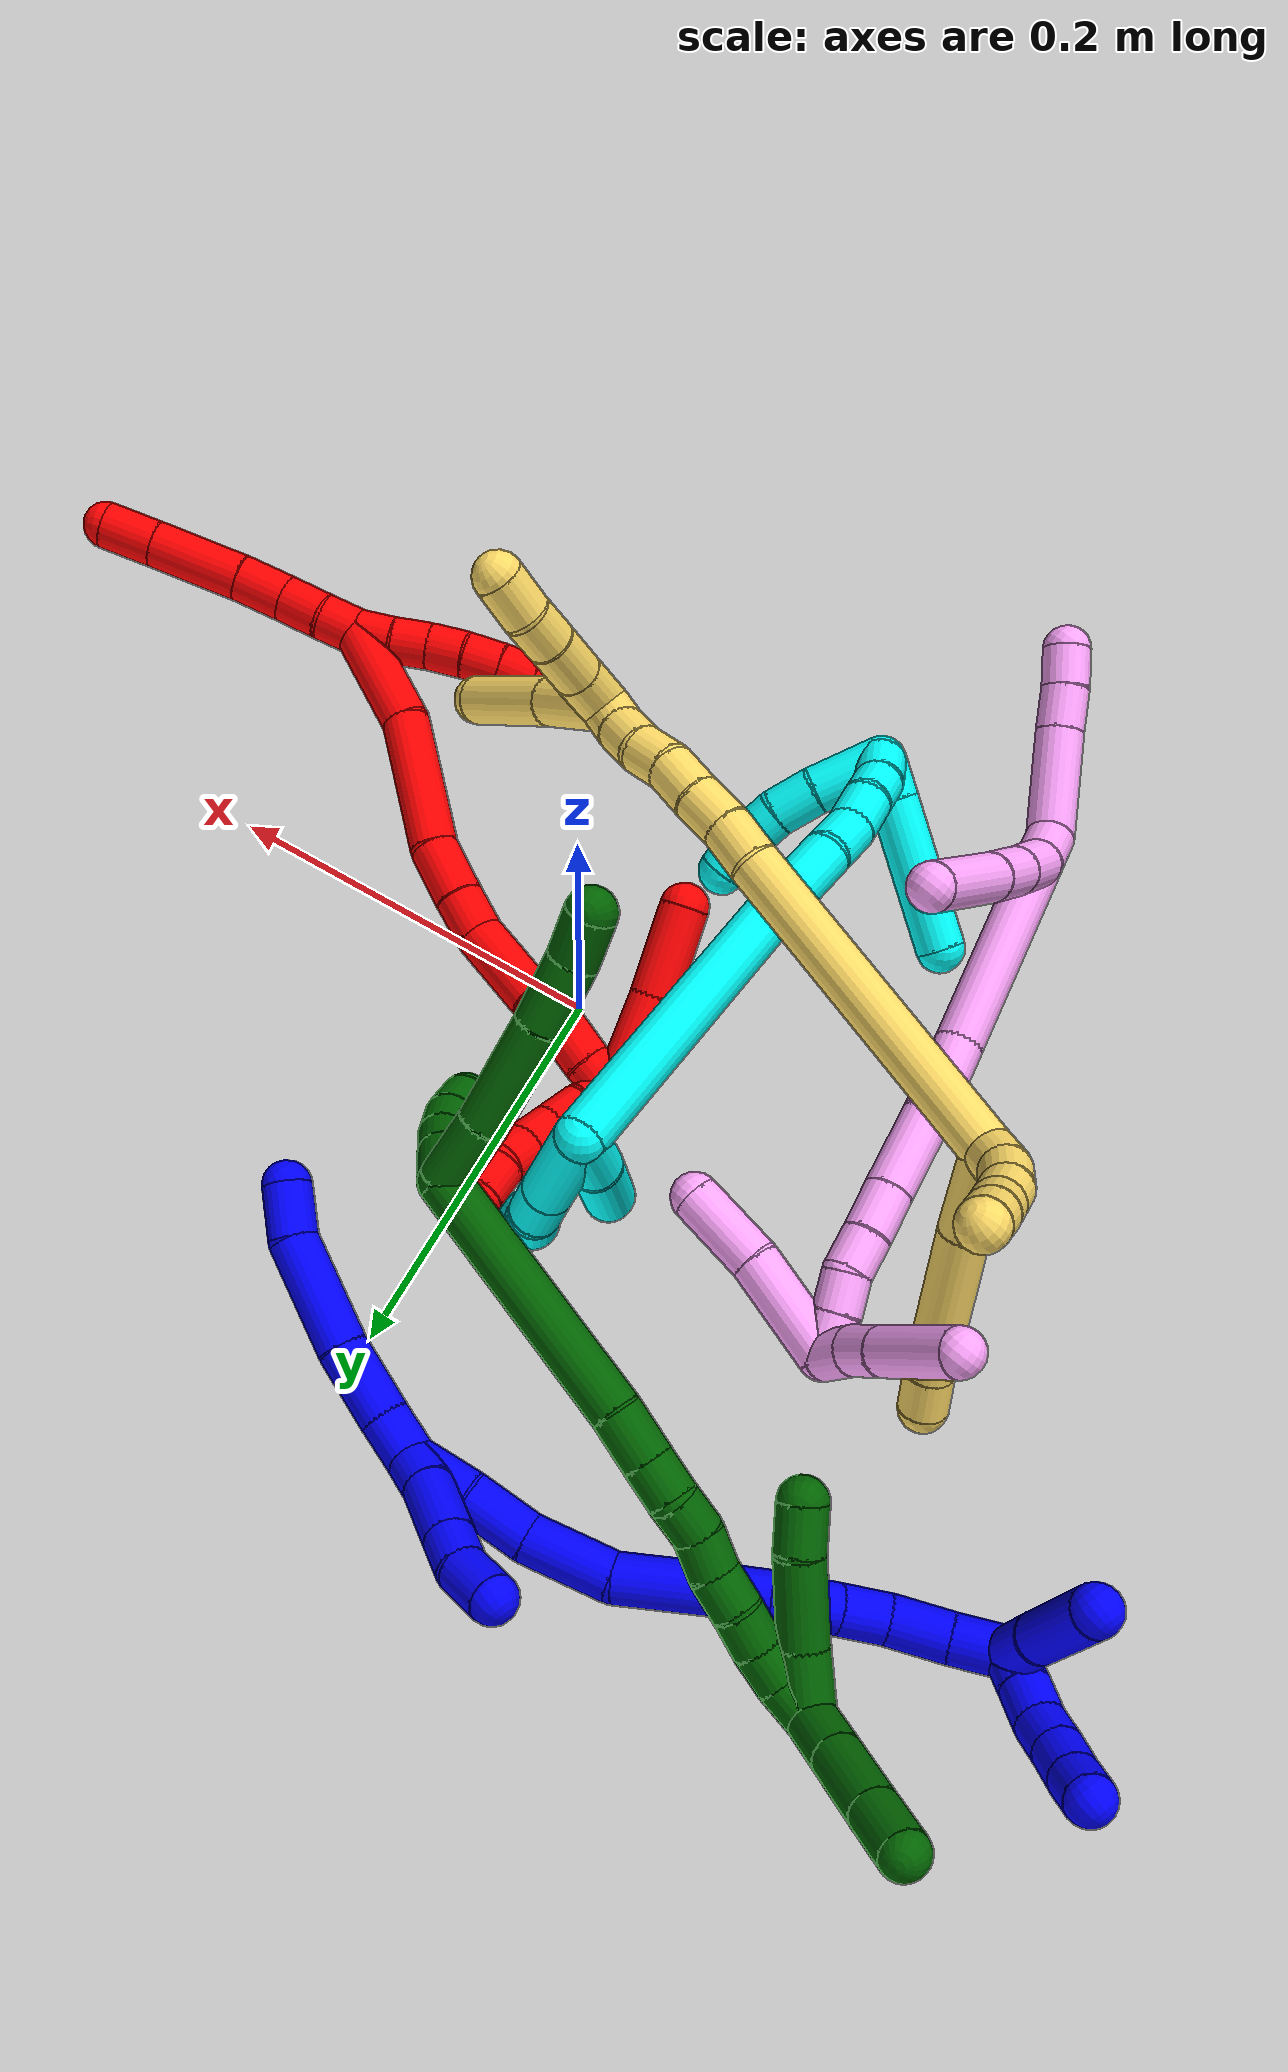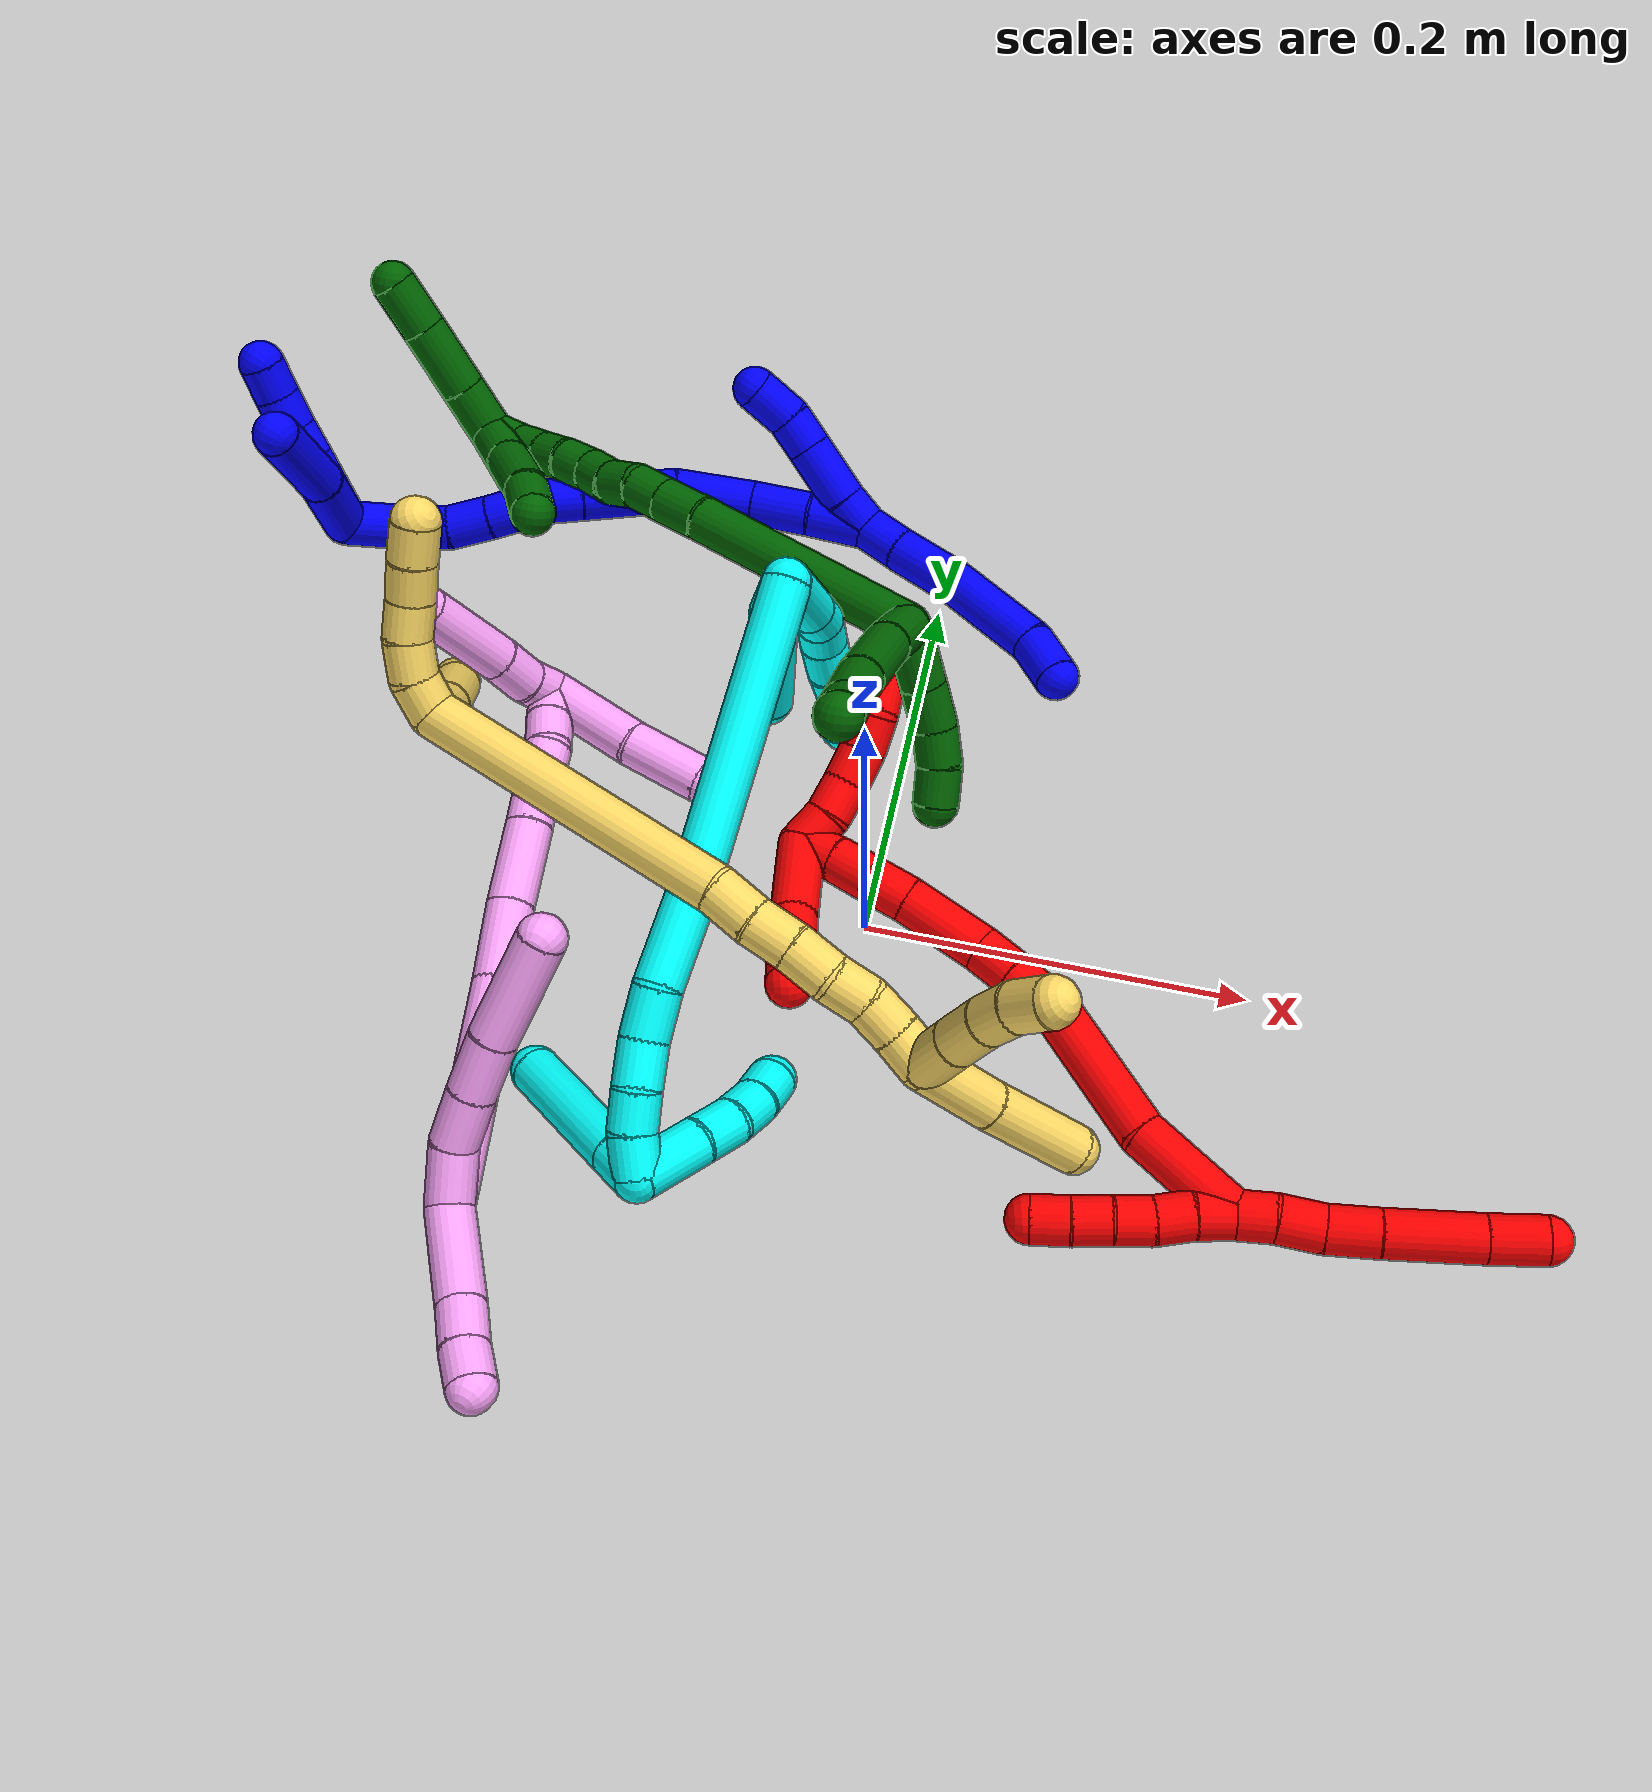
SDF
<sdf version="1.7">
 <world name="default">
  <plugin name="TubeGeneratorPlugin" filename="libtube_generator_plugin.so"/>
  <model name="photoneo_s_sensor">
   <static>1</static>
   <pose>0 0 2 1.57079 1.57079 3.14159</pose>
   <link name="link">
    <inertial><mass>0.1</mass></inertial>
    <sensor name="sensor" type="depth">
     <update_rate>30</update_rate>
     <camera>
      <horizontal_fov>1.22</horizontal_fov>
      <image><width>1920</width><height>1200</height><format>B8G8R8</format></image>
      <clip><near>0.1</near><far>4</far></clip>
      <depth_camera><output>points</output></depth_camera>
     </camera>
     <plugin name="camera_plugin" filename="libgazebo_ros_depth_camera.so">
      <baseline>0.2</baseline>
      <alwaysOn>1</alwaysOn>
      <updateRate>0.0</updateRate>
      <cameraName>camera_ir</cameraName>
      <imageTopicName>/camera/color/image_raw</imageTopicName>
      <cameraInfoTopicName>/camera/color/camera_info</cameraInfoTopicName>
      <depthImageTopicName>/camera/depth/image_raw</depthImageTopicName>
      <depthImageCameraInfoTopicName>/camera/depth/camera_info</depthImageCameraInfoTopicName>
      <pointCloudTopicName>/camera/depth/points</pointCloudTopicName>
      <frameName>fr_optical</frameName>
      <pointCloudCutoff>0.1</pointCloudCutoff>
      <pointCloudCutoffMax>2.0</pointCloudCutoffMax>
      <distortionK1>0</distortionK1>
      <distortionK2>0</distortionK2>
      <distortionK3>0</distortionK3>
      <distortionT1>0</distortionT1>
      <distortionT2>0</distortionT2>
      <CxPrime>0</CxPrime>
      <Cx>0</Cx>
      <Cy>0</Cy>
      <focalLength>0</focalLength>
      <hackBaseline>0</hackBaseline>
     </plugin>
    </sensor>
   </link>
  </model>
  <gravity>0 0 -9.8</gravity>
  <magnetic_field>6e-06 2.3e-05 -4.2e-05</magnetic_field>
  <atmosphere type="adiabatic"/>
  <physics name="default_physics" default="0" type="ode">
   <max_step_size>0.003</max_step_size>
   <real_time_factor>1</real_time_factor>
   <real_time_update_rate>1000</real_time_update_rate>
   <max_contacts>10000</max_contacts>
   <ode>
    <solver>
     <type>quick</type>
     <iters>100</iters>
     <sor>1.3</sor>
     <use_dynamic_moi_rescaling>0</use_dynamic_moi_rescaling>
    </solver>
    <constraints>
     <contact_max_correcting_vel>0</contact_max_correcting_vel>
     <contact_surface_layer>0.001</contact_surface_layer>
     <cfm>0</cfm>
     <erp>0.2</erp>
    </constraints>
   </ode>
  </physics>
  <scene><ambient>0.4 0.4 0.4 1</ambient><background>0.7 0.7 0.7 1</background><shadows>0</shadows></scene>
  <audio><device>default</device></audio>
  <spherical_coordinates>
   <surface_model>EARTH_WGS84</surface_model>
   <latitude_deg>0</latitude_deg>
   <longitude_deg>0</longitude_deg>
   <elevation>0</elevation>
   <heading_deg>0</heading_deg>
  </spherical_coordinates>
  <model name="bin">
   <static>1</static>
   <link name="bottom">
    <collision name="collision-bottom">
     <pose>0 0 -0.01 0 -0 0</pose>
     <geometry><box><size>0.8 0.6 0.02</size></box></geometry>
     <surface>
      <friction><ode><mu>100</mu><mu2>100</mu2></ode></friction>
      <contact><collide_bitmask>65535</collide_bitmask></contact>
     </surface>
    </collision>
   </link>
   <link name="west_wall">
    <collision name="collision-west_wall">
     <pose>-0.41 0 0.1 0 -0 0</pose>
     <geometry><box><size>0.02 0.6 0.2</size></box></geometry>
     <surface>
      <friction><ode><mu>100</mu><mu2>100</mu2></ode></friction>
      <contact><collide_bitmask>65535</collide_bitmask></contact>
     </surface>
    </collision>
   </link>
   <link name="east_wall">
    <collision name="collision-east_wall">
     <pose>0.41 0 0.1 0 -0 0</pose>
     <geometry><box><size>0.02 0.6 0.2</size></box></geometry>
     <surface>
      <friction><ode><mu>100</mu><mu2>100</mu2></ode></friction>
      <contact><collide_bitmask>65535</collide_bitmask></contact>
     </surface>
    </collision>
   </link>
   <link name="south_wall">
    <collision name="collision-south_wall">
     <pose>0 -0.31 0.1 0 -0 0</pose>
     <geometry><box><size>0.8 0.02 0.2</size></box></geometry>
     <surface>
      <friction><ode><mu>100</mu><mu2>100</mu2></ode></friction>
      <contact><collide_bitmask>65535</collide_bitmask></contact>
     </surface>
    </collision>
   </link>
   <link name="north_wall">
    <collision name="collision-north_wall">
     <pose>0 0.31 0.1 0 -0 0</pose>
     <geometry><box><size>0.8 0.02 0.2</size></box></geometry>
     <surface>
      <friction><ode><mu>100</mu><mu2>100</mu2></ode></friction>
      <contact><collide_bitmask>65535</collide_bitmask></contact>
     </surface>
    </collision>
   </link>
  </model>
  <model name="1">
   <static>0</static>
   <link name="1">
    <collision name="collision-cylinder-e_1_2_8">
     <pose>-0.000603 -5.9e-05 -0.012209 3.13675 -0.049349 -2.94613</pose>
     <geometry><cylinder><radius>0.0125</radius><length>0.024447</length></cylinder></geometry>
     <surface>
      <friction><ode><mu>1.16</mu><mu2>1.16</mu2><slip1>0</slip1><slip2>0</slip2></ode></friction>
      <contact><ode><kp>1e+06</kp><kd>1</kd><max_vel>0</max_vel><min_depth>0.001</min_depth></ode></contact>
     </surface>
    </collision>
    <visual name="visual-cylinder-e_1_2_8">
     <pose>-0.000603 -5.9e-05 -0.012209 3.13675 -0.049349 -2.94613</pose>
     <geometry><cylinder><radius>0.0125</radius><length>0.024447</length></cylinder></geometry>
     <material><ambient>0 0 1 1</ambient></material>
    </visual>
    <collision name="collision-cylinder-e_2_8_9">
     <pose>-0.002507 -0.002538 -0.043942 3.0183 -0.066039 -0.982697</pose>
     <geometry><cylinder><radius>0.0125</radius><length>0.039435</length></cylinder></geometry>
     <surface>
      <friction><ode><mu>1.16</mu><mu2>1.16</mu2><slip1>0</slip1><slip2>0</slip2></ode></friction>
      <contact><ode><kp>1e+06</kp><kd>1</kd><max_vel>0</max_vel><min_depth>0.001</min_depth></ode></contact>
     </surface>
    </collision>
    <visual name="visual-cylinder-e_2_8_9">
     <pose>-0.002507 -0.002538 -0.043942 3.0183 -0.066039 -0.982697</pose>
     <geometry><cylinder><radius>0.0125</radius><length>0.039435</length></cylinder></geometry>
     <material><ambient>0 0 1 1</ambient></material>
    </visual>
    <collision name="collision-cylinder-e_3_9_10">
     <pose>-0.009109 -0.008553 -0.09205 3.01647 -0.181962 -1.93819</pose>
     <geometry><cylinder><radius>0.0125</radius><length>0.058582</length></cylinder></geometry>
     <surface>
      <friction><ode><mu>1.16</mu><mu2>1.16</mu2><slip1>0</slip1><slip2>0</slip2></ode></friction>
      <contact><ode><kp>1e+06</kp><kd>1</kd><max_vel>0</max_vel><min_depth>0.001</min_depth></ode></contact>
     </surface>
    </collision>
    <visual name="visual-cylinder-e_3_9_10">
     <pose>-0.009109 -0.008553 -0.09205 3.01647 -0.181962 -1.93819</pose>
     <geometry><cylinder><radius>0.0125</radius><length>0.058582</length></cylinder></geometry>
     <material><ambient>0 0 1 1</ambient></material>
    </visual>
    <collision name="collision-cylinder-e_4_10_6">
     <pose>-0.020778 -0.014212 -0.132662 2.97164 -0.480924 -2.47291</pose>
     <geometry><cylinder><radius>0.0125</radius><length>0.027536</length></cylinder></geometry>
     <surface>
      <friction><ode><mu>1.16</mu><mu2>1.16</mu2><slip1>0</slip1><slip2>0</slip2></ode></friction>
      <contact><ode><kp>1e+06</kp><kd>1</kd><max_vel>0</max_vel><min_depth>0.001</min_depth></ode></contact>
     </surface>
    </collision>
    <visual name="visual-cylinder-e_4_10_6">
     <pose>-0.020778 -0.014212 -0.132662 2.97164 -0.480924 -2.47291</pose>
     <geometry><cylinder><radius>0.0125</radius><length>0.027536</length></cylinder></geometry>
     <material><ambient>0 0 1 1</ambient></material>
    </visual>
    <collision name="collision-cylinder-e_1_2_11">
     <pose>0.001114 -0.005154 0.008678 0.535989 0.10989 0.030204</pose>
     <geometry><cylinder><radius>0.0125</radius><length>0.020309</length></cylinder></geometry>
     <surface>
      <friction><ode><mu>1.16</mu><mu2>1.16</mu2><slip1>0</slip1><slip2>0</slip2></ode></friction>
      <contact><ode><kp>1e+06</kp><kd>1</kd><max_vel>0</max_vel><min_depth>0.001</min_depth></ode></contact>
     </surface>
    </collision>
    <visual name="visual-cylinder-e_1_2_11">
     <pose>0.001114 -0.005154 0.008678 0.535989 0.10989 0.030204</pose>
     <geometry><cylinder><radius>0.0125</radius><length>0.020309</length></cylinder></geometry>
     <material><ambient>0 0 1 1</ambient></material>
    </visual>
    <collision name="collision-cylinder-e_2_11_12">
     <pose>0.006074 -0.018916 0.031913 0.533964 0.22365 0.061408</pose>
     <geometry><cylinder><radius>0.0125</radius><length>0.034688</length></cylinder></geometry>
     <surface>
      <friction><ode><mu>1.16</mu><mu2>1.16</mu2><slip1>0</slip1><slip2>0</slip2></ode></friction>
      <contact><ode><kp>1e+06</kp><kd>1</kd><max_vel>0</max_vel><min_depth>0.001</min_depth></ode></contact>
     </surface>
    </collision>
    <visual name="visual-cylinder-e_2_11_12">
     <pose>0.006074 -0.018916 0.031913 0.533964 0.22365 0.061408</pose>
     <geometry><cylinder><radius>0.0125</radius><length>0.034688</length></cylinder></geometry>
     <material><ambient>0 0 1 1</ambient></material>
    </visual>
    <collision name="collision-cylinder-e_3_12_13">
     <pose>0.012109 -0.032504 0.054896 0.533913 0.219929 0.060372</pose>
     <geometry><cylinder><radius>0.0125</radius><length>0.020058</length></cylinder></geometry>
     <surface>
      <friction><ode><mu>1.16</mu><mu2>1.16</mu2><slip1>0</slip1><slip2>0</slip2></ode></friction>
      <contact><ode><kp>1e+06</kp><kd>1</kd><max_vel>0</max_vel><min_depth>0.001</min_depth></ode></contact>
     </surface>
    </collision>
    <visual name="visual-cylinder-e_3_12_13">
     <pose>0.012109 -0.032504 0.054896 0.533913 0.219929 0.060372</pose>
     <geometry><cylinder><radius>0.0125</radius><length>0.020058</length></cylinder></geometry>
     <material><ambient>0 0 1 1</ambient></material>
    </visual>
    <collision name="collision-cylinder-e_4_13_5">
     <pose>0.013193 -0.043976 0.073915 0.549731 -0.08856 -0.024989</pose>
     <geometry><cylinder><radius>0.0125</radius><length>0.024946</length></cylinder></geometry>
     <surface>
      <friction><ode><mu>1.16</mu><mu2>1.16</mu2><slip1>0</slip1><slip2>0</slip2></ode></friction>
      <contact><ode><kp>1e+06</kp><kd>1</kd><max_vel>0</max_vel><min_depth>0.001</min_depth></ode></contact>
     </surface>
    </collision>
    <visual name="visual-cylinder-e_4_13_5">
     <pose>0.013193 -0.043976 0.073915 0.549731 -0.08856 -0.024989</pose>
     <geometry><cylinder><radius>0.0125</radius><length>0.024946</length></cylinder></geometry>
     <material><ambient>0 0 1 1</ambient></material>
    </visual>
    <collision name="collision-cylinder-e_1_2_14">
     <pose>-0.005904 -0.000468 0.01517 0.030828 -0.370967 -0.005785</pose>
     <geometry><cylinder><radius>0.0125</radius><length>0.032571</length></cylinder></geometry>
     <surface>
      <friction><ode><mu>1.16</mu><mu2>1.16</mu2><slip1>0</slip1><slip2>0</slip2></ode></friction>
      <contact><ode><kp>1e+06</kp><kd>1</kd><max_vel>0</max_vel><min_depth>0.001</min_depth></ode></contact>
     </surface>
    </collision>
    <visual name="visual-cylinder-e_1_2_14">
     <pose>-0.005904 -0.000468 0.01517 0.030828 -0.370967 -0.005785</pose>
     <geometry><cylinder><radius>0.0125</radius><length>0.032571</length></cylinder></geometry>
     <material><ambient>0 0 1 1</ambient></material>
    </visual>
    <collision name="collision-cylinder-e_2_14_15">
     <pose>-0.017346 0.000628 0.046356 -0.097348 -0.331502 0.016297</pose>
     <geometry><cylinder><radius>0.0125</radius><length>0.034036</length></cylinder></geometry>
     <surface>
      <friction><ode><mu>1.16</mu><mu2>1.16</mu2><slip1>0</slip1><slip2>0</slip2></ode></friction>
      <contact><ode><kp>1e+06</kp><kd>1</kd><max_vel>0</max_vel><min_depth>0.001</min_depth></ode></contact>
     </surface>
    </collision>
    <visual name="visual-cylinder-e_2_14_15">
     <pose>-0.017346 0.000628 0.046356 -0.097348 -0.331502 0.016297</pose>
     <geometry><cylinder><radius>0.0125</radius><length>0.034036</length></cylinder></geometry>
     <material><ambient>0 0 1 1</ambient></material>
    </visual>
    <collision name="collision-cylinder-e_3_15_16">
     <pose>-0.033292 0.000191 0.082086 0.101147 -0.483578 -0.024964</pose>
     <geometry><cylinder><radius>0.0125</radius><length>0.044764</length></cylinder></geometry>
     <surface>
      <friction><ode><mu>1.16</mu><mu2>1.16</mu2><slip1>0</slip1><slip2>0</slip2></ode></friction>
      <contact><ode><kp>1e+06</kp><kd>1</kd><max_vel>0</max_vel><min_depth>0.001</min_depth></ode></contact>
     </surface>
    </collision>
    <visual name="visual-cylinder-e_3_15_16">
     <pose>-0.033292 0.000191 0.082086 0.101147 -0.483578 -0.024964</pose>
     <geometry><cylinder><radius>0.0125</radius><length>0.044764</length></cylinder></geometry>
     <material><ambient>0 0 1 1</ambient></material>
    </visual>
    <collision name="collision-cylinder-e_4_16_17">
     <pose>-0.062824 -0.005114 0.120347 0.176335 -0.79293 -0.073978</pose>
     <geometry><cylinder><radius>0.0125</radius><length>0.053692</length></cylinder></geometry>
     <surface>
      <friction><ode><mu>1.16</mu><mu2>1.16</mu2><slip1>0</slip1><slip2>0</slip2></ode></friction>
      <contact><ode><kp>1e+06</kp><kd>1</kd><max_vel>0</max_vel><min_depth>0.001</min_depth></ode></contact>
     </surface>
    </collision>
    <visual name="visual-cylinder-e_4_16_17">
     <pose>-0.062824 -0.005114 0.120347 0.176335 -0.79293 -0.073978</pose>
     <geometry><cylinder><radius>0.0125</radius><length>0.053692</length></cylinder></geometry>
     <material><ambient>0 0 1 1</ambient></material>
    </visual>
    <collision name="collision-cylinder-e_5_17_18">
     <pose>-0.089278 -0.009493 0.14625 0.144993 -0.778344 -0.059546</pose>
     <geometry><cylinder><radius>0.0125</radius><length>0.020877</length></cylinder></geometry>
     <surface>
      <friction><ode><mu>1.16</mu><mu2>1.16</mu2><slip1>0</slip1><slip2>0</slip2></ode></friction>
      <contact><ode><kp>1e+06</kp><kd>1</kd><max_vel>0</max_vel><min_depth>0.001</min_depth></ode></contact>
     </surface>
    </collision>
    <visual name="visual-cylinder-e_5_17_18">
     <pose>-0.089278 -0.009493 0.14625 0.144993 -0.778344 -0.059546</pose>
     <geometry><cylinder><radius>0.0125</radius><length>0.020877</length></cylinder></geometry>
     <material><ambient>0 0 1 1</ambient></material>
    </visual>
    <collision name="collision-cylinder-e_6_18_19">
     <pose>-0.107775 -0.006874 0.16434 -0.331319 -0.77719 0.136688</pose>
     <geometry><cylinder><radius>0.0125</radius><length>0.031851</length></cylinder></geometry>
     <surface>
      <friction><ode><mu>1.16</mu><mu2>1.16</mu2><slip1>0</slip1><slip2>0</slip2></ode></friction>
      <contact><ode><kp>1e+06</kp><kd>1</kd><max_vel>0</max_vel><min_depth>0.001</min_depth></ode></contact>
     </surface>
    </collision>
    <visual name="visual-cylinder-e_6_18_19">
     <pose>-0.107775 -0.006874 0.16434 -0.331319 -0.77719 0.136688</pose>
     <geometry><cylinder><radius>0.0125</radius><length>0.031851</length></cylinder></geometry>
     <material><ambient>0 0 1 1</ambient></material>
    </visual>
    <collision name="collision-cylinder-e_7_19_20">
     <pose>-0.127422 -0.000816 0.183646 -0.269287 -0.761747 0.10838</pose>
     <geometry><cylinder><radius>0.0125</radius><length>0.024571</length></cylinder></geometry>
     <surface>
      <friction><ode><mu>1.16</mu><mu2>1.16</mu2><slip1>0</slip1><slip2>0</slip2></ode></friction>
      <contact><ode><kp>1e+06</kp><kd>1</kd><max_vel>0</max_vel><min_depth>0.001</min_depth></ode></contact>
     </surface>
    </collision>
    <visual name="visual-cylinder-e_7_19_20">
     <pose>-0.127422 -0.000816 0.183646 -0.269287 -0.761747 0.10838</pose>
     <geometry><cylinder><radius>0.0125</radius><length>0.024571</length></cylinder></geometry>
     <material><ambient>0 0 1 1</ambient></material>
    </visual>
    <collision name="collision-cylinder-e_8_20_21">
     <pose>-0.14491 0.00039 0.204557 0.093671 -0.628452 -0.030462</pose>
     <geometry><cylinder><radius>0.0125</radius><length>0.030648</length></cylinder></geometry>
     <surface>
      <friction><ode><mu>1.16</mu><mu2>1.16</mu2><slip1>0</slip1><slip2>0</slip2></ode></friction>
      <contact><ode><kp>1e+06</kp><kd>1</kd><max_vel>0</max_vel><min_depth>0.001</min_depth></ode></contact>
     </surface>
    </collision>
    <visual name="visual-cylinder-e_8_20_21">
     <pose>-0.14491 0.00039 0.204557 0.093671 -0.628452 -0.030462</pose>
     <geometry><cylinder><radius>0.0125</radius><length>0.030648</length></cylinder></geometry>
     <material><ambient>0 0 1 1</ambient></material>
    </visual>
    <collision name="collision-cylinder-e_9_21_1">
     <pose>-0.161946 -0.003341 0.227439 0.239263 -0.637013 -0.07923</pose>
     <geometry><cylinder><radius>0.0125</radius><length>0.02699</length></cylinder></geometry>
     <surface>
      <friction><ode><mu>1.16</mu><mu2>1.16</mu2><slip1>0</slip1><slip2>0</slip2></ode></friction>
      <contact><ode><kp>1e+06</kp><kd>1</kd><max_vel>0</max_vel><min_depth>0.001</min_depth></ode></contact>
     </surface>
    </collision>
    <visual name="visual-cylinder-e_9_21_1">
     <pose>-0.161946 -0.003341 0.227439 0.239263 -0.637013 -0.07923</pose>
     <geometry><cylinder><radius>0.0125</radius><length>0.02699</length></cylinder></geometry>
     <material><ambient>0 0 1 1</ambient></material>
    </visual>
    <collision name="collision-cylinder-e_1_1_22">
     <pose>-0.172299 -0.027846 0.239983 1.47965 -0.105193 -0.096032</pose>
     <geometry><cylinder><radius>0.0125</radius><length>0.044297</length></cylinder></geometry>
     <surface>
      <friction><ode><mu>1.16</mu><mu2>1.16</mu2><slip1>0</slip1><slip2>0</slip2></ode></friction>
      <contact><ode><kp>1e+06</kp><kd>1</kd><max_vel>0</max_vel><min_depth>0.001</min_depth></ode></contact>
     </surface>
    </collision>
    <visual name="visual-cylinder-e_1_1_22">
     <pose>-0.172299 -0.027846 0.239983 1.47965 -0.105193 -0.096032</pose>
     <geometry><cylinder><radius>0.0125</radius><length>0.044297</length></cylinder></geometry>
     <material><ambient>0 0 1 1</ambient></material>
    </visual>
    <collision name="collision-cylinder-e_2_22_4">
     <pose>-0.180827 -0.076702 0.245519 1.44039 -0.224601 -0.197258</pose>
     <geometry><cylinder><radius>0.0125</radius><length>0.055703</length></cylinder></geometry>
     <surface>
      <friction><ode><mu>1.16</mu><mu2>1.16</mu2><slip1>0</slip1><slip2>0</slip2></ode></friction>
      <contact><ode><kp>1e+06</kp><kd>1</kd><max_vel>0</max_vel><min_depth>0.001</min_depth></ode></contact>
     </surface>
    </collision>
    <visual name="visual-cylinder-e_2_22_4">
     <pose>-0.180827 -0.076702 0.245519 1.44039 -0.224601 -0.197258</pose>
     <geometry><cylinder><radius>0.0125</radius><length>0.055703</length></cylinder></geometry>
     <material><ambient>0 0 1 1</ambient></material>
    </visual>
    <collision name="collision-cylinder-e_1_1_23">
     <pose>-0.166672 -0.010874 0.246008 0.553555 0.336448 0.096411</pose>
     <geometry><cylinder><radius>0.0125</radius><length>0.02</length></cylinder></geometry>
     <surface>
      <friction><ode><mu>1.16</mu><mu2>1.16</mu2><slip1>0</slip1><slip2>0</slip2></ode></friction>
      <contact><ode><kp>1e+06</kp><kd>1</kd><max_vel>0</max_vel><min_depth>0.001</min_depth></ode></contact>
     </surface>
    </collision>
    <visual name="visual-cylinder-e_1_1_23">
     <pose>-0.166672 -0.010874 0.246008 0.553555 0.336448 0.096411</pose>
     <geometry><cylinder><radius>0.0125</radius><length>0.02</length></cylinder></geometry>
     <material><ambient>0 0 1 1</ambient></material>
    </visual>
    <collision name="collision-cylinder-e_2_23_24">
     <pose>-0.159939 -0.020411 0.262241 0.508676 0.350281 0.09194</pose>
     <geometry><cylinder><radius>0.0125</radius><length>0.02</length></cylinder></geometry>
     <surface>
      <friction><ode><mu>1.16</mu><mu2>1.16</mu2><slip1>0</slip1><slip2>0</slip2></ode></friction>
      <contact><ode><kp>1e+06</kp><kd>1</kd><max_vel>0</max_vel><min_depth>0.001</min_depth></ode></contact>
     </surface>
    </collision>
    <visual name="visual-cylinder-e_2_23_24">
     <pose>-0.159939 -0.020411 0.262241 0.508676 0.350281 0.09194</pose>
     <geometry><cylinder><radius>0.0125</radius><length>0.02</length></cylinder></geometry>
     <material><ambient>0 0 1 1</ambient></material>
    </visual>
    <collision name="collision-cylinder-e_3_24_25">
     <pose>-0.154234 -0.031975 0.277225 0.800557 0.229314 0.097378</pose>
     <geometry><cylinder><radius>0.0125</radius><length>0.02</length></cylinder></geometry>
     <surface>
      <friction><ode><mu>1.16</mu><mu2>1.16</mu2><slip1>0</slip1><slip2>0</slip2></ode></friction>
      <contact><ode><kp>1e+06</kp><kd>1</kd><max_vel>0</max_vel><min_depth>0.001</min_depth></ode></contact>
     </surface>
    </collision>
    <visual name="visual-cylinder-e_3_24_25">
     <pose>-0.154234 -0.031975 0.277225 0.800557 0.229314 0.097378</pose>
     <geometry><cylinder><radius>0.0125</radius><length>0.02</length></cylinder></geometry>
     <material><ambient>0 0 1 1</ambient></material>
    </visual>
    <collision name="collision-cylinder-e_4_25_26">
     <pose>-0.149319 -0.046146 0.290444 0.8399 0.267325 0.119936</pose>
     <geometry><cylinder><radius>0.0125</radius><length>0.02</length></cylinder></geometry>
     <surface>
      <friction><ode><mu>1.16</mu><mu2>1.16</mu2><slip1>0</slip1><slip2>0</slip2></ode></friction>
      <contact><ode><kp>1e+06</kp><kd>1</kd><max_vel>0</max_vel><min_depth>0.001</min_depth></ode></contact>
     </surface>
    </collision>
    <visual name="visual-cylinder-e_4_25_26">
     <pose>-0.149319 -0.046146 0.290444 0.8399 0.267325 0.119936</pose>
     <geometry><cylinder><radius>0.0125</radius><length>0.02</length></cylinder></geometry>
     <material><ambient>0 0 1 1</ambient></material>
    </visual>
    <collision name="collision-cylinder-e_5_26_3">
     <pose>-0.144455 -0.061402 0.302347 0.975894 0.224149 0.119327</pose>
     <geometry><cylinder><radius>0.0125</radius><length>0.02</length></cylinder></geometry>
     <surface>
      <friction><ode><mu>1.16</mu><mu2>1.16</mu2><slip1>0</slip1><slip2>0</slip2></ode></friction>
      <contact><ode><kp>1e+06</kp><kd>1</kd><max_vel>0</max_vel><min_depth>0.001</min_depth></ode></contact>
     </surface>
    </collision>
    <visual name="visual-cylinder-e_5_26_3">
     <pose>-0.144455 -0.061402 0.302347 0.975894 0.224149 0.119327</pose>
     <geometry><cylinder><radius>0.0125</radius><length>0.02</length></cylinder></geometry>
     <material><ambient>0 0 1 1</ambient></material>
    </visual>
    <collision name="collision-sphere-3">
     <pose>-0.142232 -0.069477 0.307811 0 -0 0</pose>
     <geometry><sphere><radius>0.0125</radius></sphere></geometry>
     <surface>
      <friction><ode><mu>1.16</mu><mu2>1.16</mu2><slip1>0</slip1><slip2>0</slip2></ode></friction>
      <contact><ode><kp>1e+06</kp><kd>1</kd><max_vel>0</max_vel><min_depth>0.001</min_depth></ode></contact>
     </surface>
    </collision>
    <visual name="visual-sphere-3">
     <pose>-0.142232 -0.069477 0.307811 0 -0 0</pose>
     <geometry><sphere><radius>0.0125</radius></sphere></geometry>
     <material><ambient>0 0 1 1</ambient></material>
    </visual>
    <collision name="collision-sphere-26">
     <pose>-0.146678 -0.053327 0.296883 0 -0 0</pose>
     <geometry><sphere><radius>0.0125</radius></sphere></geometry>
     <surface>
      <friction><ode><mu>1.16</mu><mu2>1.16</mu2><slip1>0</slip1><slip2>0</slip2></ode></friction>
      <contact><ode><kp>1e+06</kp><kd>1</kd><max_vel>0</max_vel><min_depth>0.001</min_depth></ode></contact>
     </surface>
    </collision>
    <visual name="visual-sphere-26">
     <pose>-0.146678 -0.053327 0.296883 0 -0 0</pose>
     <geometry><sphere><radius>0.0125</radius></sphere></geometry>
     <material><ambient>0 0 1 1</ambient></material>
    </visual>
    <collision name="collision-sphere-25">
     <pose>-0.151961 -0.038964 0.284006 0 -0 0</pose>
     <geometry><sphere><radius>0.0125</radius></sphere></geometry>
     <surface>
      <friction><ode><mu>1.16</mu><mu2>1.16</mu2><slip1>0</slip1><slip2>0</slip2></ode></friction>
      <contact><ode><kp>1e+06</kp><kd>1</kd><max_vel>0</max_vel><min_depth>0.001</min_depth></ode></contact>
     </surface>
    </collision>
    <visual name="visual-sphere-25">
     <pose>-0.151961 -0.038964 0.284006 0 -0 0</pose>
     <geometry><sphere><radius>0.0125</radius></sphere></geometry>
     <material><ambient>0 0 1 1</ambient></material>
    </visual>
    <collision name="collision-sphere-24">
     <pose>-0.156507 -0.024985 0.270444 0 -0 0</pose>
     <geometry><sphere><radius>0.0125</radius></sphere></geometry>
     <surface>
      <friction><ode><mu>1.16</mu><mu2>1.16</mu2><slip1>0</slip1><slip2>0</slip2></ode></friction>
      <contact><ode><kp>1e+06</kp><kd>1</kd><max_vel>0</max_vel><min_depth>0.001</min_depth></ode></contact>
     </surface>
    </collision>
    <visual name="visual-sphere-24">
     <pose>-0.156507 -0.024985 0.270444 0 -0 0</pose>
     <geometry><sphere><radius>0.0125</radius></sphere></geometry>
     <material><ambient>0 0 1 1</ambient></material>
    </visual>
    <collision name="collision-sphere-23">
     <pose>-0.16337 -0.015836 0.254037 0 -0 0</pose>
     <geometry><sphere><radius>0.0125</radius></sphere></geometry>
     <surface>
      <friction><ode><mu>1.16</mu><mu2>1.16</mu2><slip1>0</slip1><slip2>0</slip2></ode></friction>
      <contact><ode><kp>1e+06</kp><kd>1</kd><max_vel>0</max_vel><min_depth>0.001</min_depth></ode></contact>
     </surface>
    </collision>
    <visual name="visual-sphere-23">
     <pose>-0.16337 -0.015836 0.254037 0 -0 0</pose>
     <geometry><sphere><radius>0.0125</radius></sphere></geometry>
     <material><ambient>0 0 1 1</ambient></material>
    </visual>
    <collision name="collision-sphere-4">
     <pose>-0.18703 -0.103624 0.249049 0 -0 0</pose>
     <geometry><sphere><radius>0.0125</radius></sphere></geometry>
     <surface>
      <friction><ode><mu>1.16</mu><mu2>1.16</mu2><slip1>0</slip1><slip2>0</slip2></ode></friction>
      <contact><ode><kp>1e+06</kp><kd>1</kd><max_vel>0</max_vel><min_depth>0.001</min_depth></ode></contact>
     </surface>
    </collision>
    <visual name="visual-sphere-4">
     <pose>-0.18703 -0.103624 0.249049 0 -0 0</pose>
     <geometry><sphere><radius>0.0125</radius></sphere></geometry>
     <material><ambient>0 0 1 1</ambient></material>
    </visual>
    <collision name="collision-sphere-22">
     <pose>-0.174624 -0.049781 0.241988 0 -0 0</pose>
     <geometry><sphere><radius>0.0125</radius></sphere></geometry>
     <surface>
      <friction><ode><mu>1.16</mu><mu2>1.16</mu2><slip1>0</slip1><slip2>0</slip2></ode></friction>
      <contact><ode><kp>1e+06</kp><kd>1</kd><max_vel>0</max_vel><min_depth>0.001</min_depth></ode></contact>
     </surface>
    </collision>
    <visual name="visual-sphere-22">
     <pose>-0.174624 -0.049781 0.241988 0 -0 0</pose>
     <geometry><sphere><radius>0.0125</radius></sphere></geometry>
     <material><ambient>0 0 1 1</ambient></material>
    </visual>
    <collision name="collision-sphere-1">
     <pose>-0.169973 -0.005911 0.237978 0 -0 0</pose>
     <geometry><sphere><radius>0.0125</radius></sphere></geometry>
     <surface>
      <friction><ode><mu>1.16</mu><mu2>1.16</mu2><slip1>0</slip1><slip2>0</slip2></ode></friction>
      <contact><ode><kp>1e+06</kp><kd>1</kd><max_vel>0</max_vel><min_depth>0.001</min_depth></ode></contact>
     </surface>
    </collision>
    <visual name="visual-sphere-1">
     <pose>-0.169973 -0.005911 0.237978 0 -0 0</pose>
     <geometry><sphere><radius>0.0125</radius></sphere></geometry>
     <material><ambient>0 0 1 1</ambient></material>
    </visual>
    <collision name="collision-sphere-21">
     <pose>-0.153919 -0.00077 0.216899 0 -0 0</pose>
     <geometry><sphere><radius>0.0125</radius></sphere></geometry>
     <surface>
      <friction><ode><mu>1.16</mu><mu2>1.16</mu2><slip1>0</slip1><slip2>0</slip2></ode></friction>
      <contact><ode><kp>1e+06</kp><kd>1</kd><max_vel>0</max_vel><min_depth>0.001</min_depth></ode></contact>
     </surface>
    </collision>
    <visual name="visual-sphere-21">
     <pose>-0.153919 -0.00077 0.216899 0 -0 0</pose>
     <geometry><sphere><radius>0.0125</radius></sphere></geometry>
     <material><ambient>0 0 1 1</ambient></material>
    </visual>
    <collision name="collision-sphere-11">
     <pose>0.002227 -0.010309 0.017355 0 -0 0</pose>
     <geometry><sphere><radius>0.0125</radius></sphere></geometry>
     <surface>
      <friction><ode><mu>1.16</mu><mu2>1.16</mu2><slip1>0</slip1><slip2>0</slip2></ode></friction>
      <contact><ode><kp>1e+06</kp><kd>1</kd><max_vel>0</max_vel><min_depth>0.001</min_depth></ode></contact>
     </surface>
    </collision>
    <visual name="visual-sphere-11">
     <pose>0.002227 -0.010309 0.017355 0 -0 0</pose>
     <geometry><sphere><radius>0.0125</radius></sphere></geometry>
     <material><ambient>0 0 1 1</ambient></material>
    </visual>
    <collision name="collision-sphere-6">
     <pose>-0.027147 -0.016277 -0.144693 0 -0 0</pose>
     <geometry><sphere><radius>0.0125</radius></sphere></geometry>
     <surface>
      <friction><ode><mu>1.16</mu><mu2>1.16</mu2><slip1>0</slip1><slip2>0</slip2></ode></friction>
      <contact><ode><kp>1e+06</kp><kd>1</kd><max_vel>0</max_vel><min_depth>0.001</min_depth></ode></contact>
     </surface>
    </collision>
    <visual name="visual-sphere-6">
     <pose>-0.027147 -0.016277 -0.144693 0 -0 0</pose>
     <geometry><sphere><radius>0.0125</radius></sphere></geometry>
     <material><ambient>0 0 1 1</ambient></material>
    </visual>
    <collision name="collision-sphere-10">
     <pose>-0.014409 -0.012148 -0.120632 0 -0 0</pose>
     <geometry><sphere><radius>0.0125</radius></sphere></geometry>
     <surface>
      <friction><ode><mu>1.16</mu><mu2>1.16</mu2><slip1>0</slip1><slip2>0</slip2></ode></friction>
      <contact><ode><kp>1e+06</kp><kd>1</kd><max_vel>0</max_vel><min_depth>0.001</min_depth></ode></contact>
     </surface>
    </collision>
    <visual name="visual-sphere-10">
     <pose>-0.014409 -0.012148 -0.120632 0 -0 0</pose>
     <geometry><sphere><radius>0.0125</radius></sphere></geometry>
     <material><ambient>0 0 1 1</ambient></material>
    </visual>
    <collision name="collision-sphere-9">
     <pose>-0.003808 -0.004958 -0.063468 0 -0 0</pose>
     <geometry><sphere><radius>0.0125</radius></sphere></geometry>
     <surface>
      <friction><ode><mu>1.16</mu><mu2>1.16</mu2><slip1>0</slip1><slip2>0</slip2></ode></friction>
      <contact><ode><kp>1e+06</kp><kd>1</kd><max_vel>0</max_vel><min_depth>0.001</min_depth></ode></contact>
     </surface>
    </collision>
    <visual name="visual-sphere-9">
     <pose>-0.003808 -0.004958 -0.063468 0 -0 0</pose>
     <geometry><sphere><radius>0.0125</radius></sphere></geometry>
     <material><ambient>0 0 1 1</ambient></material>
    </visual>
    <collision name="collision-sphere-2">
     <geometry><sphere><radius>0.0125</radius></sphere></geometry>
     <surface>
      <friction><ode><mu>1.16</mu><mu2>1.16</mu2><slip1>0</slip1><slip2>0</slip2></ode></friction>
      <contact><ode><kp>1e+06</kp><kd>1</kd><max_vel>0</max_vel><min_depth>0.001</min_depth></ode></contact>
     </surface>
    </collision>
    <visual name="visual-sphere-2">
     <geometry><sphere><radius>0.0125</radius></sphere></geometry>
     <material><ambient>0 0 1 1</ambient></material>
    </visual>
    <collision name="collision-sphere-19">
     <pose>-0.118943 -0.003181 0.175076 0 -0 0</pose>
     <geometry><sphere><radius>0.0125</radius></sphere></geometry>
     <surface>
      <friction><ode><mu>1.16</mu><mu2>1.16</mu2><slip1>0</slip1><slip2>0</slip2></ode></friction>
      <contact><ode><kp>1e+06</kp><kd>1</kd><max_vel>0</max_vel><min_depth>0.001</min_depth></ode></contact>
     </surface>
    </collision>
    <visual name="visual-sphere-19">
     <pose>-0.118943 -0.003181 0.175076 0 -0 0</pose>
     <geometry><sphere><radius>0.0125</radius></sphere></geometry>
     <material><ambient>0 0 1 1</ambient></material>
    </visual>
    <collision name="collision-sphere-8">
     <pose>-0.001206 -0.000118 -0.024417 0 -0 0</pose>
     <geometry><sphere><radius>0.0125</radius></sphere></geometry>
     <surface>
      <friction><ode><mu>1.16</mu><mu2>1.16</mu2><slip1>0</slip1><slip2>0</slip2></ode></friction>
      <contact><ode><kp>1e+06</kp><kd>1</kd><max_vel>0</max_vel><min_depth>0.001</min_depth></ode></contact>
     </surface>
    </collision>
    <visual name="visual-sphere-8">
     <pose>-0.001206 -0.000118 -0.024417 0 -0 0</pose>
     <geometry><sphere><radius>0.0125</radius></sphere></geometry>
     <material><ambient>0 0 1 1</ambient></material>
    </visual>
    <collision name="collision-sphere-12">
     <pose>0.009921 -0.027523 0.046471 0 -0 0</pose>
     <geometry><sphere><radius>0.0125</radius></sphere></geometry>
     <surface>
      <friction><ode><mu>1.16</mu><mu2>1.16</mu2><slip1>0</slip1><slip2>0</slip2></ode></friction>
      <contact><ode><kp>1e+06</kp><kd>1</kd><max_vel>0</max_vel><min_depth>0.001</min_depth></ode></contact>
     </surface>
    </collision>
    <visual name="visual-sphere-12">
     <pose>0.009921 -0.027523 0.046471 0 -0 0</pose>
     <geometry><sphere><radius>0.0125</radius></sphere></geometry>
     <material><ambient>0 0 1 1</ambient></material>
    </visual>
    <collision name="collision-sphere-13">
     <pose>0.014296 -0.037485 0.063321 0 -0 0</pose>
     <geometry><sphere><radius>0.0125</radius></sphere></geometry>
     <surface>
      <friction><ode><mu>1.16</mu><mu2>1.16</mu2><slip1>0</slip1><slip2>0</slip2></ode></friction>
      <contact><ode><kp>1e+06</kp><kd>1</kd><max_vel>0</max_vel><min_depth>0.001</min_depth></ode></contact>
     </surface>
    </collision>
    <visual name="visual-sphere-13">
     <pose>0.014296 -0.037485 0.063321 0 -0 0</pose>
     <geometry><sphere><radius>0.0125</radius></sphere></geometry>
     <material><ambient>0 0 1 1</ambient></material>
    </visual>
    <collision name="collision-sphere-5">
     <pose>0.01209 -0.050467 0.084508 0 -0 0</pose>
     <geometry><sphere><radius>0.0125</radius></sphere></geometry>
     <surface>
      <friction><ode><mu>1.16</mu><mu2>1.16</mu2><slip1>0</slip1><slip2>0</slip2></ode></friction>
      <contact><ode><kp>1e+06</kp><kd>1</kd><max_vel>0</max_vel><min_depth>0.001</min_depth></ode></contact>
     </surface>
    </collision>
    <visual name="visual-sphere-5">
     <pose>0.01209 -0.050467 0.084508 0 -0 0</pose>
     <geometry><sphere><radius>0.0125</radius></sphere></geometry>
     <material><ambient>0 0 1 1</ambient></material>
    </visual>
    <collision name="collision-sphere-14">
     <pose>-0.011808 -0.000936 0.030341 0 -0 0</pose>
     <geometry><sphere><radius>0.0125</radius></sphere></geometry>
     <surface>
      <friction><ode><mu>1.16</mu><mu2>1.16</mu2><slip1>0</slip1><slip2>0</slip2></ode></friction>
      <contact><ode><kp>1e+06</kp><kd>1</kd><max_vel>0</max_vel><min_depth>0.001</min_depth></ode></contact>
     </surface>
    </collision>
    <visual name="visual-sphere-14">
     <pose>-0.011808 -0.000936 0.030341 0 -0 0</pose>
     <geometry><sphere><radius>0.0125</radius></sphere></geometry>
     <material><ambient>0 0 1 1</ambient></material>
    </visual>
    <collision name="collision-sphere-15">
     <pose>-0.022885 0.002192 0.062372 0 -0 0</pose>
     <geometry><sphere><radius>0.0125</radius></sphere></geometry>
     <surface>
      <friction><ode><mu>1.16</mu><mu2>1.16</mu2><slip1>0</slip1><slip2>0</slip2></ode></friction>
      <contact><ode><kp>1e+06</kp><kd>1</kd><max_vel>0</max_vel><min_depth>0.001</min_depth></ode></contact>
     </surface>
    </collision>
    <visual name="visual-sphere-15">
     <pose>-0.022885 0.002192 0.062372 0 -0 0</pose>
     <geometry><sphere><radius>0.0125</radius></sphere></geometry>
     <material><ambient>0 0 1 1</ambient></material>
    </visual>
    <collision name="collision-sphere-16">
     <pose>-0.043698 -0.001809 0.1018 0 -0 0</pose>
     <geometry><sphere><radius>0.0125</radius></sphere></geometry>
     <surface>
      <friction><ode><mu>1.16</mu><mu2>1.16</mu2><slip1>0</slip1><slip2>0</slip2></ode></friction>
      <contact><ode><kp>1e+06</kp><kd>1</kd><max_vel>0</max_vel><min_depth>0.001</min_depth></ode></contact>
     </surface>
    </collision>
    <visual name="visual-sphere-16">
     <pose>-0.043698 -0.001809 0.1018 0 -0 0</pose>
     <geometry><sphere><radius>0.0125</radius></sphere></geometry>
     <material><ambient>0 0 1 1</ambient></material>
    </visual>
    <collision name="collision-sphere-17">
     <pose>-0.081949 -0.008419 0.138895 0 -0 0</pose>
     <geometry><sphere><radius>0.0125</radius></sphere></geometry>
     <surface>
      <friction><ode><mu>1.16</mu><mu2>1.16</mu2><slip1>0</slip1><slip2>0</slip2></ode></friction>
      <contact><ode><kp>1e+06</kp><kd>1</kd><max_vel>0</max_vel><min_depth>0.001</min_depth></ode></contact>
     </surface>
    </collision>
    <visual name="visual-sphere-17">
     <pose>-0.081949 -0.008419 0.138895 0 -0 0</pose>
     <geometry><sphere><radius>0.0125</radius></sphere></geometry>
     <material><ambient>0 0 1 1</ambient></material>
    </visual>
    <collision name="collision-sphere-18">
     <pose>-0.096607 -0.010567 0.153605 0 -0 0</pose>
     <geometry><sphere><radius>0.0125</radius></sphere></geometry>
     <surface>
      <friction><ode><mu>1.16</mu><mu2>1.16</mu2><slip1>0</slip1><slip2>0</slip2></ode></friction>
      <contact><ode><kp>1e+06</kp><kd>1</kd><max_vel>0</max_vel><min_depth>0.001</min_depth></ode></contact>
     </surface>
    </collision>
    <visual name="visual-sphere-18">
     <pose>-0.096607 -0.010567 0.153605 0 -0 0</pose>
     <geometry><sphere><radius>0.0125</radius></sphere></geometry>
     <material><ambient>0 0 1 1</ambient></material>
    </visual>
    <collision name="collision-sphere-20">
     <pose>-0.135901 0.001549 0.192215 0 -0 0</pose>
     <geometry><sphere><radius>0.0125</radius></sphere></geometry>
     <surface>
      <friction><ode><mu>1.16</mu><mu2>1.16</mu2><slip1>0</slip1><slip2>0</slip2></ode></friction>
      <contact><ode><kp>1e+06</kp><kd>1</kd><max_vel>0</max_vel><min_depth>0.001</min_depth></ode></contact>
     </surface>
    </collision>
    <visual name="visual-sphere-20">
     <pose>-0.135901 0.001549 0.192215 0 -0 0</pose>
     <geometry><sphere><radius>0.0125</radius></sphere></geometry>
     <material><ambient>0 0 1 1</ambient></material>
    </visual>
    <inertial>
     <pose>-0.075329 -0.017602 0.109919 0 -0 0</pose>
     <mass>0.75</mass>
     <inertia><ixx>3e-05</ixx><ixy>0</ixy><ixz>0</ixz><iyy>2.5e-05</iyy><iyz>0</iyz><izz>9.4e-05</izz></inertia>
    </inertial>
   </link>
   <pose>-0.05079 0.241717 0.012363 -1.53256 -0.046479 1.16637</pose>
  </model>
  <model name="2">
   <static>0</static>
   <link name="2">
    <collision name="collision-cylinder-e_1_2_8">
     <pose>0.000712 -0.001542 0.009906 0.154391 0.070867 0.005484</pose>
     <geometry><cylinder><radius>0.0125</radius><length>0.0201</length></cylinder></geometry>
     <surface>
      <friction><ode><mu>1.16</mu><mu2>1.16</mu2><slip1>0</slip1><slip2>0</slip2></ode></friction>
      <contact><ode><kp>1e+06</kp><kd>1</kd><max_vel>0</max_vel><min_depth>0.001</min_depth></ode></contact>
     </surface>
    </collision>
    <visual name="visual-cylinder-e_1_2_8">
     <pose>0.000712 -0.001542 0.009906 0.154391 0.070867 0.005484</pose>
     <geometry><cylinder><radius>0.0125</radius><length>0.0201</length></cylinder></geometry>
     <material><ambient>1 0 0 1</ambient></material>
    </visual>
    <collision name="collision-cylinder-e_2_8_9">
     <pose>0.004151 -0.004695 0.031283 0.139592 0.231217 0.016236</pose>
     <geometry><cylinder><radius>0.0125</radius><length>0.023802</length></cylinder></geometry>
     <surface>
      <friction><ode><mu>1.16</mu><mu2>1.16</mu2><slip1>0</slip1><slip2>0</slip2></ode></friction>
      <contact><ode><kp>1e+06</kp><kd>1</kd><max_vel>0</max_vel><min_depth>0.001</min_depth></ode></contact>
     </surface>
    </collision>
    <visual name="visual-cylinder-e_2_8_9">
     <pose>0.004151 -0.004695 0.031283 0.139592 0.231217 0.016236</pose>
     <geometry><cylinder><radius>0.0125</radius><length>0.023802</length></cylinder></geometry>
     <material><ambient>1 0 0 1</ambient></material>
    </visual>
    <collision name="collision-cylinder-e_3_9_10">
     <pose>0.007609 -0.008433 0.056043 0.158653 0.054248 0.004313</pose>
     <geometry><cylinder><radius>0.0125</radius><length>0.026955</length></cylinder></geometry>
     <surface>
      <friction><ode><mu>1.16</mu><mu2>1.16</mu2><slip1>0</slip1><slip2>0</slip2></ode></friction>
      <contact><ode><kp>1e+06</kp><kd>1</kd><max_vel>0</max_vel><min_depth>0.001</min_depth></ode></contact>
     </surface>
    </collision>
    <visual name="visual-cylinder-e_3_9_10">
     <pose>0.007609 -0.008433 0.056043 0.158653 0.054248 0.004313</pose>
     <geometry><cylinder><radius>0.0125</radius><length>0.026955</length></cylinder></geometry>
     <material><ambient>1 0 0 1</ambient></material>
    </visual>
    <collision name="collision-cylinder-e_4_10_11">
     <pose>0.009817 -0.013204 0.094206 0.105925 0.059001 0.003129</pose>
     <geometry><cylinder><radius>0.0125</radius><length>0.050118</length></cylinder></geometry>
     <surface>
      <friction><ode><mu>1.16</mu><mu2>1.16</mu2><slip1>0</slip1><slip2>0</slip2></ode></friction>
      <contact><ode><kp>1e+06</kp><kd>1</kd><max_vel>0</max_vel><min_depth>0.001</min_depth></ode></contact>
     </surface>
    </collision>
    <visual name="visual-cylinder-e_4_10_11">
     <pose>0.009817 -0.013204 0.094206 0.105925 0.059001 0.003129</pose>
     <geometry><cylinder><radius>0.0125</radius><length>0.050118</length></cylinder></geometry>
     <material><ambient>1 0 0 1</ambient></material>
    </visual>
    <collision name="collision-cylinder-e_5_11_6">
     <pose>0.011753 -0.0173 0.133514 0.100209 0.031608 0.001585</pose>
     <geometry><cylinder><radius>0.0125</radius><length>0.029026</length></cylinder></geometry>
     <surface>
      <friction><ode><mu>1.16</mu><mu2>1.16</mu2><slip1>0</slip1><slip2>0</slip2></ode></friction>
      <contact><ode><kp>1e+06</kp><kd>1</kd><max_vel>0</max_vel><min_depth>0.001</min_depth></ode></contact>
     </surface>
    </collision>
    <visual name="visual-cylinder-e_5_11_6">
     <pose>0.011753 -0.0173 0.133514 0.100209 0.031608 0.001585</pose>
     <geometry><cylinder><radius>0.0125</radius><length>0.029026</length></cylinder></geometry>
     <material><ambient>1 0 0 1</ambient></material>
    </visual>
    <collision name="collision-cylinder-e_1_2_12">
     <pose>-0.000889 -0.000521 -0.009947 3.08927 -0.088978 -2.07883</pose>
     <geometry><cylinder><radius>0.0125</radius><length>0.02</length></cylinder></geometry>
     <surface>
      <friction><ode><mu>1.16</mu><mu2>1.16</mu2><slip1>0</slip1><slip2>0</slip2></ode></friction>
      <contact><ode><kp>1e+06</kp><kd>1</kd><max_vel>0</max_vel><min_depth>0.001</min_depth></ode></contact>
     </surface>
    </collision>
    <visual name="visual-cylinder-e_1_2_12">
     <pose>-0.000889 -0.000521 -0.009947 3.08927 -0.088978 -2.07883</pose>
     <geometry><cylinder><radius>0.0125</radius><length>0.02</length></cylinder></geometry>
     <material><ambient>1 0 0 1</ambient></material>
    </visual>
    <collision name="collision-cylinder-e_2_12_13">
     <pose>-0.001423 -0.001979 -0.029843 3.04763 0.035439 0.720912</pose>
     <geometry><cylinder><radius>0.0125</radius><length>0.02</length></cylinder></geometry>
     <surface>
      <friction><ode><mu>1.16</mu><mu2>1.16</mu2><slip1>0</slip1><slip2>0</slip2></ode></friction>
      <contact><ode><kp>1e+06</kp><kd>1</kd><max_vel>0</max_vel><min_depth>0.001</min_depth></ode></contact>
     </surface>
    </collision>
    <visual name="visual-cylinder-e_2_12_13">
     <pose>-0.001423 -0.001979 -0.029843 3.04763 0.035439 0.720912</pose>
     <geometry><cylinder><radius>0.0125</radius><length>0.02</length></cylinder></geometry>
     <material><ambient>1 0 0 1</ambient></material>
    </visual>
    <collision name="collision-cylinder-e_3_13_14">
     <pose>-0.002135 -0.003298 -0.049729 3.10326 -0.10685 -2.45323</pose>
     <geometry><cylinder><radius>0.0125</radius><length>0.02</length></cylinder></geometry>
     <surface>
      <friction><ode><mu>1.16</mu><mu2>1.16</mu2><slip1>0</slip1><slip2>0</slip2></ode></friction>
      <contact><ode><kp>1e+06</kp><kd>1</kd><max_vel>0</max_vel><min_depth>0.001</min_depth></ode></contact>
     </surface>
    </collision>
    <visual name="visual-cylinder-e_3_13_14">
     <pose>-0.002135 -0.003298 -0.049729 3.10326 -0.10685 -2.45323</pose>
     <geometry><cylinder><radius>0.0125</radius><length>0.02</length></cylinder></geometry>
     <material><ambient>1 0 0 1</ambient></material>
    </visual>
    <collision name="collision-cylinder-e_4_14_15">
     <pose>-0.003395 -0.003229 -0.069652 -3.09658 -0.019303 0.810178</pose>
     <geometry><cylinder><radius>0.0125</radius><length>0.02</length></cylinder></geometry>
     <surface>
      <friction><ode><mu>1.16</mu><mu2>1.16</mu2><slip1>0</slip1><slip2>0</slip2></ode></friction>
      <contact><ode><kp>1e+06</kp><kd>1</kd><max_vel>0</max_vel><min_depth>0.001</min_depth></ode></contact>
     </surface>
    </collision>
    <visual name="visual-cylinder-e_4_14_15">
     <pose>-0.003395 -0.003229 -0.069652 -3.09658 -0.019303 0.810178</pose>
     <geometry><cylinder><radius>0.0125</radius><length>0.02</length></cylinder></geometry>
     <material><ambient>1 0 0 1</ambient></material>
    </visual>
    <collision name="collision-cylinder-e_5_15_5">
     <pose>-0.003946 -0.001504 -0.089552 -3.01359 -0.035863 0.5457</pose>
     <geometry><cylinder><radius>0.0125</radius><length>0.02</length></cylinder></geometry>
     <surface>
      <friction><ode><mu>1.16</mu><mu2>1.16</mu2><slip1>0</slip1><slip2>0</slip2></ode></friction>
      <contact><ode><kp>1e+06</kp><kd>1</kd><max_vel>0</max_vel><min_depth>0.001</min_depth></ode></contact>
     </surface>
    </collision>
    <visual name="visual-cylinder-e_5_15_5">
     <pose>-0.003946 -0.001504 -0.089552 -3.01359 -0.035863 0.5457</pose>
     <geometry><cylinder><radius>0.0125</radius><length>0.02</length></cylinder></geometry>
     <material><ambient>1 0 0 1</ambient></material>
    </visual>
    <collision name="collision-cylinder-e_1_2_16">
     <pose>-0.013931 0.017064 -0.020214 -2.44049 -0.484711 1.189</pose>
     <geometry><cylinder><radius>0.0125</radius><length>0.059796</length></cylinder></geometry>
     <surface>
      <friction><ode><mu>1.16</mu><mu2>1.16</mu2><slip1>0</slip1><slip2>0</slip2></ode></friction>
      <contact><ode><kp>1e+06</kp><kd>1</kd><max_vel>0</max_vel><min_depth>0.001</min_depth></ode></contact>
     </surface>
    </collision>
    <visual name="visual-cylinder-e_1_2_16">
     <pose>-0.013931 0.017064 -0.020214 -2.44049 -0.484711 1.189</pose>
     <geometry><cylinder><radius>0.0125</radius><length>0.059796</length></cylinder></geometry>
     <material><ambient>1 0 0 1</ambient></material>
    </visual>
    <collision name="collision-cylinder-e_2_16_17">
     <pose>-0.048057 0.0601 -0.058195 -2.17076 -0.570581 1.01486</pose>
     <geometry><cylinder><radius>0.0125</radius><length>0.074779</length></cylinder></geometry>
     <surface>
      <friction><ode><mu>1.16</mu><mu2>1.16</mu2><slip1>0</slip1><slip2>0</slip2></ode></friction>
      <contact><ode><kp>1e+06</kp><kd>1</kd><max_vel>0</max_vel><min_depth>0.001</min_depth></ode></contact>
     </surface>
    </collision>
    <visual name="visual-cylinder-e_2_16_17">
     <pose>-0.048057 0.0601 -0.058195 -2.17076 -0.570581 1.01486</pose>
     <geometry><cylinder><radius>0.0125</radius><length>0.074779</length></cylinder></geometry>
     <material><ambient>1 0 0 1</ambient></material>
    </visual>
    <collision name="collision-cylinder-e_3_17_18">
     <pose>-0.075139 0.09521 -0.086115 -2.40875 -0.466956 1.10957</pose>
     <geometry><cylinder><radius>0.0125</radius><length>0.030598</length></cylinder></geometry>
     <surface>
      <friction><ode><mu>1.16</mu><mu2>1.16</mu2><slip1>0</slip1><slip2>0</slip2></ode></friction>
      <contact><ode><kp>1e+06</kp><kd>1</kd><max_vel>0</max_vel><min_depth>0.001</min_depth></ode></contact>
     </surface>
    </collision>
    <visual name="visual-cylinder-e_3_17_18">
     <pose>-0.075139 0.09521 -0.086115 -2.40875 -0.466956 1.10957</pose>
     <geometry><cylinder><radius>0.0125</radius><length>0.030598</length></cylinder></geometry>
     <material><ambient>1 0 0 1</ambient></material>
    </visual>
    <collision name="collision-cylinder-e_4_18_19">
     <pose>-0.086467 0.111269 -0.104199 -2.42408 -0.39928 0.989625</pose>
     <geometry><cylinder><radius>0.0125</radius><length>0.022847</length></cylinder></geometry>
     <surface>
      <friction><ode><mu>1.16</mu><mu2>1.16</mu2><slip1>0</slip1><slip2>0</slip2></ode></friction>
      <contact><ode><kp>1e+06</kp><kd>1</kd><max_vel>0</max_vel><min_depth>0.001</min_depth></ode></contact>
     </surface>
    </collision>
    <visual name="visual-cylinder-e_4_18_19">
     <pose>-0.086467 0.111269 -0.104199 -2.42408 -0.39928 0.989625</pose>
     <geometry><cylinder><radius>0.0125</radius><length>0.022847</length></cylinder></geometry>
     <material><ambient>1 0 0 1</ambient></material>
    </visual>
    <collision name="collision-cylinder-e_5_19_20">
     <pose>-0.101686 0.127385 -0.130229 -2.67153 -0.488071 1.60987</pose>
     <geometry><cylinder><radius>0.0125</radius><length>0.04597</length></cylinder></geometry>
     <surface>
      <friction><ode><mu>1.16</mu><mu2>1.16</mu2><slip1>0</slip1><slip2>0</slip2></ode></friction>
      <contact><ode><kp>1e+06</kp><kd>1</kd><max_vel>0</max_vel><min_depth>0.001</min_depth></ode></contact>
     </surface>
    </collision>
    <visual name="visual-cylinder-e_5_19_20">
     <pose>-0.101686 0.127385 -0.130229 -2.67153 -0.488071 1.60987</pose>
     <geometry><cylinder><radius>0.0125</radius><length>0.04597</length></cylinder></geometry>
     <material><ambient>1 0 0 1</ambient></material>
    </visual>
    <collision name="collision-cylinder-e_6_20_21">
     <pose>-0.116931 0.140216 -0.157145 -2.75046 -0.438028 1.68708</pose>
     <geometry><cylinder><radius>0.0125</radius><length>0.021064</length></cylinder></geometry>
     <surface>
      <friction><ode><mu>1.16</mu><mu2>1.16</mu2><slip1>0</slip1><slip2>0</slip2></ode></friction>
      <contact><ode><kp>1e+06</kp><kd>1</kd><max_vel>0</max_vel><min_depth>0.001</min_depth></ode></contact>
     </surface>
    </collision>
    <visual name="visual-cylinder-e_6_20_21">
     <pose>-0.116931 0.140216 -0.157145 -2.75046 -0.438028 1.68708</pose>
     <geometry><cylinder><radius>0.0125</radius><length>0.021064</length></cylinder></geometry>
     <material><ambient>1 0 0 1</ambient></material>
    </visual>
    <collision name="collision-cylinder-e_7_21_22">
     <pose>-0.124793 0.150208 -0.174893 -2.52298 -0.30033 0.884401</pose>
     <geometry><cylinder><radius>0.0125</radius><length>0.02295</length></cylinder></geometry>
     <surface>
      <friction><ode><mu>1.16</mu><mu2>1.16</mu2><slip1>0</slip1><slip2>0</slip2></ode></friction>
      <contact><ode><kp>1e+06</kp><kd>1</kd><max_vel>0</max_vel><min_depth>0.001</min_depth></ode></contact>
     </surface>
    </collision>
    <visual name="visual-cylinder-e_7_21_22">
     <pose>-0.124793 0.150208 -0.174893 -2.52298 -0.30033 0.884401</pose>
     <geometry><cylinder><radius>0.0125</radius><length>0.02295</length></cylinder></geometry>
     <material><ambient>1 0 0 1</ambient></material>
    </visual>
    <collision name="collision-cylinder-e_8_22_1">
     <pose>-0.130532 0.162251 -0.192941 -2.58405 -0.214802 0.72049</pose>
     <geometry><cylinder><radius>0.0125</radius><length>0.021997</length></cylinder></geometry>
     <surface>
      <friction><ode><mu>1.16</mu><mu2>1.16</mu2><slip1>0</slip1><slip2>0</slip2></ode></friction>
      <contact><ode><kp>1e+06</kp><kd>1</kd><max_vel>0</max_vel><min_depth>0.001</min_depth></ode></contact>
     </surface>
    </collision>
    <visual name="visual-cylinder-e_8_22_1">
     <pose>-0.130532 0.162251 -0.192941 -2.58405 -0.214802 0.72049</pose>
     <geometry><cylinder><radius>0.0125</radius><length>0.021997</length></cylinder></geometry>
     <material><ambient>1 0 0 1</ambient></material>
    </visual>
    <collision name="collision-cylinder-e_1_1_23">
     <pose>-0.13888 0.171343 -0.194823 -0.439985 -0.643882 0.148893</pose>
     <geometry><cylinder><radius>0.0125</radius><length>0.02</length></cylinder></geometry>
     <surface>
      <friction><ode><mu>1.16</mu><mu2>1.16</mu2><slip1>0</slip1><slip2>0</slip2></ode></friction>
      <contact><ode><kp>1e+06</kp><kd>1</kd><max_vel>0</max_vel><min_depth>0.001</min_depth></ode></contact>
     </surface>
    </collision>
    <visual name="visual-cylinder-e_1_1_23">
     <pose>-0.13888 0.171343 -0.194823 -0.439985 -0.643882 0.148893</pose>
     <geometry><cylinder><radius>0.0125</radius><length>0.02</length></cylinder></geometry>
     <material><ambient>1 0 0 1</ambient></material>
    </visual>
    <collision name="collision-cylinder-e_2_23_24">
     <pose>-0.151792 0.179656 -0.182278 -0.746118 -0.762732 0.31135</pose>
     <geometry><cylinder><radius>0.0125</radius><length>0.02</length></cylinder></geometry>
     <surface>
      <friction><ode><mu>1.16</mu><mu2>1.16</mu2><slip1>0</slip1><slip2>0</slip2></ode></friction>
      <contact><ode><kp>1e+06</kp><kd>1</kd><max_vel>0</max_vel><min_depth>0.001</min_depth></ode></contact>
     </surface>
    </collision>
    <visual name="visual-cylinder-e_2_23_24">
     <pose>-0.151792 0.179656 -0.182278 -0.746118 -0.762732 0.31135</pose>
     <geometry><cylinder><radius>0.0125</radius><length>0.02</length></cylinder></geometry>
     <material><ambient>1 0 0 1</ambient></material>
    </visual>
    <collision name="collision-cylinder-e_3_24_25">
     <pose>-0.166337 0.18875 -0.172054 -0.705514 -0.868947 0.338416</pose>
     <geometry><cylinder><radius>0.0125</radius><length>0.02</length></cylinder></geometry>
     <surface>
      <friction><ode><mu>1.16</mu><mu2>1.16</mu2><slip1>0</slip1><slip2>0</slip2></ode></friction>
      <contact><ode><kp>1e+06</kp><kd>1</kd><max_vel>0</max_vel><min_depth>0.001</min_depth></ode></contact>
     </surface>
    </collision>
    <visual name="visual-cylinder-e_3_24_25">
     <pose>-0.166337 0.18875 -0.172054 -0.705514 -0.868947 0.338416</pose>
     <geometry><cylinder><radius>0.0125</radius><length>0.02</length></cylinder></geometry>
     <material><ambient>1 0 0 1</ambient></material>
    </visual>
    <collision name="collision-cylinder-e_4_25_26">
     <pose>-0.182859 0.195663 -0.16345 -0.63642 -1.09418 0.396028</pose>
     <geometry><cylinder><radius>0.0125</radius><length>0.02</length></cylinder></geometry>
     <surface>
      <friction><ode><mu>1.16</mu><mu2>1.16</mu2><slip1>0</slip1><slip2>0</slip2></ode></friction>
      <contact><ode><kp>1e+06</kp><kd>1</kd><max_vel>0</max_vel><min_depth>0.001</min_depth></ode></contact>
     </surface>
    </collision>
    <visual name="visual-cylinder-e_4_25_26">
     <pose>-0.182859 0.195663 -0.16345 -0.63642 -1.09418 0.396028</pose>
     <geometry><cylinder><radius>0.0125</radius><length>0.02</length></cylinder></geometry>
     <material><ambient>1 0 0 1</ambient></material>
    </visual>
    <collision name="collision-cylinder-e_5_26_4">
     <pose>-0.199454 0.204173 -0.157091 -1.13844 -0.880216 0.585338</pose>
     <geometry><cylinder><radius>0.0125</radius><length>0.02</length></cylinder></geometry>
     <surface>
      <friction><ode><mu>1.16</mu><mu2>1.16</mu2><slip1>0</slip1><slip2>0</slip2></ode></friction>
      <contact><ode><kp>1e+06</kp><kd>1</kd><max_vel>0</max_vel><min_depth>0.001</min_depth></ode></contact>
     </surface>
    </collision>
    <visual name="visual-cylinder-e_5_26_4">
     <pose>-0.199454 0.204173 -0.157091 -1.13844 -0.880216 0.585338</pose>
     <geometry><cylinder><radius>0.0125</radius><length>0.02</length></cylinder></geometry>
     <material><ambient>1 0 0 1</ambient></material>
    </visual>
    <collision name="collision-cylinder-e_1_1_27">
     <pose>-0.123562 0.143527 -0.204717 1.67924 0.36258 0.403135</pose>
     <geometry><cylinder><radius>0.0125</radius><length>0.052521</length></cylinder></geometry>
     <surface>
      <friction><ode><mu>1.16</mu><mu2>1.16</mu2><slip1>0</slip1><slip2>0</slip2></ode></friction>
      <contact><ode><kp>1e+06</kp><kd>1</kd><max_vel>0</max_vel><min_depth>0.001</min_depth></ode></contact>
     </surface>
    </collision>
    <visual name="visual-cylinder-e_1_1_27">
     <pose>-0.123562 0.143527 -0.204717 1.67924 0.36258 0.403135</pose>
     <geometry><cylinder><radius>0.0125</radius><length>0.052521</length></cylinder></geometry>
     <material><ambient>1 0 0 1</ambient></material>
    </visual>
    <collision name="collision-cylinder-e_2_27_3">
     <pose>-0.107798 0.096309 -0.208675 1.62776 0.275146 0.291061</pose>
     <geometry><cylinder><radius>0.0125</radius><length>0.047479</length></cylinder></geometry>
     <surface>
      <friction><ode><mu>1.16</mu><mu2>1.16</mu2><slip1>0</slip1><slip2>0</slip2></ode></friction>
      <contact><ode><kp>1e+06</kp><kd>1</kd><max_vel>0</max_vel><min_depth>0.001</min_depth></ode></contact>
     </surface>
    </collision>
    <visual name="visual-cylinder-e_2_27_3">
     <pose>-0.107798 0.096309 -0.208675 1.62776 0.275146 0.291061</pose>
     <geometry><cylinder><radius>0.0125</radius><length>0.047479</length></cylinder></geometry>
     <material><ambient>1 0 0 1</ambient></material>
    </visual>
    <collision name="collision-sphere-3">
     <pose>-0.101349 0.073499 -0.209975 0 -0 0</pose>
     <geometry><sphere><radius>0.0125</radius></sphere></geometry>
     <surface>
      <friction><ode><mu>1.16</mu><mu2>1.16</mu2><slip1>0</slip1><slip2>0</slip2></ode></friction>
      <contact><ode><kp>1e+06</kp><kd>1</kd><max_vel>0</max_vel><min_depth>0.001</min_depth></ode></contact>
     </surface>
    </collision>
    <visual name="visual-sphere-3">
     <pose>-0.101349 0.073499 -0.209975 0 -0 0</pose>
     <geometry><sphere><radius>0.0125</radius></sphere></geometry>
     <material><ambient>1 0 0 1</ambient></material>
    </visual>
    <collision name="collision-sphere-27">
     <pose>-0.114248 0.119118 -0.207374 0 -0 0</pose>
     <geometry><sphere><radius>0.0125</radius></sphere></geometry>
     <surface>
      <friction><ode><mu>1.16</mu><mu2>1.16</mu2><slip1>0</slip1><slip2>0</slip2></ode></friction>
      <contact><ode><kp>1e+06</kp><kd>1</kd><max_vel>0</max_vel><min_depth>0.001</min_depth></ode></contact>
     </surface>
    </collision>
    <visual name="visual-sphere-27">
     <pose>-0.114248 0.119118 -0.207374 0 -0 0</pose>
     <geometry><sphere><radius>0.0125</radius></sphere></geometry>
     <material><ambient>1 0 0 1</ambient></material>
    </visual>
    <collision name="collision-sphere-4">
     <pose>-0.207162 0.209957 -0.154422 0 -0 0</pose>
     <geometry><sphere><radius>0.0125</radius></sphere></geometry>
     <surface>
      <friction><ode><mu>1.16</mu><mu2>1.16</mu2><slip1>0</slip1><slip2>0</slip2></ode></friction>
      <contact><ode><kp>1e+06</kp><kd>1</kd><max_vel>0</max_vel><min_depth>0.001</min_depth></ode></contact>
     </surface>
    </collision>
    <visual name="visual-sphere-4">
     <pose>-0.207162 0.209957 -0.154422 0 -0 0</pose>
     <geometry><sphere><radius>0.0125</radius></sphere></geometry>
     <material><ambient>1 0 0 1</ambient></material>
    </visual>
    <collision name="collision-sphere-26">
     <pose>-0.191745 0.19839 -0.15976 0 -0 0</pose>
     <geometry><sphere><radius>0.0125</radius></sphere></geometry>
     <surface>
      <friction><ode><mu>1.16</mu><mu2>1.16</mu2><slip1>0</slip1><slip2>0</slip2></ode></friction>
      <contact><ode><kp>1e+06</kp><kd>1</kd><max_vel>0</max_vel><min_depth>0.001</min_depth></ode></contact>
     </surface>
    </collision>
    <visual name="visual-sphere-26">
     <pose>-0.191745 0.19839 -0.15976 0 -0 0</pose>
     <geometry><sphere><radius>0.0125</radius></sphere></geometry>
     <material><ambient>1 0 0 1</ambient></material>
    </visual>
    <collision name="collision-sphere-25">
     <pose>-0.173974 0.192937 -0.167139 0 -0 0</pose>
     <geometry><sphere><radius>0.0125</radius></sphere></geometry>
     <surface>
      <friction><ode><mu>1.16</mu><mu2>1.16</mu2><slip1>0</slip1><slip2>0</slip2></ode></friction>
      <contact><ode><kp>1e+06</kp><kd>1</kd><max_vel>0</max_vel><min_depth>0.001</min_depth></ode></contact>
     </surface>
    </collision>
    <visual name="visual-sphere-25">
     <pose>-0.173974 0.192937 -0.167139 0 -0 0</pose>
     <geometry><sphere><radius>0.0125</radius></sphere></geometry>
     <material><ambient>1 0 0 1</ambient></material>
    </visual>
    <collision name="collision-sphere-24">
     <pose>-0.158701 0.184564 -0.176969 0 -0 0</pose>
     <geometry><sphere><radius>0.0125</radius></sphere></geometry>
     <surface>
      <friction><ode><mu>1.16</mu><mu2>1.16</mu2><slip1>0</slip1><slip2>0</slip2></ode></friction>
      <contact><ode><kp>1e+06</kp><kd>1</kd><max_vel>0</max_vel><min_depth>0.001</min_depth></ode></contact>
     </surface>
    </collision>
    <visual name="visual-sphere-24">
     <pose>-0.158701 0.184564 -0.176969 0 -0 0</pose>
     <geometry><sphere><radius>0.0125</radius></sphere></geometry>
     <material><ambient>1 0 0 1</ambient></material>
    </visual>
    <collision name="collision-sphere-23">
     <pose>-0.144883 0.174749 -0.187587 0 -0 0</pose>
     <geometry><sphere><radius>0.0125</radius></sphere></geometry>
     <surface>
      <friction><ode><mu>1.16</mu><mu2>1.16</mu2><slip1>0</slip1><slip2>0</slip2></ode></friction>
      <contact><ode><kp>1e+06</kp><kd>1</kd><max_vel>0</max_vel><min_depth>0.001</min_depth></ode></contact>
     </surface>
    </collision>
    <visual name="visual-sphere-23">
     <pose>-0.144883 0.174749 -0.187587 0 -0 0</pose>
     <geometry><sphere><radius>0.0125</radius></sphere></geometry>
     <material><ambient>1 0 0 1</ambient></material>
    </visual>
    <collision name="collision-sphere-1">
     <pose>-0.132877 0.167936 -0.202059 0 -0 0</pose>
     <geometry><sphere><radius>0.0125</radius></sphere></geometry>
     <surface>
      <friction><ode><mu>1.16</mu><mu2>1.16</mu2><slip1>0</slip1><slip2>0</slip2></ode></friction>
      <contact><ode><kp>1e+06</kp><kd>1</kd><max_vel>0</max_vel><min_depth>0.001</min_depth></ode></contact>
     </surface>
    </collision>
    <visual name="visual-sphere-1">
     <pose>-0.132877 0.167936 -0.202059 0 -0 0</pose>
     <geometry><sphere><radius>0.0125</radius></sphere></geometry>
     <material><ambient>1 0 0 1</ambient></material>
    </visual>
    <collision name="collision-sphere-22">
     <pose>-0.128188 0.156565 -0.183823 0 -0 0</pose>
     <geometry><sphere><radius>0.0125</radius></sphere></geometry>
     <surface>
      <friction><ode><mu>1.16</mu><mu2>1.16</mu2><slip1>0</slip1><slip2>0</slip2></ode></friction>
      <contact><ode><kp>1e+06</kp><kd>1</kd><max_vel>0</max_vel><min_depth>0.001</min_depth></ode></contact>
     </surface>
    </collision>
    <visual name="visual-sphere-22">
     <pose>-0.128188 0.156565 -0.183823 0 -0 0</pose>
     <geometry><sphere><radius>0.0125</radius></sphere></geometry>
     <material><ambient>1 0 0 1</ambient></material>
    </visual>
    <collision name="collision-sphere-21">
     <pose>-0.121399 0.143852 -0.165962 0 -0 0</pose>
     <geometry><sphere><radius>0.0125</radius></sphere></geometry>
     <surface>
      <friction><ode><mu>1.16</mu><mu2>1.16</mu2><slip1>0</slip1><slip2>0</slip2></ode></friction>
      <contact><ode><kp>1e+06</kp><kd>1</kd><max_vel>0</max_vel><min_depth>0.001</min_depth></ode></contact>
     </surface>
    </collision>
    <visual name="visual-sphere-21">
     <pose>-0.121399 0.143852 -0.165962 0 -0 0</pose>
     <geometry><sphere><radius>0.0125</radius></sphere></geometry>
     <material><ambient>1 0 0 1</ambient></material>
    </visual>
    <collision name="collision-sphere-6">
     <pose>0.012212 -0.018751 0.147947 0 -0 0</pose>
     <geometry><sphere><radius>0.0125</radius></sphere></geometry>
     <surface>
      <friction><ode><mu>1.16</mu><mu2>1.16</mu2><slip1>0</slip1><slip2>0</slip2></ode></friction>
      <contact><ode><kp>1e+06</kp><kd>1</kd><max_vel>0</max_vel><min_depth>0.001</min_depth></ode></contact>
     </surface>
    </collision>
    <visual name="visual-sphere-6">
     <pose>0.012212 -0.018751 0.147947 0 -0 0</pose>
     <geometry><sphere><radius>0.0125</radius></sphere></geometry>
     <material><ambient>1 0 0 1</ambient></material>
    </visual>
    <collision name="collision-sphere-11">
     <pose>0.011295 -0.015849 0.119081 0 -0 0</pose>
     <geometry><sphere><radius>0.0125</radius></sphere></geometry>
     <surface>
      <friction><ode><mu>1.16</mu><mu2>1.16</mu2><slip1>0</slip1><slip2>0</slip2></ode></friction>
      <contact><ode><kp>1e+06</kp><kd>1</kd><max_vel>0</max_vel><min_depth>0.001</min_depth></ode></contact>
     </surface>
    </collision>
    <visual name="visual-sphere-11">
     <pose>0.011295 -0.015849 0.119081 0 -0 0</pose>
     <geometry><sphere><radius>0.0125</radius></sphere></geometry>
     <material><ambient>1 0 0 1</ambient></material>
    </visual>
    <collision name="collision-sphere-10">
     <pose>0.008339 -0.010559 0.069331 0 -0 0</pose>
     <geometry><sphere><radius>0.0125</radius></sphere></geometry>
     <surface>
      <friction><ode><mu>1.16</mu><mu2>1.16</mu2><slip1>0</slip1><slip2>0</slip2></ode></friction>
      <contact><ode><kp>1e+06</kp><kd>1</kd><max_vel>0</max_vel><min_depth>0.001</min_depth></ode></contact>
     </surface>
    </collision>
    <visual name="visual-sphere-10">
     <pose>0.008339 -0.010559 0.069331 0 -0 0</pose>
     <geometry><sphere><radius>0.0125</radius></sphere></geometry>
     <material><ambient>1 0 0 1</ambient></material>
    </visual>
    <collision name="collision-sphere-9">
     <pose>0.006878 -0.006307 0.042754 0 -0 0</pose>
     <geometry><sphere><radius>0.0125</radius></sphere></geometry>
     <surface>
      <friction><ode><mu>1.16</mu><mu2>1.16</mu2><slip1>0</slip1><slip2>0</slip2></ode></friction>
      <contact><ode><kp>1e+06</kp><kd>1</kd><max_vel>0</max_vel><min_depth>0.001</min_depth></ode></contact>
     </surface>
    </collision>
    <visual name="visual-sphere-9">
     <pose>0.006878 -0.006307 0.042754 0 -0 0</pose>
     <geometry><sphere><radius>0.0125</radius></sphere></geometry>
     <material><ambient>1 0 0 1</ambient></material>
    </visual>
    <collision name="collision-sphere-2">
     <geometry><sphere><radius>0.0125</radius></sphere></geometry>
     <surface>
      <friction><ode><mu>1.16</mu><mu2>1.16</mu2><slip1>0</slip1><slip2>0</slip2></ode></friction>
      <contact><ode><kp>1e+06</kp><kd>1</kd><max_vel>0</max_vel><min_depth>0.001</min_depth></ode></contact>
     </surface>
    </collision>
    <visual name="visual-sphere-2">
     <geometry><sphere><radius>0.0125</radius></sphere></geometry>
     <material><ambient>1 0 0 1</ambient></material>
    </visual>
    <collision name="collision-sphere-19">
     <pose>-0.090908 0.118189 -0.112129 0 -0 0</pose>
     <geometry><sphere><radius>0.0125</radius></sphere></geometry>
     <surface>
      <friction><ode><mu>1.16</mu><mu2>1.16</mu2><slip1>0</slip1><slip2>0</slip2></ode></friction>
      <contact><ode><kp>1e+06</kp><kd>1</kd><max_vel>0</max_vel><min_depth>0.001</min_depth></ode></contact>
     </surface>
    </collision>
    <visual name="visual-sphere-19">
     <pose>-0.090908 0.118189 -0.112129 0 -0 0</pose>
     <geometry><sphere><radius>0.0125</radius></sphere></geometry>
     <material><ambient>1 0 0 1</ambient></material>
    </visual>
    <collision name="collision-sphere-8">
     <pose>0.001423 -0.003083 0.019811 0 -0 0</pose>
     <geometry><sphere><radius>0.0125</radius></sphere></geometry>
     <surface>
      <friction><ode><mu>1.16</mu><mu2>1.16</mu2><slip1>0</slip1><slip2>0</slip2></ode></friction>
      <contact><ode><kp>1e+06</kp><kd>1</kd><max_vel>0</max_vel><min_depth>0.001</min_depth></ode></contact>
     </surface>
    </collision>
    <visual name="visual-sphere-8">
     <pose>0.001423 -0.003083 0.019811 0 -0 0</pose>
     <geometry><sphere><radius>0.0125</radius></sphere></geometry>
     <material><ambient>1 0 0 1</ambient></material>
    </visual>
    <collision name="collision-sphere-12">
     <pose>-0.001777 -0.001042 -0.019894 0 -0 0</pose>
     <geometry><sphere><radius>0.0125</radius></sphere></geometry>
     <surface>
      <friction><ode><mu>1.16</mu><mu2>1.16</mu2><slip1>0</slip1><slip2>0</slip2></ode></friction>
      <contact><ode><kp>1e+06</kp><kd>1</kd><max_vel>0</max_vel><min_depth>0.001</min_depth></ode></contact>
     </surface>
    </collision>
    <visual name="visual-sphere-12">
     <pose>-0.001777 -0.001042 -0.019894 0 -0 0</pose>
     <geometry><sphere><radius>0.0125</radius></sphere></geometry>
     <material><ambient>1 0 0 1</ambient></material>
    </visual>
    <collision name="collision-sphere-13">
     <pose>-0.001069 -0.002917 -0.039793 0 -0 0</pose>
     <geometry><sphere><radius>0.0125</radius></sphere></geometry>
     <surface>
      <friction><ode><mu>1.16</mu><mu2>1.16</mu2><slip1>0</slip1><slip2>0</slip2></ode></friction>
      <contact><ode><kp>1e+06</kp><kd>1</kd><max_vel>0</max_vel><min_depth>0.001</min_depth></ode></contact>
     </surface>
    </collision>
    <visual name="visual-sphere-13">
     <pose>-0.001069 -0.002917 -0.039793 0 -0 0</pose>
     <geometry><sphere><radius>0.0125</radius></sphere></geometry>
     <material><ambient>1 0 0 1</ambient></material>
    </visual>
    <collision name="collision-sphere-14">
     <pose>-0.003202 -0.003679 -0.059664 0 -0 0</pose>
     <geometry><sphere><radius>0.0125</radius></sphere></geometry>
     <surface>
      <friction><ode><mu>1.16</mu><mu2>1.16</mu2><slip1>0</slip1><slip2>0</slip2></ode></friction>
      <contact><ode><kp>1e+06</kp><kd>1</kd><max_vel>0</max_vel><min_depth>0.001</min_depth></ode></contact>
     </surface>
    </collision>
    <visual name="visual-sphere-14">
     <pose>-0.003202 -0.003679 -0.059664 0 -0 0</pose>
     <geometry><sphere><radius>0.0125</radius></sphere></geometry>
     <material><ambient>1 0 0 1</ambient></material>
    </visual>
    <collision name="collision-sphere-15">
     <pose>-0.003588 -0.002779 -0.07964 0 -0 0</pose>
     <geometry><sphere><radius>0.0125</radius></sphere></geometry>
     <surface>
      <friction><ode><mu>1.16</mu><mu2>1.16</mu2><slip1>0</slip1><slip2>0</slip2></ode></friction>
      <contact><ode><kp>1e+06</kp><kd>1</kd><max_vel>0</max_vel><min_depth>0.001</min_depth></ode></contact>
     </surface>
    </collision>
    <visual name="visual-sphere-15">
     <pose>-0.003588 -0.002779 -0.07964 0 -0 0</pose>
     <geometry><sphere><radius>0.0125</radius></sphere></geometry>
     <material><ambient>1 0 0 1</ambient></material>
    </visual>
    <collision name="collision-sphere-5">
     <pose>-0.004305 -0.000228 -0.099464 0 -0 0</pose>
     <geometry><sphere><radius>0.0125</radius></sphere></geometry>
     <surface>
      <friction><ode><mu>1.16</mu><mu2>1.16</mu2><slip1>0</slip1><slip2>0</slip2></ode></friction>
      <contact><ode><kp>1e+06</kp><kd>1</kd><max_vel>0</max_vel><min_depth>0.001</min_depth></ode></contact>
     </surface>
    </collision>
    <visual name="visual-sphere-5">
     <pose>-0.004305 -0.000228 -0.099464 0 -0 0</pose>
     <geometry><sphere><radius>0.0125</radius></sphere></geometry>
     <material><ambient>1 0 0 1</ambient></material>
    </visual>
    <collision name="collision-sphere-16">
     <pose>-0.027862 0.034129 -0.040429 0 -0 0</pose>
     <geometry><sphere><radius>0.0125</radius></sphere></geometry>
     <surface>
      <friction><ode><mu>1.16</mu><mu2>1.16</mu2><slip1>0</slip1><slip2>0</slip2></ode></friction>
      <contact><ode><kp>1e+06</kp><kd>1</kd><max_vel>0</max_vel><min_depth>0.001</min_depth></ode></contact>
     </surface>
    </collision>
    <visual name="visual-sphere-16">
     <pose>-0.027862 0.034129 -0.040429 0 -0 0</pose>
     <geometry><sphere><radius>0.0125</radius></sphere></geometry>
     <material><ambient>1 0 0 1</ambient></material>
    </visual>
    <collision name="collision-sphere-17">
     <pose>-0.068252 0.086071 -0.075962 0 -0 0</pose>
     <geometry><sphere><radius>0.0125</radius></sphere></geometry>
     <surface>
      <friction><ode><mu>1.16</mu><mu2>1.16</mu2><slip1>0</slip1><slip2>0</slip2></ode></friction>
      <contact><ode><kp>1e+06</kp><kd>1</kd><max_vel>0</max_vel><min_depth>0.001</min_depth></ode></contact>
     </surface>
    </collision>
    <visual name="visual-sphere-17">
     <pose>-0.068252 0.086071 -0.075962 0 -0 0</pose>
     <geometry><sphere><radius>0.0125</radius></sphere></geometry>
     <material><ambient>1 0 0 1</ambient></material>
    </visual>
    <collision name="collision-sphere-18">
     <pose>-0.082026 0.104349 -0.096269 0 -0 0</pose>
     <geometry><sphere><radius>0.0125</radius></sphere></geometry>
     <surface>
      <friction><ode><mu>1.16</mu><mu2>1.16</mu2><slip1>0</slip1><slip2>0</slip2></ode></friction>
      <contact><ode><kp>1e+06</kp><kd>1</kd><max_vel>0</max_vel><min_depth>0.001</min_depth></ode></contact>
     </surface>
    </collision>
    <visual name="visual-sphere-18">
     <pose>-0.082026 0.104349 -0.096269 0 -0 0</pose>
     <geometry><sphere><radius>0.0125</radius></sphere></geometry>
     <material><ambient>1 0 0 1</ambient></material>
    </visual>
    <collision name="collision-sphere-20">
     <pose>-0.112464 0.13658 -0.148328 0 -0 0</pose>
     <geometry><sphere><radius>0.0125</radius></sphere></geometry>
     <surface>
      <friction><ode><mu>1.16</mu><mu2>1.16</mu2><slip1>0</slip1><slip2>0</slip2></ode></friction>
      <contact><ode><kp>1e+06</kp><kd>1</kd><max_vel>0</max_vel><min_depth>0.001</min_depth></ode></contact>
     </surface>
    </collision>
    <visual name="visual-sphere-20">
     <pose>-0.112464 0.13658 -0.148328 0 -0 0</pose>
     <geometry><sphere><radius>0.0125</radius></sphere></geometry>
     <material><ambient>1 0 0 1</ambient></material>
    </visual>
    <inertial>
     <pose>-0.065404 0.074605 -0.080143 0 -0 0</pose>
     <mass>0.75</mass>
     <inertia><ixx>0.000135</ixx><ixy>0</ixy><ixz>0</ixz><iyy>0.000109</iyy><iyz>0</iyz><izz>1e-06</izz></inertia>
    </inertial>
   </link>
   <pose>0.208956 -0.120305 0.011339 -1.52067 0.935475 -1.27117</pose>
  </model>
  <model name="3">
   <static>0</static>
   <link name="3">
    <collision name="collision-cylinder-e_1_2_8">
     <pose>0.005854 0.000753 -0.023373 -3.10938 0.245285 -2.88167</pose>
     <geometry><cylinder><radius>0.0125</radius><length>0.048212</length></cylinder></geometry>
     <surface>
      <friction><ode><mu>1.16</mu><mu2>1.16</mu2><slip1>0</slip1><slip2>0</slip2></ode></friction>
      <contact><ode><kp>1e+06</kp><kd>1</kd><max_vel>0</max_vel><min_depth>0.001</min_depth></ode></contact>
     </surface>
    </collision>
    <visual name="visual-cylinder-e_1_2_8">
     <pose>0.005854 0.000753 -0.023373 -3.10938 0.245285 -2.88167</pose>
     <geometry><cylinder><radius>0.0125</radius><length>0.048212</length></cylinder></geometry>
     <material><ambient>0.003922 1 0.996078 1</ambient></material>
    </visual>
    <collision name="collision-cylinder-e_2_8_9">
     <pose>0.014175 0.001824 -0.057246 -3.11137 0.230662 -2.88219</pose>
     <geometry><cylinder><radius>0.0125</radius><length>0.021582</length></cylinder></geometry>
     <surface>
      <friction><ode><mu>1.16</mu><mu2>1.16</mu2><slip1>0</slip1><slip2>0</slip2></ode></friction>
      <contact><ode><kp>1e+06</kp><kd>1</kd><max_vel>0</max_vel><min_depth>0.001</min_depth></ode></contact>
     </surface>
    </collision>
    <visual name="visual-cylinder-e_2_8_9">
     <pose>0.014175 0.001824 -0.057246 -3.11137 0.230662 -2.88219</pose>
     <geometry><cylinder><radius>0.0125</radius><length>0.021582</length></cylinder></geometry>
     <material><ambient>0.003922 1 0.996078 1</ambient></material>
    </visual>
    <collision name="collision-cylinder-e_3_9_10">
     <pose>0.018653 -0.000953 -0.077092 2.82185 0.201501 1.12</pose>
     <geometry><cylinder><radius>0.0125</radius><length>0.020095</length></cylinder></geometry>
     <surface>
      <friction><ode><mu>1.16</mu><mu2>1.16</mu2><slip1>0</slip1><slip2>0</slip2></ode></friction>
      <contact><ode><kp>1e+06</kp><kd>1</kd><max_vel>0</max_vel><min_depth>0.001</min_depth></ode></contact>
     </surface>
    </collision>
    <visual name="visual-cylinder-e_3_9_10">
     <pose>0.018653 -0.000953 -0.077092 2.82185 0.201501 1.12</pose>
     <geometry><cylinder><radius>0.0125</radius><length>0.020095</length></cylinder></geometry>
     <material><ambient>0.003922 1 0.996078 1</ambient></material>
    </visual>
    <collision name="collision-cylinder-e_4_10_11">
     <pose>0.024407 -0.009281 -0.094148 2.54528 0.381934 1.12304</pose>
     <geometry><cylinder><radius>0.0125</radius><length>0.020085</length></cylinder></geometry>
     <surface>
      <friction><ode><mu>1.16</mu><mu2>1.16</mu2><slip1>0</slip1><slip2>0</slip2></ode></friction>
      <contact><ode><kp>1e+06</kp><kd>1</kd><max_vel>0</max_vel><min_depth>0.001</min_depth></ode></contact>
     </surface>
    </collision>
    <visual name="visual-cylinder-e_4_10_11">
     <pose>0.024407 -0.009281 -0.094148 2.54528 0.381934 1.12304</pose>
     <geometry><cylinder><radius>0.0125</radius><length>0.020085</length></cylinder></geometry>
     <material><ambient>0.003922 1 0.996078 1</ambient></material>
    </visual>
    <collision name="collision-cylinder-e_5_11_12">
     <pose>0.03264 -0.019013 -0.109579 2.61394 0.465661 1.44089</pose>
     <geometry><cylinder><radius>0.0125</radius><length>0.020001</length></cylinder></geometry>
     <surface>
      <friction><ode><mu>1.16</mu><mu2>1.16</mu2><slip1>0</slip1><slip2>0</slip2></ode></friction>
      <contact><ode><kp>1e+06</kp><kd>1</kd><max_vel>0</max_vel><min_depth>0.001</min_depth></ode></contact>
     </surface>
    </collision>
    <visual name="visual-cylinder-e_5_11_12">
     <pose>0.03264 -0.019013 -0.109579 2.61394 0.465661 1.44089</pose>
     <geometry><cylinder><radius>0.0125</radius><length>0.020001</length></cylinder></geometry>
     <material><ambient>0.003922 1 0.996078 1</ambient></material>
    </visual>
    <collision name="collision-cylinder-e_6_12_6">
     <pose>0.039712 -0.029595 -0.124821 2.46165 0.260766 0.710036</pose>
     <geometry><cylinder><radius>0.0125</radius><length>0.020024</length></cylinder></geometry>
     <surface>
      <friction><ode><mu>1.16</mu><mu2>1.16</mu2><slip1>0</slip1><slip2>0</slip2></ode></friction>
      <contact><ode><kp>1e+06</kp><kd>1</kd><max_vel>0</max_vel><min_depth>0.001</min_depth></ode></contact>
     </surface>
    </collision>
    <visual name="visual-cylinder-e_6_12_6">
     <pose>0.039712 -0.029595 -0.124821 2.46165 0.260766 0.710036</pose>
     <geometry><cylinder><radius>0.0125</radius><length>0.020024</length></cylinder></geometry>
     <material><ambient>0.003922 1 0.996078 1</ambient></material>
    </visual>
    <collision name="collision-cylinder-e_1_2_13">
     <pose>-0.001916 -0.00535 -0.013674 2.76865 -0.129749 -0.663269</pose>
     <geometry><cylinder><radius>0.0125</radius><length>0.029616</length></cylinder></geometry>
     <surface>
      <friction><ode><mu>1.16</mu><mu2>1.16</mu2><slip1>0</slip1><slip2>0</slip2></ode></friction>
      <contact><ode><kp>1e+06</kp><kd>1</kd><max_vel>0</max_vel><min_depth>0.001</min_depth></ode></contact>
     </surface>
    </collision>
    <visual name="visual-cylinder-e_1_2_13">
     <pose>-0.001916 -0.00535 -0.013674 2.76865 -0.129749 -0.663269</pose>
     <geometry><cylinder><radius>0.0125</radius><length>0.029616</length></cylinder></geometry>
     <material><ambient>0.003922 1 0.996078 1</ambient></material>
    </visual>
    <collision name="collision-cylinder-e_2_13_5">
     <pose>-0.000578 -0.02627 -0.058741 2.68115 0.092599 0.390342</pose>
     <geometry><cylinder><radius>0.0125</radius><length>0.070384</length></cylinder></geometry>
     <surface>
      <friction><ode><mu>1.16</mu><mu2>1.16</mu2><slip1>0</slip1><slip2>0</slip2></ode></friction>
      <contact><ode><kp>1e+06</kp><kd>1</kd><max_vel>0</max_vel><min_depth>0.001</min_depth></ode></contact>
     </surface>
    </collision>
    <visual name="visual-cylinder-e_2_13_5">
     <pose>-0.000578 -0.02627 -0.058741 2.68115 0.092599 0.390342</pose>
     <geometry><cylinder><radius>0.0125</radius><length>0.070384</length></cylinder></geometry>
     <material><ambient>0.003922 1 0.996078 1</ambient></material>
    </visual>
    <collision name="collision-cylinder-e_1_2_14">
     <pose>0.001511 -0.081553 0.003239 1.5311 0.018513 0.017792</pose>
     <geometry><cylinder><radius>0.0125</radius><length>0.163263</length></cylinder></geometry>
     <surface>
      <friction><ode><mu>1.16</mu><mu2>1.16</mu2><slip1>0</slip1><slip2>0</slip2></ode></friction>
      <contact><ode><kp>1e+06</kp><kd>1</kd><max_vel>0</max_vel><min_depth>0.001</min_depth></ode></contact>
     </surface>
    </collision>
    <visual name="visual-cylinder-e_1_2_14">
     <pose>0.001511 -0.081553 0.003239 1.5311 0.018513 0.017792</pose>
     <geometry><cylinder><radius>0.0125</radius><length>0.163263</length></cylinder></geometry>
     <material><ambient>0.003922 1 0.996078 1</ambient></material>
    </visual>
    <collision name="collision-cylinder-e_2_14_15">
     <pose>0.002281 -0.185947 0.00791 1.50822 -0.032374 -0.030409</pose>
     <geometry><cylinder><radius>0.0125</radius><length>0.045794</length></cylinder></geometry>
     <surface>
      <friction><ode><mu>1.16</mu><mu2>1.16</mu2><slip1>0</slip1><slip2>0</slip2></ode></friction>
      <contact><ode><kp>1e+06</kp><kd>1</kd><max_vel>0</max_vel><min_depth>0.001</min_depth></ode></contact>
     </surface>
    </collision>
    <visual name="visual-cylinder-e_2_14_15">
     <pose>0.002281 -0.185947 0.00791 1.50822 -0.032374 -0.030409</pose>
     <geometry><cylinder><radius>0.0125</radius><length>0.045794</length></cylinder></geometry>
     <material><ambient>0.003922 1 0.996078 1</ambient></material>
    </visual>
    <collision name="collision-cylinder-e_3_15_16">
     <pose>0.002095 -0.221485 0.007219 1.73635 0.043066 0.050856</pose>
     <geometry><cylinder><radius>0.0125</radius><length>0.025772</length></cylinder></geometry>
     <surface>
      <friction><ode><mu>1.16</mu><mu2>1.16</mu2><slip1>0</slip1><slip2>0</slip2></ode></friction>
      <contact><ode><kp>1e+06</kp><kd>1</kd><max_vel>0</max_vel><min_depth>0.001</min_depth></ode></contact>
     </surface>
    </collision>
    <visual name="visual-cylinder-e_3_15_16">
     <pose>0.002095 -0.221485 0.007219 1.73635 0.043066 0.050856</pose>
     <geometry><cylinder><radius>0.0125</radius><length>0.025772</length></cylinder></geometry>
     <material><ambient>0.003922 1 0.996078 1</ambient></material>
    </visual>
    <collision name="collision-cylinder-e_4_16_17">
     <pose>0.004571 -0.245636 0.004788 1.59786 0.166143 0.17068</pose>
     <geometry><cylinder><radius>0.0125</radius><length>0.023236</length></cylinder></geometry>
     <surface>
      <friction><ode><mu>1.16</mu><mu2>1.16</mu2><slip1>0</slip1><slip2>0</slip2></ode></friction>
      <contact><ode><kp>1e+06</kp><kd>1</kd><max_vel>0</max_vel><min_depth>0.001</min_depth></ode></contact>
     </surface>
    </collision>
    <visual name="visual-cylinder-e_4_16_17">
     <pose>0.004571 -0.245636 0.004788 1.59786 0.166143 0.17068</pose>
     <geometry><cylinder><radius>0.0125</radius><length>0.023236</length></cylinder></geometry>
     <material><ambient>0.003922 1 0.996078 1</ambient></material>
    </visual>
    <collision name="collision-cylinder-e_5_17_18">
     <pose>0.008387 -0.267002 0.002272 1.78974 0.184434 0.229624</pose>
     <geometry><cylinder><radius>0.0125</radius><length>0.020659</length></cylinder></geometry>
     <surface>
      <friction><ode><mu>1.16</mu><mu2>1.16</mu2><slip1>0</slip1><slip2>0</slip2></ode></friction>
      <contact><ode><kp>1e+06</kp><kd>1</kd><max_vel>0</max_vel><min_depth>0.001</min_depth></ode></contact>
     </surface>
    </collision>
    <visual name="visual-cylinder-e_5_17_18">
     <pose>0.008387 -0.267002 0.002272 1.78974 0.184434 0.229624</pose>
     <geometry><cylinder><radius>0.0125</radius><length>0.020659</length></cylinder></geometry>
     <material><ambient>0.003922 1 0.996078 1</ambient></material>
    </visual>
    <collision name="collision-cylinder-e_6_18_1">
     <pose>0.01456 -0.286409 -0.002103 1.79546 0.413971 0.515088</pose>
     <geometry><cylinder><radius>0.0125</radius><length>0.021277</length></cylinder></geometry>
     <surface>
      <friction><ode><mu>1.16</mu><mu2>1.16</mu2><slip1>0</slip1><slip2>0</slip2></ode></friction>
      <contact><ode><kp>1e+06</kp><kd>1</kd><max_vel>0</max_vel><min_depth>0.001</min_depth></ode></contact>
     </surface>
    </collision>
    <visual name="visual-cylinder-e_6_18_1">
     <pose>0.01456 -0.286409 -0.002103 1.79546 0.413971 0.515088</pose>
     <geometry><cylinder><radius>0.0125</radius><length>0.021277</length></cylinder></geometry>
     <material><ambient>0.003922 1 0.996078 1</ambient></material>
    </visual>
    <collision name="collision-cylinder-e_1_1_19">
     <pose>0.029525 -0.283647 -0.012387 -2.15557 0.628579 -1.08823</pose>
     <geometry><cylinder><radius>0.0125</radius><length>0.036345</length></cylinder></geometry>
     <surface>
      <friction><ode><mu>1.16</mu><mu2>1.16</mu2><slip1>0</slip1><slip2>0</slip2></ode></friction>
      <contact><ode><kp>1e+06</kp><kd>1</kd><max_vel>0</max_vel><min_depth>0.001</min_depth></ode></contact>
     </surface>
    </collision>
    <visual name="visual-cylinder-e_1_1_19">
     <pose>0.029525 -0.283647 -0.012387 -2.15557 0.628579 -1.08823</pose>
     <geometry><cylinder><radius>0.0125</radius><length>0.036345</length></cylinder></geometry>
     <material><ambient>0.003922 1 0.996078 1</ambient></material>
    </visual>
    <collision name="collision-cylinder-e_2_19_20">
     <pose>0.046273 -0.264304 -0.026838 -2.30042 0.567732 -1.15594</pose>
     <geometry><cylinder><radius>0.0125</radius><length>0.022552</length></cylinder></geometry>
     <surface>
      <friction><ode><mu>1.16</mu><mu2>1.16</mu2><slip1>0</slip1><slip2>0</slip2></ode></friction>
      <contact><ode><kp>1e+06</kp><kd>1</kd><max_vel>0</max_vel><min_depth>0.001</min_depth></ode></contact>
     </surface>
    </collision>
    <visual name="visual-cylinder-e_2_19_20">
     <pose>0.046273 -0.264304 -0.026838 -2.30042 0.567732 -1.15594</pose>
     <geometry><cylinder><radius>0.0125</radius><length>0.022552</length></cylinder></geometry>
     <material><ambient>0.003922 1 0.996078 1</ambient></material>
    </visual>
    <collision name="collision-cylinder-e_3_20_21">
     <pose>0.056175 -0.250718 -0.040302 -2.40226 0.378762 -0.91876</pose>
     <geometry><cylinder><radius>0.0125</radius><length>0.020761</length></cylinder></geometry>
     <surface>
      <friction><ode><mu>1.16</mu><mu2>1.16</mu2><slip1>0</slip1><slip2>0</slip2></ode></friction>
      <contact><ode><kp>1e+06</kp><kd>1</kd><max_vel>0</max_vel><min_depth>0.001</min_depth></ode></contact>
     </surface>
    </collision>
    <visual name="visual-cylinder-e_3_20_21">
     <pose>0.056175 -0.250718 -0.040302 -2.40226 0.378762 -0.91876</pose>
     <geometry><cylinder><radius>0.0125</radius><length>0.020761</length></cylinder></geometry>
     <material><ambient>0.003922 1 0.996078 1</ambient></material>
    </visual>
    <collision name="collision-cylinder-e_4_21_4">
     <pose>0.062046 -0.237604 -0.054882 -2.41568 0.201206 -0.519577</pose>
     <geometry><cylinder><radius>0.0125</radius><length>0.020343</length></cylinder></geometry>
     <surface>
      <friction><ode><mu>1.16</mu><mu2>1.16</mu2><slip1>0</slip1><slip2>0</slip2></ode></friction>
      <contact><ode><kp>1e+06</kp><kd>1</kd><max_vel>0</max_vel><min_depth>0.001</min_depth></ode></contact>
     </surface>
    </collision>
    <visual name="visual-cylinder-e_4_21_4">
     <pose>0.062046 -0.237604 -0.054882 -2.41568 0.201206 -0.519577</pose>
     <geometry><cylinder><radius>0.0125</radius><length>0.020343</length></cylinder></geometry>
     <material><ambient>0.003922 1 0.996078 1</ambient></material>
    </visual>
    <collision name="collision-cylinder-e_1_1_22">
     <pose>0.011566 -0.292227 -0.010931 -2.63707 -0.763095 1.99952</pose>
     <geometry><cylinder><radius>0.0125</radius><length>0.021048</length></cylinder></geometry>
     <surface>
      <friction><ode><mu>1.16</mu><mu2>1.16</mu2><slip1>0</slip1><slip2>0</slip2></ode></friction>
      <contact><ode><kp>1e+06</kp><kd>1</kd><max_vel>0</max_vel><min_depth>0.001</min_depth></ode></contact>
     </surface>
    </collision>
    <visual name="visual-cylinder-e_1_1_22">
     <pose>0.011566 -0.292227 -0.010931 -2.63707 -0.763095 1.99952</pose>
     <geometry><cylinder><radius>0.0125</radius><length>0.021048</length></cylinder></geometry>
     <material><ambient>0.003922 1 0.996078 1</ambient></material>
    </visual>
    <collision name="collision-cylinder-e_2_22_3">
     <pose>-0.023014 -0.274726 -0.042522 -2.63532 -0.76385 1.9972</pose>
     <geometry><cylinder><radius>0.0125</radius><length>0.078952</length></cylinder></geometry>
     <surface>
      <friction><ode><mu>1.16</mu><mu2>1.16</mu2><slip1>0</slip1><slip2>0</slip2></ode></friction>
      <contact><ode><kp>1e+06</kp><kd>1</kd><max_vel>0</max_vel><min_depth>0.001</min_depth></ode></contact>
     </surface>
    </collision>
    <visual name="visual-cylinder-e_2_22_3">
     <pose>-0.023014 -0.274726 -0.042522 -2.63532 -0.76385 1.9972</pose>
     <geometry><cylinder><radius>0.0125</radius><length>0.078952</length></cylinder></geometry>
     <material><ambient>0.003922 1 0.996078 1</ambient></material>
    </visual>
    <collision name="collision-sphere-3">
     <pose>-0.05032 -0.260901 -0.067454 0 -0 0</pose>
     <geometry><sphere><radius>0.0125</radius></sphere></geometry>
     <surface>
      <friction><ode><mu>1.16</mu><mu2>1.16</mu2><slip1>0</slip1><slip2>0</slip2></ode></friction>
      <contact><ode><kp>1e+06</kp><kd>1</kd><max_vel>0</max_vel><min_depth>0.001</min_depth></ode></contact>
     </surface>
    </collision>
    <visual name="visual-sphere-3">
     <pose>-0.05032 -0.260901 -0.067454 0 -0 0</pose>
     <geometry><sphere><radius>0.0125</radius></sphere></geometry>
     <material><ambient>0.003922 1 0.996078 1</ambient></material>
    </visual>
    <collision name="collision-sphere-22">
     <pose>0.004292 -0.288551 -0.017589 0 -0 0</pose>
     <geometry><sphere><radius>0.0125</radius></sphere></geometry>
     <surface>
      <friction><ode><mu>1.16</mu><mu2>1.16</mu2><slip1>0</slip1><slip2>0</slip2></ode></friction>
      <contact><ode><kp>1e+06</kp><kd>1</kd><max_vel>0</max_vel><min_depth>0.001</min_depth></ode></contact>
     </surface>
    </collision>
    <visual name="visual-sphere-22">
     <pose>0.004292 -0.288551 -0.017589 0 -0 0</pose>
     <geometry><sphere><radius>0.0125</radius></sphere></geometry>
     <material><ambient>0.003922 1 0.996078 1</ambient></material>
    </visual>
    <collision name="collision-sphere-4">
     <pose>0.064079 -0.230989 -0.062336 0 -0 0</pose>
     <geometry><sphere><radius>0.0125</radius></sphere></geometry>
     <surface>
      <friction><ode><mu>1.16</mu><mu2>1.16</mu2><slip1>0</slip1><slip2>0</slip2></ode></friction>
      <contact><ode><kp>1e+06</kp><kd>1</kd><max_vel>0</max_vel><min_depth>0.001</min_depth></ode></contact>
     </surface>
    </collision>
    <visual name="visual-sphere-4">
     <pose>0.064079 -0.230989 -0.062336 0 -0 0</pose>
     <geometry><sphere><radius>0.0125</radius></sphere></geometry>
     <material><ambient>0.003922 1 0.996078 1</ambient></material>
    </visual>
    <collision name="collision-sphere-21">
     <pose>0.060013 -0.24422 -0.047429 0 -0 0</pose>
     <geometry><sphere><radius>0.0125</radius></sphere></geometry>
     <surface>
      <friction><ode><mu>1.16</mu><mu2>1.16</mu2><slip1>0</slip1><slip2>0</slip2></ode></friction>
      <contact><ode><kp>1e+06</kp><kd>1</kd><max_vel>0</max_vel><min_depth>0.001</min_depth></ode></contact>
     </surface>
    </collision>
    <visual name="visual-sphere-21">
     <pose>0.060013 -0.24422 -0.047429 0 -0 0</pose>
     <geometry><sphere><radius>0.0125</radius></sphere></geometry>
     <material><ambient>0.003922 1 0.996078 1</ambient></material>
    </visual>
    <collision name="collision-sphere-20">
     <pose>0.052336 -0.257217 -0.033176 0 -0 0</pose>
     <geometry><sphere><radius>0.0125</radius></sphere></geometry>
     <surface>
      <friction><ode><mu>1.16</mu><mu2>1.16</mu2><slip1>0</slip1><slip2>0</slip2></ode></friction>
      <contact><ode><kp>1e+06</kp><kd>1</kd><max_vel>0</max_vel><min_depth>0.001</min_depth></ode></contact>
     </surface>
    </collision>
    <visual name="visual-sphere-20">
     <pose>0.052336 -0.257217 -0.033176 0 -0 0</pose>
     <geometry><sphere><radius>0.0125</radius></sphere></geometry>
     <material><ambient>0.003922 1 0.996078 1</ambient></material>
    </visual>
    <collision name="collision-sphere-12">
     <pose>0.03713 -0.023512 -0.117299 0 -0 0</pose>
     <geometry><sphere><radius>0.0125</radius></sphere></geometry>
     <surface>
      <friction><ode><mu>1.16</mu><mu2>1.16</mu2><slip1>0</slip1><slip2>0</slip2></ode></friction>
      <contact><ode><kp>1e+06</kp><kd>1</kd><max_vel>0</max_vel><min_depth>0.001</min_depth></ode></contact>
     </surface>
    </collision>
    <visual name="visual-sphere-12">
     <pose>0.03713 -0.023512 -0.117299 0 -0 0</pose>
     <geometry><sphere><radius>0.0125</radius></sphere></geometry>
     <material><ambient>0.003922 1 0.996078 1</ambient></material>
    </visual>
    <collision name="collision-sphere-11">
     <pose>0.02815 -0.014514 -0.101858 0 -0 0</pose>
     <geometry><sphere><radius>0.0125</radius></sphere></geometry>
     <surface>
      <friction><ode><mu>1.16</mu><mu2>1.16</mu2><slip1>0</slip1><slip2>0</slip2></ode></friction>
      <contact><ode><kp>1e+06</kp><kd>1</kd><max_vel>0</max_vel><min_depth>0.001</min_depth></ode></contact>
     </surface>
    </collision>
    <visual name="visual-sphere-11">
     <pose>0.02815 -0.014514 -0.101858 0 -0 0</pose>
     <geometry><sphere><radius>0.0125</radius></sphere></geometry>
     <material><ambient>0.003922 1 0.996078 1</ambient></material>
    </visual>
    <collision name="collision-sphere-10">
     <pose>0.020664 -0.004047 -0.086437 0 -0 0</pose>
     <geometry><sphere><radius>0.0125</radius></sphere></geometry>
     <surface>
      <friction><ode><mu>1.16</mu><mu2>1.16</mu2><slip1>0</slip1><slip2>0</slip2></ode></friction>
      <contact><ode><kp>1e+06</kp><kd>1</kd><max_vel>0</max_vel><min_depth>0.001</min_depth></ode></contact>
     </surface>
    </collision>
    <visual name="visual-sphere-10">
     <pose>0.020664 -0.004047 -0.086437 0 -0 0</pose>
     <geometry><sphere><radius>0.0125</radius></sphere></geometry>
     <material><ambient>0.003922 1 0.996078 1</ambient></material>
    </visual>
    <collision name="collision-sphere-9">
     <pose>0.016642 0.002141 -0.067746 0 -0 0</pose>
     <geometry><sphere><radius>0.0125</radius></sphere></geometry>
     <surface>
      <friction><ode><mu>1.16</mu><mu2>1.16</mu2><slip1>0</slip1><slip2>0</slip2></ode></friction>
      <contact><ode><kp>1e+06</kp><kd>1</kd><max_vel>0</max_vel><min_depth>0.001</min_depth></ode></contact>
     </surface>
    </collision>
    <visual name="visual-sphere-9">
     <pose>0.016642 0.002141 -0.067746 0 -0 0</pose>
     <geometry><sphere><radius>0.0125</radius></sphere></geometry>
     <material><ambient>0.003922 1 0.996078 1</ambient></material>
    </visual>
    <collision name="collision-sphere-2">
     <geometry><sphere><radius>0.0125</radius></sphere></geometry>
     <surface>
      <friction><ode><mu>1.16</mu><mu2>1.16</mu2><slip1>0</slip1><slip2>0</slip2></ode></friction>
      <contact><ode><kp>1e+06</kp><kd>1</kd><max_vel>0</max_vel><min_depth>0.001</min_depth></ode></contact>
     </surface>
    </collision>
    <visual name="visual-sphere-2">
     <geometry><sphere><radius>0.0125</radius></sphere></geometry>
     <material><ambient>0.003922 1 0.996078 1</ambient></material>
    </visual>
    <collision name="collision-sphere-19">
     <pose>0.04021 -0.27139 -0.020501 0 -0 0</pose>
     <geometry><sphere><radius>0.0125</radius></sphere></geometry>
     <surface>
      <friction><ode><mu>1.16</mu><mu2>1.16</mu2><slip1>0</slip1><slip2>0</slip2></ode></friction>
      <contact><ode><kp>1e+06</kp><kd>1</kd><max_vel>0</max_vel><min_depth>0.001</min_depth></ode></contact>
     </surface>
    </collision>
    <visual name="visual-sphere-19">
     <pose>0.04021 -0.27139 -0.020501 0 -0 0</pose>
     <geometry><sphere><radius>0.0125</radius></sphere></geometry>
     <material><ambient>0.003922 1 0.996078 1</ambient></material>
    </visual>
    <collision name="collision-sphere-8">
     <pose>0.011708 0.001507 -0.046745 0 -0 0</pose>
     <geometry><sphere><radius>0.0125</radius></sphere></geometry>
     <surface>
      <friction><ode><mu>1.16</mu><mu2>1.16</mu2><slip1>0</slip1><slip2>0</slip2></ode></friction>
      <contact><ode><kp>1e+06</kp><kd>1</kd><max_vel>0</max_vel><min_depth>0.001</min_depth></ode></contact>
     </surface>
    </collision>
    <visual name="visual-sphere-8">
     <pose>0.011708 0.001507 -0.046745 0 -0 0</pose>
     <geometry><sphere><radius>0.0125</radius></sphere></geometry>
     <material><ambient>0.003922 1 0.996078 1</ambient></material>
    </visual>
    <collision name="collision-sphere-6">
     <pose>0.042293 -0.035677 -0.132343 0 -0 0</pose>
     <geometry><sphere><radius>0.0125</radius></sphere></geometry>
     <surface>
      <friction><ode><mu>1.16</mu><mu2>1.16</mu2><slip1>0</slip1><slip2>0</slip2></ode></friction>
      <contact><ode><kp>1e+06</kp><kd>1</kd><max_vel>0</max_vel><min_depth>0.001</min_depth></ode></contact>
     </surface>
    </collision>
    <visual name="visual-sphere-6">
     <pose>0.042293 -0.035677 -0.132343 0 -0 0</pose>
     <geometry><sphere><radius>0.0125</radius></sphere></geometry>
     <material><ambient>0.003922 1 0.996078 1</ambient></material>
    </visual>
    <collision name="collision-sphere-13">
     <pose>-0.003832 -0.0107 -0.027349 0 -0 0</pose>
     <geometry><sphere><radius>0.0125</radius></sphere></geometry>
     <surface>
      <friction><ode><mu>1.16</mu><mu2>1.16</mu2><slip1>0</slip1><slip2>0</slip2></ode></friction>
      <contact><ode><kp>1e+06</kp><kd>1</kd><max_vel>0</max_vel><min_depth>0.001</min_depth></ode></contact>
     </surface>
    </collision>
    <visual name="visual-sphere-13">
     <pose>-0.003832 -0.0107 -0.027349 0 -0 0</pose>
     <geometry><sphere><radius>0.0125</radius></sphere></geometry>
     <material><ambient>0.003922 1 0.996078 1</ambient></material>
    </visual>
    <collision name="collision-sphere-5">
     <pose>0.002676 -0.04184 -0.090132 0 -0 0</pose>
     <geometry><sphere><radius>0.0125</radius></sphere></geometry>
     <surface>
      <friction><ode><mu>1.16</mu><mu2>1.16</mu2><slip1>0</slip1><slip2>0</slip2></ode></friction>
      <contact><ode><kp>1e+06</kp><kd>1</kd><max_vel>0</max_vel><min_depth>0.001</min_depth></ode></contact>
     </surface>
    </collision>
    <visual name="visual-sphere-5">
     <pose>0.002676 -0.04184 -0.090132 0 -0 0</pose>
     <geometry><sphere><radius>0.0125</radius></sphere></geometry>
     <material><ambient>0.003922 1 0.996078 1</ambient></material>
    </visual>
    <collision name="collision-sphere-14">
     <pose>0.003022 -0.163107 0.006478 0 -0 0</pose>
     <geometry><sphere><radius>0.0125</radius></sphere></geometry>
     <surface>
      <friction><ode><mu>1.16</mu><mu2>1.16</mu2><slip1>0</slip1><slip2>0</slip2></ode></friction>
      <contact><ode><kp>1e+06</kp><kd>1</kd><max_vel>0</max_vel><min_depth>0.001</min_depth></ode></contact>
     </surface>
    </collision>
    <visual name="visual-sphere-14">
     <pose>0.003022 -0.163107 0.006478 0 -0 0</pose>
     <geometry><sphere><radius>0.0125</radius></sphere></geometry>
     <material><ambient>0.003922 1 0.996078 1</ambient></material>
    </visual>
    <collision name="collision-sphere-15">
     <pose>0.00154 -0.208787 0.009341 0 -0 0</pose>
     <geometry><sphere><radius>0.0125</radius></sphere></geometry>
     <surface>
      <friction><ode><mu>1.16</mu><mu2>1.16</mu2><slip1>0</slip1><slip2>0</slip2></ode></friction>
      <contact><ode><kp>1e+06</kp><kd>1</kd><max_vel>0</max_vel><min_depth>0.001</min_depth></ode></contact>
     </surface>
    </collision>
    <visual name="visual-sphere-15">
     <pose>0.00154 -0.208787 0.009341 0 -0 0</pose>
     <geometry><sphere><radius>0.0125</radius></sphere></geometry>
     <material><ambient>0.003922 1 0.996078 1</ambient></material>
    </visual>
    <collision name="collision-sphere-16">
     <pose>0.00265 -0.234183 0.005098 0 -0 0</pose>
     <geometry><sphere><radius>0.0125</radius></sphere></geometry>
     <surface>
      <friction><ode><mu>1.16</mu><mu2>1.16</mu2><slip1>0</slip1><slip2>0</slip2></ode></friction>
      <contact><ode><kp>1e+06</kp><kd>1</kd><max_vel>0</max_vel><min_depth>0.001</min_depth></ode></contact>
     </surface>
    </collision>
    <visual name="visual-sphere-16">
     <pose>0.00265 -0.234183 0.005098 0 -0 0</pose>
     <geometry><sphere><radius>0.0125</radius></sphere></geometry>
     <material><ambient>0.003922 1 0.996078 1</ambient></material>
    </visual>
    <collision name="collision-sphere-17">
     <pose>0.006492 -0.25709 0.004478 0 -0 0</pose>
     <geometry><sphere><radius>0.0125</radius></sphere></geometry>
     <surface>
      <friction><ode><mu>1.16</mu><mu2>1.16</mu2><slip1>0</slip1><slip2>0</slip2></ode></friction>
      <contact><ode><kp>1e+06</kp><kd>1</kd><max_vel>0</max_vel><min_depth>0.001</min_depth></ode></contact>
     </surface>
    </collision>
    <visual name="visual-sphere-17">
     <pose>0.006492 -0.25709 0.004478 0 -0 0</pose>
     <geometry><sphere><radius>0.0125</radius></sphere></geometry>
     <material><ambient>0.003922 1 0.996078 1</ambient></material>
    </visual>
    <collision name="collision-sphere-18">
     <pose>0.010281 -0.276914 6.6e-05 0 -0 0</pose>
     <geometry><sphere><radius>0.0125</radius></sphere></geometry>
     <surface>
      <friction><ode><mu>1.16</mu><mu2>1.16</mu2><slip1>0</slip1><slip2>0</slip2></ode></friction>
      <contact><ode><kp>1e+06</kp><kd>1</kd><max_vel>0</max_vel><min_depth>0.001</min_depth></ode></contact>
     </surface>
    </collision>
    <visual name="visual-sphere-18">
     <pose>0.010281 -0.276914 6.6e-05 0 -0 0</pose>
     <geometry><sphere><radius>0.0125</radius></sphere></geometry>
     <material><ambient>0.003922 1 0.996078 1</ambient></material>
    </visual>
    <collision name="collision-sphere-1">
     <pose>0.018839 -0.295904 -0.004273 0 -0 0</pose>
     <geometry><sphere><radius>0.0125</radius></sphere></geometry>
     <surface>
      <friction><ode><mu>1.16</mu><mu2>1.16</mu2><slip1>0</slip1><slip2>0</slip2></ode></friction>
      <contact><ode><kp>1e+06</kp><kd>1</kd><max_vel>0</max_vel><min_depth>0.001</min_depth></ode></contact>
     </surface>
    </collision>
    <visual name="visual-sphere-1">
     <pose>0.018839 -0.295904 -0.004273 0 -0 0</pose>
     <geometry><sphere><radius>0.0125</radius></sphere></geometry>
     <material><ambient>0.003922 1 0.996078 1</ambient></material>
    </visual>
    <inertial>
     <pose>0.009026 -0.136153 -0.027251 0 -0 0</pose>
     <mass>0.75</mass>
     <inertia>
      <ixx>0.000444</ixx>
      <ixy>0</ixy>
      <ixz>0</ixz>
      <iyy>4.9e-05</iyy>
      <iyz>0</iyz>
      <izz>0.000365</izz>
     </inertia>
    </inertial>
   </link>
   <pose>-0.061194 0.101911 0.153145 0.331777 0.120381 -0.06428</pose>
  </model>
  <model name="4">
   <static>0</static>
   <link name="4">
    <collision name="collision-cylinder-e_1_2_8">
     <pose>-0.013511 0.002218 -0.008337 -2.88152 -1.00252 2.67303</pose>
     <geometry><cylinder><radius>0.0125</radius><length>0.03206</length></cylinder></geometry>
     <surface>
      <friction><ode><mu>1.16</mu><mu2>1.16</mu2><slip1>0</slip1><slip2>0</slip2></ode></friction>
      <contact><ode><kp>1e+06</kp><kd>1</kd><max_vel>0</max_vel><min_depth>0.001</min_depth></ode></contact>
     </surface>
    </collision>
    <visual name="visual-cylinder-e_1_2_8">
     <pose>-0.013511 0.002218 -0.008337 -2.88152 -1.00252 2.67303</pose>
     <geometry><cylinder><radius>0.0125</radius><length>0.03206</length></cylinder></geometry>
     <material><ambient>1 0.65098 0.996078 1</ambient></material>
    </visual>
    <collision name="collision-cylinder-e_2_8_9">
     <pose>-0.03856 0.010908 -0.022961 -2.34176 -0.907159 1.71291</pose>
     <geometry><cylinder><radius>0.0125</radius><length>0.029295</length></cylinder></geometry>
     <surface>
      <friction><ode><mu>1.16</mu><mu2>1.16</mu2><slip1>0</slip1><slip2>0</slip2></ode></friction>
      <contact><ode><kp>1e+06</kp><kd>1</kd><max_vel>0</max_vel><min_depth>0.001</min_depth></ode></contact>
     </surface>
    </collision>
    <visual name="visual-cylinder-e_2_8_9">
     <pose>-0.03856 0.010908 -0.022961 -2.34176 -0.907159 1.71291</pose>
     <geometry><cylinder><radius>0.0125</radius><length>0.029295</length></cylinder></geometry>
     <material><ambient>1 0.65098 0.996078 1</ambient></material>
    </visual>
    <collision name="collision-cylinder-e_3_9_10">
     <pose>-0.062249 0.024892 -0.035705 -2.28076 -0.886843 1.60471</pose>
     <geometry><cylinder><radius>0.0125</radius><length>0.031354</length></cylinder></geometry>
     <surface>
      <friction><ode><mu>1.16</mu><mu2>1.16</mu2><slip1>0</slip1><slip2>0</slip2></ode></friction>
      <contact><ode><kp>1e+06</kp><kd>1</kd><max_vel>0</max_vel><min_depth>0.001</min_depth></ode></contact>
     </surface>
    </collision>
    <visual name="visual-cylinder-e_3_9_10">
     <pose>-0.062249 0.024892 -0.035705 -2.28076 -0.886843 1.60471</pose>
     <geometry><cylinder><radius>0.0125</radius><length>0.031354</length></cylinder></geometry>
     <material><ambient>1 0.65098 0.996078 1</ambient></material>
    </visual>
    <collision name="collision-cylinder-e_4_10_6">
     <pose>-0.095294 0.047697 -0.054415 -2.24629 -0.817431 1.46784</pose>
     <geometry><cylinder><radius>0.0125</radius><length>0.057291</length></cylinder></geometry>
     <surface>
      <friction><ode><mu>1.16</mu><mu2>1.16</mu2><slip1>0</slip1><slip2>0</slip2></ode></friction>
      <contact><ode><kp>1e+06</kp><kd>1</kd><max_vel>0</max_vel><min_depth>0.001</min_depth></ode></contact>
     </surface>
    </collision>
    <visual name="visual-cylinder-e_4_10_6">
     <pose>-0.095294 0.047697 -0.054415 -2.24629 -0.817431 1.46784</pose>
     <geometry><cylinder><radius>0.0125</radius><length>0.057291</length></cylinder></geometry>
     <material><ambient>1 0.65098 0.996078 1</ambient></material>
    </visual>
    <collision name="collision-cylinder-e_1_2_11">
     <pose>0.007845 0.013677 0.02331 -0.530614 0.282501 -0.077235</pose>
     <geometry><cylinder><radius>0.0125</radius><length>0.056284</length></cylinder></geometry>
     <surface>
      <friction><ode><mu>1.16</mu><mu2>1.16</mu2><slip1>0</slip1><slip2>0</slip2></ode></friction>
      <contact><ode><kp>1e+06</kp><kd>1</kd><max_vel>0</max_vel><min_depth>0.001</min_depth></ode></contact>
     </surface>
    </collision>
    <visual name="visual-cylinder-e_1_2_11">
     <pose>0.007845 0.013677 0.02331 -0.530614 0.282501 -0.077235</pose>
     <geometry><cylinder><radius>0.0125</radius><length>0.056284</length></cylinder></geometry>
     <material><ambient>1 0.65098 0.996078 1</ambient></material>
    </visual>
    <collision name="collision-cylinder-e_2_11_12">
     <pose>0.018561 0.03267 0.056342 -0.500361 0.253545 -0.065116</pose>
     <geometry><cylinder><radius>0.0125</radius><length>0.022891</length></cylinder></geometry>
     <surface>
      <friction><ode><mu>1.16</mu><mu2>1.16</mu2><slip1>0</slip1><slip2>0</slip2></ode></friction>
      <contact><ode><kp>1e+06</kp><kd>1</kd><max_vel>0</max_vel><min_depth>0.001</min_depth></ode></contact>
     </surface>
    </collision>
    <visual name="visual-cylinder-e_2_11_12">
     <pose>0.018561 0.03267 0.056342 -0.500361 0.253545 -0.065116</pose>
     <geometry><cylinder><radius>0.0125</radius><length>0.022891</length></cylinder></geometry>
     <material><ambient>1 0.65098 0.996078 1</ambient></material>
    </visual>
    <collision name="collision-cylinder-e_3_12_5">
     <pose>0.024307 0.043545 0.074384 -0.589029 0.279757 -0.085366</pose>
     <geometry><cylinder><radius>0.0125</radius><length>0.020825</length></cylinder></geometry>
     <surface>
      <friction><ode><mu>1.16</mu><mu2>1.16</mu2><slip1>0</slip1><slip2>0</slip2></ode></friction>
      <contact><ode><kp>1e+06</kp><kd>1</kd><max_vel>0</max_vel><min_depth>0.001</min_depth></ode></contact>
     </surface>
    </collision>
    <visual name="visual-cylinder-e_3_12_5">
     <pose>0.024307 0.043545 0.074384 -0.589029 0.279757 -0.085366</pose>
     <geometry><cylinder><radius>0.0125</radius><length>0.020825</length></cylinder></geometry>
     <material><ambient>1 0.65098 0.996078 1</ambient></material>
    </visual>
    <collision name="collision-cylinder-e_1_2_13">
     <pose>-0.021981 -0.009092 -0.056398 2.98176 -0.367325 -2.32748</pose>
     <geometry><cylinder><radius>0.0125</radius><length>0.122418</length></cylinder></geometry>
     <surface>
      <friction><ode><mu>1.16</mu><mu2>1.16</mu2><slip1>0</slip1><slip2>0</slip2></ode></friction>
      <contact><ode><kp>1e+06</kp><kd>1</kd><max_vel>0</max_vel><min_depth>0.001</min_depth></ode></contact>
     </surface>
    </collision>
    <visual name="visual-cylinder-e_1_2_13">
     <pose>-0.021981 -0.009092 -0.056398 2.98176 -0.367325 -2.32748</pose>
     <geometry><cylinder><radius>0.0125</radius><length>0.122418</length></cylinder></geometry>
     <material><ambient>1 0.65098 0.996078 1</ambient></material>
    </visual>
    <collision name="collision-cylinder-e_2_13_14">
     <pose>-0.05404 -0.020326 -0.1318 3.02932 -0.484944 -2.69478</pose>
     <geometry><cylinder><radius>0.0125</radius><length>0.043236</length></cylinder></geometry>
     <surface>
      <friction><ode><mu>1.16</mu><mu2>1.16</mu2><slip1>0</slip1><slip2>0</slip2></ode></friction>
      <contact><ode><kp>1e+06</kp><kd>1</kd><max_vel>0</max_vel><min_depth>0.001</min_depth></ode></contact>
     </surface>
    </collision>
    <visual name="visual-cylinder-e_2_13_14">
     <pose>-0.05404 -0.020326 -0.1318 3.02932 -0.484944 -2.69478</pose>
     <geometry><cylinder><radius>0.0125</radius><length>0.043236</length></cylinder></geometry>
     <material><ambient>1 0.65098 0.996078 1</ambient></material>
    </visual>
    <collision name="collision-cylinder-e_3_14_15">
     <pose>-0.074453 -0.0237 -0.171154 3.08114 -0.469234 -2.88994</pose>
     <geometry><cylinder><radius>0.0125</radius><length>0.045712</length></cylinder></geometry>
     <surface>
      <friction><ode><mu>1.16</mu><mu2>1.16</mu2><slip1>0</slip1><slip2>0</slip2></ode></friction>
      <contact><ode><kp>1e+06</kp><kd>1</kd><max_vel>0</max_vel><min_depth>0.001</min_depth></ode></contact>
     </surface>
    </collision>
    <visual name="visual-cylinder-e_3_14_15">
     <pose>-0.074453 -0.0237 -0.171154 3.08114 -0.469234 -2.88994</pose>
     <geometry><cylinder><radius>0.0125</radius><length>0.045712</length></cylinder></geometry>
     <material><ambient>1 0.65098 0.996078 1</ambient></material>
    </visual>
    <collision name="collision-cylinder-e_4_15_16">
     <pose>-0.090501 -0.025858 -0.202982 3.06107 -0.460397 -2.80114</pose>
     <geometry><cylinder><radius>0.0125</radius><length>0.025712</length></cylinder></geometry>
     <surface>
      <friction><ode><mu>1.16</mu><mu2>1.16</mu2><slip1>0</slip1><slip2>0</slip2></ode></friction>
      <contact><ode><kp>1e+06</kp><kd>1</kd><max_vel>0</max_vel><min_depth>0.001</min_depth></ode></contact>
     </surface>
    </collision>
    <visual name="visual-cylinder-e_4_15_16">
     <pose>-0.090501 -0.025858 -0.202982 3.06107 -0.460397 -2.80114</pose>
     <geometry><cylinder><radius>0.0125</radius><length>0.025712</length></cylinder></geometry>
     <material><ambient>1 0.65098 0.996078 1</ambient></material>
    </visual>
    <collision name="collision-cylinder-e_5_16_17">
     <pose>-0.100322 -0.027516 -0.224313 3.06749 -0.394217 -2.77453</pose>
     <geometry><cylinder><radius>0.0125</radius><length>0.021399</length></cylinder></geometry>
     <surface>
      <friction><ode><mu>1.16</mu><mu2>1.16</mu2><slip1>0</slip1><slip2>0</slip2></ode></friction>
      <contact><ode><kp>1e+06</kp><kd>1</kd><max_vel>0</max_vel><min_depth>0.001</min_depth></ode></contact>
     </surface>
    </collision>
    <visual name="visual-cylinder-e_5_16_17">
     <pose>-0.100322 -0.027516 -0.224313 3.06749 -0.394217 -2.77453</pose>
     <geometry><cylinder><radius>0.0125</radius><length>0.021399</length></cylinder></geometry>
     <material><ambient>1 0.65098 0.996078 1</ambient></material>
    </visual>
    <collision name="collision-cylinder-e_6_17_18">
     <pose>-0.106913 -0.031943 -0.24335 2.75906 -0.245611 -1.13498</pose>
     <geometry><cylinder><radius>0.0125</radius><length>0.020414</length></cylinder></geometry>
     <surface>
      <friction><ode><mu>1.16</mu><mu2>1.16</mu2><slip1>0</slip1><slip2>0</slip2></ode></friction>
      <contact><ode><kp>1e+06</kp><kd>1</kd><max_vel>0</max_vel><min_depth>0.001</min_depth></ode></contact>
     </surface>
    </collision>
    <visual name="visual-cylinder-e_6_17_18">
     <pose>-0.106913 -0.031943 -0.24335 2.75906 -0.245611 -1.13498</pose>
     <geometry><cylinder><radius>0.0125</radius><length>0.020414</length></cylinder></geometry>
     <material><ambient>1 0.65098 0.996078 1</ambient></material>
    </visual>
    <collision name="collision-cylinder-e_7_18_1">
     <pose>-0.111696 -0.038776 -0.262347 2.83214 -0.21978 -1.23135</pose>
     <geometry><cylinder><radius>0.0125</radius><length>0.02111</length></cylinder></geometry>
     <surface>
      <friction><ode><mu>1.16</mu><mu2>1.16</mu2><slip1>0</slip1><slip2>0</slip2></ode></friction>
      <contact><ode><kp>1e+06</kp><kd>1</kd><max_vel>0</max_vel><min_depth>0.001</min_depth></ode></contact>
     </surface>
    </collision>
    <visual name="visual-cylinder-e_7_18_1">
     <pose>-0.111696 -0.038776 -0.262347 2.83214 -0.21978 -1.23135</pose>
     <geometry><cylinder><radius>0.0125</radius><length>0.02111</length></cylinder></geometry>
     <material><ambient>1 0.65098 0.996078 1</ambient></material>
    </visual>
    <collision name="collision-cylinder-e_1_1_19">
     <pose>-0.122446 -0.043877 -0.265878 0.303173 -0.909026 -0.14901</pose>
     <geometry><cylinder><radius>0.0125</radius><length>0.021419</length></cylinder></geometry>
     <surface>
      <friction><ode><mu>1.16</mu><mu2>1.16</mu2><slip1>0</slip1><slip2>0</slip2></ode></friction>
      <contact><ode><kp>1e+06</kp><kd>1</kd><max_vel>0</max_vel><min_depth>0.001</min_depth></ode></contact>
     </surface>
    </collision>
    <visual name="visual-cylinder-e_1_1_19">
     <pose>-0.122446 -0.043877 -0.265878 0.303173 -0.909026 -0.14901</pose>
     <geometry><cylinder><radius>0.0125</radius><length>0.021419</length></cylinder></geometry>
     <material><ambient>1 0.65098 0.996078 1</ambient></material>
    </visual>
    <collision name="collision-cylinder-e_2_19_20">
     <pose>-0.141746 -0.047701 -0.254428 0.345283 -1.1022 -0.213535</pose>
     <geometry><cylinder><radius>0.0125</radius><length>0.024325</length></cylinder></geometry>
     <surface>
      <friction><ode><mu>1.16</mu><mu2>1.16</mu2><slip1>0</slip1><slip2>0</slip2></ode></friction>
      <contact><ode><kp>1e+06</kp><kd>1</kd><max_vel>0</max_vel><min_depth>0.001</min_depth></ode></contact>
     </surface>
    </collision>
    <visual name="visual-cylinder-e_2_19_20">
     <pose>-0.141746 -0.047701 -0.254428 0.345283 -1.1022 -0.213535</pose>
     <geometry><cylinder><radius>0.0125</radius><length>0.024325</length></cylinder></geometry>
     <material><ambient>1 0.65098 0.996078 1</ambient></material>
    </visual>
    <collision name="collision-cylinder-e_3_20_4">
     <pose>-0.176142 -0.055033 -0.236946 0.418194 -1.051 -0.244872</pose>
     <geometry><cylinder><radius>0.0125</radius><length>0.054257</length></cylinder></geometry>
     <surface>
      <friction><ode><mu>1.16</mu><mu2>1.16</mu2><slip1>0</slip1><slip2>0</slip2></ode></friction>
      <contact><ode><kp>1e+06</kp><kd>1</kd><max_vel>0</max_vel><min_depth>0.001</min_depth></ode></contact>
     </surface>
    </collision>
    <visual name="visual-cylinder-e_3_20_4">
     <pose>-0.176142 -0.055033 -0.236946 0.418194 -1.051 -0.244872</pose>
     <geometry><cylinder><radius>0.0125</radius><length>0.054257</length></cylinder></geometry>
     <material><ambient>1 0.65098 0.996078 1</ambient></material>
    </visual>
    <collision name="collision-cylinder-e_1_1_21">
     <pose>-0.102217 -0.017134 -0.264976 -1.28864 0.428355 -0.323965</pose>
     <geometry><cylinder><radius>0.0125</radius><length>0.056724</length></cylinder></geometry>
     <surface>
      <friction><ode><mu>1.16</mu><mu2>1.16</mu2><slip1>0</slip1><slip2>0</slip2></ode></friction>
      <contact><ode><kp>1e+06</kp><kd>1</kd><max_vel>0</max_vel><min_depth>0.001</min_depth></ode></contact>
     </surface>
    </collision>
    <visual name="visual-cylinder-e_1_1_21">
     <pose>-0.102217 -0.017134 -0.264976 -1.28864 0.428355 -0.323965</pose>
     <geometry><cylinder><radius>0.0125</radius><length>0.056724</length></cylinder></geometry>
     <material><ambient>1 0.65098 0.996078 1</ambient></material>
    </visual>
    <collision name="collision-cylinder-e_2_21_3">
     <pose>-0.080296 0.026594 -0.255267 -1.43829 0.487688 -0.428967</pose>
     <geometry><cylinder><radius>0.0125</radius><length>0.043276</length></cylinder></geometry>
     <surface>
      <friction><ode><mu>1.16</mu><mu2>1.16</mu2><slip1>0</slip1><slip2>0</slip2></ode></friction>
      <contact><ode><kp>1e+06</kp><kd>1</kd><max_vel>0</max_vel><min_depth>0.001</min_depth></ode></contact>
     </surface>
    </collision>
    <visual name="visual-cylinder-e_2_21_3">
     <pose>-0.080296 0.026594 -0.255267 -1.43829 0.487688 -0.428967</pose>
     <geometry><cylinder><radius>0.0125</radius><length>0.043276</length></cylinder></geometry>
     <material><ambient>1 0.65098 0.996078 1</ambient></material>
    </visual>
    <collision name="collision-sphere-3">
     <pose>-0.070157 0.045542 -0.252741 0 -0 0</pose>
     <geometry><sphere><radius>0.0125</radius></sphere></geometry>
     <surface>
      <friction><ode><mu>1.16</mu><mu2>1.16</mu2><slip1>0</slip1><slip2>0</slip2></ode></friction>
      <contact><ode><kp>1e+06</kp><kd>1</kd><max_vel>0</max_vel><min_depth>0.001</min_depth></ode></contact>
     </surface>
    </collision>
    <visual name="visual-sphere-3">
     <pose>-0.070157 0.045542 -0.252741 0 -0 0</pose>
     <geometry><sphere><radius>0.0125</radius></sphere></geometry>
     <material><ambient>1 0.65098 0.996078 1</ambient></material>
    </visual>
    <collision name="collision-sphere-21">
     <pose>-0.090436 0.007646 -0.257792 0 -0 0</pose>
     <geometry><sphere><radius>0.0125</radius></sphere></geometry>
     <surface>
      <friction><ode><mu>1.16</mu><mu2>1.16</mu2><slip1>0</slip1><slip2>0</slip2></ode></friction>
      <contact><ode><kp>1e+06</kp><kd>1</kd><max_vel>0</max_vel><min_depth>0.001</min_depth></ode></contact>
     </surface>
    </collision>
    <visual name="visual-sphere-21">
     <pose>-0.090436 0.007646 -0.257792 0 -0 0</pose>
     <geometry><sphere><radius>0.0125</radius></sphere></geometry>
     <material><ambient>1 0.65098 0.996078 1</ambient></material>
    </visual>
    <collision name="collision-sphere-4">
     <pose>-0.199688 -0.060505 -0.224632 0 -0 0</pose>
     <geometry><sphere><radius>0.0125</radius></sphere></geometry>
     <surface>
      <friction><ode><mu>1.16</mu><mu2>1.16</mu2><slip1>0</slip1><slip2>0</slip2></ode></friction>
      <contact><ode><kp>1e+06</kp><kd>1</kd><max_vel>0</max_vel><min_depth>0.001</min_depth></ode></contact>
     </surface>
    </collision>
    <visual name="visual-sphere-4">
     <pose>-0.199688 -0.060505 -0.224632 0 -0 0</pose>
     <geometry><sphere><radius>0.0125</radius></sphere></geometry>
     <material><ambient>1 0.65098 0.996078 1</ambient></material>
    </visual>
    <collision name="collision-sphere-20">
     <pose>-0.152597 -0.049561 -0.249259 0 -0 0</pose>
     <geometry><sphere><radius>0.0125</radius></sphere></geometry>
     <surface>
      <friction><ode><mu>1.16</mu><mu2>1.16</mu2><slip1>0</slip1><slip2>0</slip2></ode></friction>
      <contact><ode><kp>1e+06</kp><kd>1</kd><max_vel>0</max_vel><min_depth>0.001</min_depth></ode></contact>
     </surface>
    </collision>
    <visual name="visual-sphere-20">
     <pose>-0.152597 -0.049561 -0.249259 0 -0 0</pose>
     <geometry><sphere><radius>0.0125</radius></sphere></geometry>
     <material><ambient>1 0.65098 0.996078 1</ambient></material>
    </visual>
    <collision name="collision-sphere-11">
     <pose>0.01569 0.027354 0.04662 0 -0 0</pose>
     <geometry><sphere><radius>0.0125</radius></sphere></geometry>
     <surface>
      <friction><ode><mu>1.16</mu><mu2>1.16</mu2><slip1>0</slip1><slip2>0</slip2></ode></friction>
      <contact><ode><kp>1e+06</kp><kd>1</kd><max_vel>0</max_vel><min_depth>0.001</min_depth></ode></contact>
     </surface>
    </collision>
    <visual name="visual-sphere-11">
     <pose>0.01569 0.027354 0.04662 0 -0 0</pose>
     <geometry><sphere><radius>0.0125</radius></sphere></geometry>
     <material><ambient>1 0.65098 0.996078 1</ambient></material>
    </visual>
    <collision name="collision-sphere-6">
     <pose>-0.116188 0.06299 -0.066668 0 -0 0</pose>
     <geometry><sphere><radius>0.0125</radius></sphere></geometry>
     <surface>
      <friction><ode><mu>1.16</mu><mu2>1.16</mu2><slip1>0</slip1><slip2>0</slip2></ode></friction>
      <contact><ode><kp>1e+06</kp><kd>1</kd><max_vel>0</max_vel><min_depth>0.001</min_depth></ode></contact>
     </surface>
    </collision>
    <visual name="visual-sphere-6">
     <pose>-0.116188 0.06299 -0.066668 0 -0 0</pose>
     <geometry><sphere><radius>0.0125</radius></sphere></geometry>
     <material><ambient>1 0.65098 0.996078 1</ambient></material>
    </visual>
    <collision name="collision-sphere-10">
     <pose>-0.0744 0.032404 -0.042161 0 -0 0</pose>
     <geometry><sphere><radius>0.0125</radius></sphere></geometry>
     <surface>
      <friction><ode><mu>1.16</mu><mu2>1.16</mu2><slip1>0</slip1><slip2>0</slip2></ode></friction>
      <contact><ode><kp>1e+06</kp><kd>1</kd><max_vel>0</max_vel><min_depth>0.001</min_depth></ode></contact>
     </surface>
    </collision>
    <visual name="visual-sphere-10">
     <pose>-0.0744 0.032404 -0.042161 0 -0 0</pose>
     <geometry><sphere><radius>0.0125</radius></sphere></geometry>
     <material><ambient>1 0.65098 0.996078 1</ambient></material>
    </visual>
    <collision name="collision-sphere-9">
     <pose>-0.050098 0.017379 -0.029248 0 -0 0</pose>
     <geometry><sphere><radius>0.0125</radius></sphere></geometry>
     <surface>
      <friction><ode><mu>1.16</mu><mu2>1.16</mu2><slip1>0</slip1><slip2>0</slip2></ode></friction>
      <contact><ode><kp>1e+06</kp><kd>1</kd><max_vel>0</max_vel><min_depth>0.001</min_depth></ode></contact>
     </surface>
    </collision>
    <visual name="visual-sphere-9">
     <pose>-0.050098 0.017379 -0.029248 0 -0 0</pose>
     <geometry><sphere><radius>0.0125</radius></sphere></geometry>
     <material><ambient>1 0.65098 0.996078 1</ambient></material>
    </visual>
    <collision name="collision-sphere-2">
     <geometry><sphere><radius>0.0125</radius></sphere></geometry>
     <surface>
      <friction><ode><mu>1.16</mu><mu2>1.16</mu2><slip1>0</slip1><slip2>0</slip2></ode></friction>
      <contact><ode><kp>1e+06</kp><kd>1</kd><max_vel>0</max_vel><min_depth>0.001</min_depth></ode></contact>
     </surface>
    </collision>
    <visual name="visual-sphere-2">
     <geometry><sphere><radius>0.0125</radius></sphere></geometry>
     <material><ambient>1 0.65098 0.996078 1</ambient></material>
    </visual>
    <collision name="collision-sphere-19">
     <pose>-0.130895 -0.045842 -0.259597 0 -0 0</pose>
     <geometry><sphere><radius>0.0125</radius></sphere></geometry>
     <surface>
      <friction><ode><mu>1.16</mu><mu2>1.16</mu2><slip1>0</slip1><slip2>0</slip2></ode></friction>
      <contact><ode><kp>1e+06</kp><kd>1</kd><max_vel>0</max_vel><min_depth>0.001</min_depth></ode></contact>
     </surface>
    </collision>
    <visual name="visual-sphere-19">
     <pose>-0.130895 -0.045842 -0.259597 0 -0 0</pose>
     <geometry><sphere><radius>0.0125</radius></sphere></geometry>
     <material><ambient>1 0.65098 0.996078 1</ambient></material>
    </visual>
    <collision name="collision-sphere-8">
     <pose>-0.027021 0.004437 -0.016674 0 -0 0</pose>
     <geometry><sphere><radius>0.0125</radius></sphere></geometry>
     <surface>
      <friction><ode><mu>1.16</mu><mu2>1.16</mu2><slip1>0</slip1><slip2>0</slip2></ode></friction>
      <contact><ode><kp>1e+06</kp><kd>1</kd><max_vel>0</max_vel><min_depth>0.001</min_depth></ode></contact>
     </surface>
    </collision>
    <visual name="visual-sphere-8">
     <pose>-0.027021 0.004437 -0.016674 0 -0 0</pose>
     <geometry><sphere><radius>0.0125</radius></sphere></geometry>
     <material><ambient>1 0.65098 0.996078 1</ambient></material>
    </visual>
    <collision name="collision-sphere-12">
     <pose>0.021432 0.037985 0.066063 0 -0 0</pose>
     <geometry><sphere><radius>0.0125</radius></sphere></geometry>
     <surface>
      <friction><ode><mu>1.16</mu><mu2>1.16</mu2><slip1>0</slip1><slip2>0</slip2></ode></friction>
      <contact><ode><kp>1e+06</kp><kd>1</kd><max_vel>0</max_vel><min_depth>0.001</min_depth></ode></contact>
     </surface>
    </collision>
    <visual name="visual-sphere-12">
     <pose>0.021432 0.037985 0.066063 0 -0 0</pose>
     <geometry><sphere><radius>0.0125</radius></sphere></geometry>
     <material><ambient>1 0.65098 0.996078 1</ambient></material>
    </visual>
    <collision name="collision-sphere-5">
     <pose>0.027182 0.049104 0.082706 0 -0 0</pose>
     <geometry><sphere><radius>0.0125</radius></sphere></geometry>
     <surface>
      <friction><ode><mu>1.16</mu><mu2>1.16</mu2><slip1>0</slip1><slip2>0</slip2></ode></friction>
      <contact><ode><kp>1e+06</kp><kd>1</kd><max_vel>0</max_vel><min_depth>0.001</min_depth></ode></contact>
     </surface>
    </collision>
    <visual name="visual-sphere-5">
     <pose>0.027182 0.049104 0.082706 0 -0 0</pose>
     <geometry><sphere><radius>0.0125</radius></sphere></geometry>
     <material><ambient>1 0.65098 0.996078 1</ambient></material>
    </visual>
    <collision name="collision-sphere-13">
     <pose>-0.043963 -0.018183 -0.112795 0 -0 0</pose>
     <geometry><sphere><radius>0.0125</radius></sphere></geometry>
     <surface>
      <friction><ode><mu>1.16</mu><mu2>1.16</mu2><slip1>0</slip1><slip2>0</slip2></ode></friction>
      <contact><ode><kp>1e+06</kp><kd>1</kd><max_vel>0</max_vel><min_depth>0.001</min_depth></ode></contact>
     </surface>
    </collision>
    <visual name="visual-sphere-13">
     <pose>-0.043963 -0.018183 -0.112795 0 -0 0</pose>
     <geometry><sphere><radius>0.0125</radius></sphere></geometry>
     <material><ambient>1 0.65098 0.996078 1</ambient></material>
    </visual>
    <collision name="collision-sphere-14">
     <pose>-0.064117 -0.022469 -0.150805 0 -0 0</pose>
     <geometry><sphere><radius>0.0125</radius></sphere></geometry>
     <surface>
      <friction><ode><mu>1.16</mu><mu2>1.16</mu2><slip1>0</slip1><slip2>0</slip2></ode></friction>
      <contact><ode><kp>1e+06</kp><kd>1</kd><max_vel>0</max_vel><min_depth>0.001</min_depth></ode></contact>
     </surface>
    </collision>
    <visual name="visual-sphere-14">
     <pose>-0.064117 -0.022469 -0.150805 0 -0 0</pose>
     <geometry><sphere><radius>0.0125</radius></sphere></geometry>
     <material><ambient>1 0.65098 0.996078 1</ambient></material>
    </visual>
    <collision name="collision-sphere-15">
     <pose>-0.084789 -0.024932 -0.191502 0 -0 0</pose>
     <geometry><sphere><radius>0.0125</radius></sphere></geometry>
     <surface>
      <friction><ode><mu>1.16</mu><mu2>1.16</mu2><slip1>0</slip1><slip2>0</slip2></ode></friction>
      <contact><ode><kp>1e+06</kp><kd>1</kd><max_vel>0</max_vel><min_depth>0.001</min_depth></ode></contact>
     </surface>
    </collision>
    <visual name="visual-sphere-15">
     <pose>-0.084789 -0.024932 -0.191502 0 -0 0</pose>
     <geometry><sphere><radius>0.0125</radius></sphere></geometry>
     <material><ambient>1 0.65098 0.996078 1</ambient></material>
    </visual>
    <collision name="collision-sphere-16">
     <pose>-0.096212 -0.026785 -0.214462 0 -0 0</pose>
     <geometry><sphere><radius>0.0125</radius></sphere></geometry>
     <surface>
      <friction><ode><mu>1.16</mu><mu2>1.16</mu2><slip1>0</slip1><slip2>0</slip2></ode></friction>
      <contact><ode><kp>1e+06</kp><kd>1</kd><max_vel>0</max_vel><min_depth>0.001</min_depth></ode></contact>
     </surface>
    </collision>
    <visual name="visual-sphere-16">
     <pose>-0.096212 -0.026785 -0.214462 0 -0 0</pose>
     <geometry><sphere><radius>0.0125</radius></sphere></geometry>
     <material><ambient>1 0.65098 0.996078 1</ambient></material>
    </visual>
    <collision name="collision-sphere-17">
     <pose>-0.104431 -0.028247 -0.234165 0 -0 0</pose>
     <geometry><sphere><radius>0.0125</radius></sphere></geometry>
     <surface>
      <friction><ode><mu>1.16</mu><mu2>1.16</mu2><slip1>0</slip1><slip2>0</slip2></ode></friction>
      <contact><ode><kp>1e+06</kp><kd>1</kd><max_vel>0</max_vel><min_depth>0.001</min_depth></ode></contact>
     </surface>
    </collision>
    <visual name="visual-sphere-17">
     <pose>-0.104431 -0.028247 -0.234165 0 -0 0</pose>
     <geometry><sphere><radius>0.0125</radius></sphere></geometry>
     <material><ambient>1 0.65098 0.996078 1</ambient></material>
    </visual>
    <collision name="collision-sphere-18">
     <pose>-0.109395 -0.035639 -0.252535 0 -0 0</pose>
     <geometry><sphere><radius>0.0125</radius></sphere></geometry>
     <surface>
      <friction><ode><mu>1.16</mu><mu2>1.16</mu2><slip1>0</slip1><slip2>0</slip2></ode></friction>
      <contact><ode><kp>1e+06</kp><kd>1</kd><max_vel>0</max_vel><min_depth>0.001</min_depth></ode></contact>
     </surface>
    </collision>
    <visual name="visual-sphere-18">
     <pose>-0.109395 -0.035639 -0.252535 0 -0 0</pose>
     <geometry><sphere><radius>0.0125</radius></sphere></geometry>
     <material><ambient>1 0.65098 0.996078 1</ambient></material>
    </visual>
    <collision name="collision-sphere-1">
     <pose>-0.113997 -0.041913 -0.272159 0 -0 0</pose>
     <geometry><sphere><radius>0.0125</radius></sphere></geometry>
     <surface>
      <friction><ode><mu>1.16</mu><mu2>1.16</mu2><slip1>0</slip1><slip2>0</slip2></ode></friction>
      <contact><ode><kp>1e+06</kp><kd>1</kd><max_vel>0</max_vel><min_depth>0.001</min_depth></ode></contact>
     </surface>
    </collision>
    <visual name="visual-sphere-1">
     <pose>-0.113997 -0.041913 -0.272159 0 -0 0</pose>
     <geometry><sphere><radius>0.0125</radius></sphere></geometry>
     <material><ambient>1 0.65098 0.996078 1</ambient></material>
    </visual>
    <inertial>
     <pose>-0.066596 -0.005838 -0.123726 0 -0 0</pose>
     <mass>0.75</mass>
     <inertia>
      <ixx>-0.000199</ixx>
      <ixy>0</ixy>
      <ixz>0</ixz>
      <iyy>9.7e-05</iyy>
      <iyz>0</iyz>
      <izz>5.8e-05</izz>
     </inertia>
    </inertial>
   </link>
   <pose>-0.163283 -0.198379 0.017289 0.876976 1.04489 -0.808038</pose>
  </model>
  <model name="5">
   <static>0</static>
   <link name="5">
    <collision name="collision-cylinder-e_1_2_8">
     <pose>-0.000917 -0.016571 0.016247 0.795261 -0.039487 -0.016587</pose>
     <geometry><cylinder><radius>0.0125</radius><length>0.046451</length></cylinder></geometry>
     <surface>
      <friction><ode><mu>1.16</mu><mu2>1.16</mu2><slip1>0</slip1><slip2>0</slip2></ode></friction>
      <contact><ode><kp>1e+06</kp><kd>1</kd><max_vel>0</max_vel><min_depth>0.001</min_depth></ode></contact>
     </surface>
    </collision>
    <visual name="visual-cylinder-e_1_2_8">
     <pose>-0.000917 -0.016571 0.016247 0.795261 -0.039487 -0.016587</pose>
     <geometry><cylinder><radius>0.0125</radius><length>0.046451</length></cylinder></geometry>
     <material><ambient>1 0.858824 0.4 1</ambient></material>
    </visual>
    <collision name="collision-cylinder-e_2_8_9">
     <pose>-0.006207 -0.061881 0.061323 0.783852 -0.107034 -0.044273</pose>
     <geometry><cylinder><radius>0.0125</radius><length>0.08188</length></cylinder></geometry>
     <surface>
      <friction><ode><mu>1.16</mu><mu2>1.16</mu2><slip1>0</slip1><slip2>0</slip2></ode></friction>
      <contact><ode><kp>1e+06</kp><kd>1</kd><max_vel>0</max_vel><min_depth>0.001</min_depth></ode></contact>
     </surface>
    </collision>
    <visual name="visual-cylinder-e_2_8_9">
     <pose>-0.006207 -0.061881 0.061323 0.783852 -0.107034 -0.044273</pose>
     <geometry><cylinder><radius>0.0125</radius><length>0.08188</length></cylinder></geometry>
     <material><ambient>1 0.858824 0.4 1</ambient></material>
    </visual>
    <collision name="collision-cylinder-e_3_9_6">
     <pose>-0.011896 -0.097846 0.098115 0.736818 -0.121718 -0.047037</pose>
     <geometry><cylinder><radius>0.0125</radius><length>0.021669</length></cylinder></geometry>
     <surface>
      <friction><ode><mu>1.16</mu><mu2>1.16</mu2><slip1>0</slip1><slip2>0</slip2></ode></friction>
      <contact><ode><kp>1e+06</kp><kd>1</kd><max_vel>0</max_vel><min_depth>0.001</min_depth></ode></contact>
     </surface>
    </collision>
    <visual name="visual-cylinder-e_3_9_6">
     <pose>-0.011896 -0.097846 0.098115 0.736818 -0.121718 -0.047037</pose>
     <geometry><cylinder><radius>0.0125</radius><length>0.021669</length></cylinder></geometry>
     <material><ambient>1 0.858824 0.4 1</ambient></material>
    </visual>
    <collision name="collision-cylinder-e_1_2_10">
     <pose>-0.009677 0.001772 -0.001795 -2.36261 -1.31576 2.16502</pose>
     <geometry><cylinder><radius>0.0125</radius><length>0.02</length></cylinder></geometry>
     <surface>
      <friction><ode><mu>1.16</mu><mu2>1.16</mu2><slip1>0</slip1><slip2>0</slip2></ode></friction>
      <contact><ode><kp>1e+06</kp><kd>1</kd><max_vel>0</max_vel><min_depth>0.001</min_depth></ode></contact>
     </surface>
    </collision>
    <visual name="visual-cylinder-e_1_2_10">
     <pose>-0.009677 0.001772 -0.001795 -2.36261 -1.31576 2.16502</pose>
     <geometry><cylinder><radius>0.0125</radius><length>0.02</length></cylinder></geometry>
     <material><ambient>1 0.858824 0.4 1</ambient></material>
    </visual>
    <collision name="collision-cylinder-e_2_10_11">
     <pose>-0.02847 0.00289 -0.007647 2.98154 -1.14734 -2.89463</pose>
     <geometry><cylinder><radius>0.0125</radius><length>0.02</length></cylinder></geometry>
     <surface>
      <friction><ode><mu>1.16</mu><mu2>1.16</mu2><slip1>0</slip1><slip2>0</slip2></ode></friction>
      <contact><ode><kp>1e+06</kp><kd>1</kd><max_vel>0</max_vel><min_depth>0.001</min_depth></ode></contact>
     </surface>
    </collision>
    <visual name="visual-cylinder-e_2_10_11">
     <pose>-0.02847 0.00289 -0.007647 2.98154 -1.14734 -2.89463</pose>
     <geometry><cylinder><radius>0.0125</radius><length>0.02</length></cylinder></geometry>
     <material><ambient>1 0.858824 0.4 1</ambient></material>
    </visual>
    <collision name="collision-cylinder-e_3_11_12">
     <pose>-0.0455 0.000285 -0.017499 2.81702 -0.912981 -2.49798</pose>
     <geometry><cylinder><radius>0.0125</radius><length>0.02</length></cylinder></geometry>
     <surface>
      <friction><ode><mu>1.16</mu><mu2>1.16</mu2><slip1>0</slip1><slip2>0</slip2></ode></friction>
      <contact><ode><kp>1e+06</kp><kd>1</kd><max_vel>0</max_vel><min_depth>0.001</min_depth></ode></contact>
     </surface>
    </collision>
    <visual name="visual-cylinder-e_3_11_12">
     <pose>-0.0455 0.000285 -0.017499 2.81702 -0.912981 -2.49798</pose>
     <geometry><cylinder><radius>0.0125</radius><length>0.02</length></cylinder></geometry>
     <material><ambient>1 0.858824 0.4 1</ambient></material>
    </visual>
    <collision name="collision-cylinder-e_4_12_13">
     <pose>-0.061035 -0.002352 -0.02973 3.03514 -0.866731 -2.91232</pose>
     <geometry><cylinder><radius>0.0125</radius><length>0.02</length></cylinder></geometry>
     <surface>
      <friction><ode><mu>1.16</mu><mu2>1.16</mu2><slip1>0</slip1><slip2>0</slip2></ode></friction>
      <contact><ode><kp>1e+06</kp><kd>1</kd><max_vel>0</max_vel><min_depth>0.001</min_depth></ode></contact>
     </surface>
    </collision>
    <visual name="visual-cylinder-e_4_12_13">
     <pose>-0.061035 -0.002352 -0.02973 3.03514 -0.866731 -2.91232</pose>
     <geometry><cylinder><radius>0.0125</radius><length>0.02</length></cylinder></geometry>
     <material><ambient>1 0.858824 0.4 1</ambient></material>
    </visual>
    <collision name="collision-cylinder-e_5_13_5">
     <pose>-0.076144 -0.004249 -0.042685 2.95818 -0.845956 -2.73855</pose>
     <geometry><cylinder><radius>0.0125</radius><length>0.02</length></cylinder></geometry>
     <surface>
      <friction><ode><mu>1.16</mu><mu2>1.16</mu2><slip1>0</slip1><slip2>0</slip2></ode></friction>
      <contact><ode><kp>1e+06</kp><kd>1</kd><max_vel>0</max_vel><min_depth>0.001</min_depth></ode></contact>
     </surface>
    </collision>
    <visual name="visual-cylinder-e_5_13_5">
     <pose>-0.076144 -0.004249 -0.042685 2.95818 -0.845956 -2.73855</pose>
     <geometry><cylinder><radius>0.0125</radius><length>0.02</length></cylinder></geometry>
     <material><ambient>1 0.858824 0.4 1</ambient></material>
    </visual>
    <collision name="collision-cylinder-e_1_2_14">
     <pose>0.066803 -0.008686 -0.053138 2.97956 0.892403 2.80535</pose>
     <geometry><cylinder><radius>0.0125</radius><length>0.171601</length></cylinder></geometry>
     <surface>
      <friction><ode><mu>1.16</mu><mu2>1.16</mu2><slip1>0</slip1><slip2>0</slip2></ode></friction>
      <contact><ode><kp>1e+06</kp><kd>1</kd><max_vel>0</max_vel><min_depth>0.001</min_depth></ode></contact>
     </surface>
    </collision>
    <visual name="visual-cylinder-e_1_2_14">
     <pose>0.066803 -0.008686 -0.053138 2.97956 0.892403 2.80535</pose>
     <geometry><cylinder><radius>0.0125</radius><length>0.171601</length></cylinder></geometry>
     <material><ambient>1 0.858824 0.4 1</ambient></material>
    </visual>
    <collision name="collision-cylinder-e_2_14_15">
     <pose>0.143893 -0.018405 -0.111814 2.95724 1.06982 2.83208</pose>
     <geometry><cylinder><radius>0.0125</radius><length>0.023457</length></cylinder></geometry>
     <surface>
      <friction><ode><mu>1.16</mu><mu2>1.16</mu2><slip1>0</slip1><slip2>0</slip2></ode></friction>
      <contact><ode><kp>1e+06</kp><kd>1</kd><max_vel>0</max_vel><min_depth>0.001</min_depth></ode></contact>
     </surface>
    </collision>
    <visual name="visual-cylinder-e_2_14_15">
     <pose>0.143893 -0.018405 -0.111814 2.95724 1.06982 2.83208</pose>
     <geometry><cylinder><radius>0.0125</radius><length>0.023457</length></cylinder></geometry>
     <material><ambient>1 0.858824 0.4 1</ambient></material>
    </visual>
    <collision name="collision-cylinder-e_3_15_16">
     <pose>0.163524 -0.021741 -0.122769 2.73951 1.00859 2.43414</pose>
     <geometry><cylinder><radius>0.0125</radius><length>0.022088</length></cylinder></geometry>
     <surface>
      <friction><ode><mu>1.16</mu><mu2>1.16</mu2><slip1>0</slip1><slip2>0</slip2></ode></friction>
      <contact><ode><kp>1e+06</kp><kd>1</kd><max_vel>0</max_vel><min_depth>0.001</min_depth></ode></contact>
     </surface>
    </collision>
    <visual name="visual-cylinder-e_3_15_16">
     <pose>0.163524 -0.021741 -0.122769 2.73951 1.00859 2.43414</pose>
     <geometry><cylinder><radius>0.0125</radius><length>0.022088</length></cylinder></geometry>
     <material><ambient>1 0.858824 0.4 1</ambient></material>
    </visual>
    <collision name="collision-cylinder-e_4_16_17">
     <pose>0.182974 -0.02593 -0.132902 2.7613 1.1052 2.53654</pose>
     <geometry><cylinder><radius>0.0125</radius><length>0.02262</length></cylinder></geometry>
     <surface>
      <friction><ode><mu>1.16</mu><mu2>1.16</mu2><slip1>0</slip1><slip2>0</slip2></ode></friction>
      <contact><ode><kp>1e+06</kp><kd>1</kd><max_vel>0</max_vel><min_depth>0.001</min_depth></ode></contact>
     </surface>
    </collision>
    <visual name="visual-cylinder-e_4_16_17">
     <pose>0.182974 -0.02593 -0.132902 2.7613 1.1052 2.53654</pose>
     <geometry><cylinder><radius>0.0125</radius><length>0.02262</length></cylinder></geometry>
     <material><ambient>1 0.858824 0.4 1</ambient></material>
    </visual>
    <collision name="collision-cylinder-e_5_17_18">
     <pose>0.20177 -0.03162 -0.14088 2.27978 1.04756 1.79708</pose>
     <geometry><cylinder><radius>0.0125</radius><length>0.020064</length></cylinder></geometry>
     <surface>
      <friction><ode><mu>1.16</mu><mu2>1.16</mu2><slip1>0</slip1><slip2>0</slip2></ode></friction>
      <contact><ode><kp>1e+06</kp><kd>1</kd><max_vel>0</max_vel><min_depth>0.001</min_depth></ode></contact>
     </surface>
    </collision>
    <visual name="visual-cylinder-e_5_17_18">
     <pose>0.20177 -0.03162 -0.14088 2.27978 1.04756 1.79708</pose>
     <geometry><cylinder><radius>0.0125</radius><length>0.020064</length></cylinder></geometry>
     <material><ambient>1 0.858824 0.4 1</ambient></material>
    </visual>
    <collision name="collision-cylinder-e_6_18_19">
     <pose>0.220147 -0.037651 -0.14577 2.20137 1.29353 1.957</pose>
     <geometry><cylinder><radius>0.0125</radius><length>0.020143</length></cylinder></geometry>
     <surface>
      <friction><ode><mu>1.16</mu><mu2>1.16</mu2><slip1>0</slip1><slip2>0</slip2></ode></friction>
      <contact><ode><kp>1e+06</kp><kd>1</kd><max_vel>0</max_vel><min_depth>0.001</min_depth></ode></contact>
     </surface>
    </collision>
    <visual name="visual-cylinder-e_6_18_19">
     <pose>0.220147 -0.037651 -0.14577 2.20137 1.29353 1.957</pose>
     <geometry><cylinder><radius>0.0125</radius><length>0.020143</length></cylinder></geometry>
     <material><ambient>1 0.858824 0.4 1</ambient></material>
    </visual>
    <collision name="collision-cylinder-e_7_19_1">
     <pose>0.239589 -0.040977 -0.149372 2.63442 1.34295 2.51108</pose>
     <geometry><cylinder><radius>0.0125</radius><length>0.020026</length></cylinder></geometry>
     <surface>
      <friction><ode><mu>1.16</mu><mu2>1.16</mu2><slip1>0</slip1><slip2>0</slip2></ode></friction>
      <contact><ode><kp>1e+06</kp><kd>1</kd><max_vel>0</max_vel><min_depth>0.001</min_depth></ode></contact>
     </surface>
    </collision>
    <visual name="visual-cylinder-e_7_19_1">
     <pose>0.239589 -0.040977 -0.149372 2.63442 1.34295 2.51108</pose>
     <geometry><cylinder><radius>0.0125</radius><length>0.020026</length></cylinder></geometry>
     <material><ambient>1 0.858824 0.4 1</ambient></material>
    </visual>
    <collision name="collision-cylinder-e_1_1_20">
     <pose>0.245831 -0.041178 -0.16579 -3.07954 -0.238103 2.63389</pose>
     <geometry><cylinder><radius>0.0125</radius><length>0.029778</length></cylinder></geometry>
     <surface>
      <friction><ode><mu>1.16</mu><mu2>1.16</mu2><slip1>0</slip1><slip2>0</slip2></ode></friction>
      <contact><ode><kp>1e+06</kp><kd>1</kd><max_vel>0</max_vel><min_depth>0.001</min_depth></ode></contact>
     </surface>
    </collision>
    <visual name="visual-cylinder-e_1_1_20">
     <pose>0.245831 -0.041178 -0.16579 -3.07954 -0.238103 2.63389</pose>
     <geometry><cylinder><radius>0.0125</radius><length>0.029778</length></cylinder></geometry>
     <material><ambient>1 0.858824 0.4 1</ambient></material>
    </visual>
    <collision name="collision-cylinder-e_2_20_21">
     <pose>0.239464 -0.039434 -0.193074 -3.07573 -0.218344 2.55766</pose>
     <geometry><cylinder><radius>0.0125</radius><length>0.026366</length></cylinder></geometry>
     <surface>
      <friction><ode><mu>1.16</mu><mu2>1.16</mu2><slip1>0</slip1><slip2>0</slip2></ode></friction>
      <contact><ode><kp>1e+06</kp><kd>1</kd><max_vel>0</max_vel><min_depth>0.001</min_depth></ode></contact>
     </surface>
    </collision>
    <visual name="visual-cylinder-e_2_20_21">
     <pose>0.239464 -0.039434 -0.193074 -3.07573 -0.218344 2.55766</pose>
     <geometry><cylinder><radius>0.0125</radius><length>0.026366</length></cylinder></geometry>
     <material><ambient>1 0.858824 0.4 1</ambient></material>
    </visual>
    <collision name="collision-cylinder-e_3_21_22">
     <pose>0.235386 -0.038145 -0.216282 -3.09902 -0.117296 2.44592</pose>
     <geometry><cylinder><radius>0.0125</radius><length>0.020895</length></cylinder></geometry>
     <surface>
      <friction><ode><mu>1.16</mu><mu2>1.16</mu2><slip1>0</slip1><slip2>0</slip2></ode></friction>
      <contact><ode><kp>1e+06</kp><kd>1</kd><max_vel>0</max_vel><min_depth>0.001</min_depth></ode></contact>
     </surface>
    </collision>
    <visual name="visual-cylinder-e_3_21_22">
     <pose>0.235386 -0.038145 -0.216282 -3.09902 -0.117296 2.44592</pose>
     <geometry><cylinder><radius>0.0125</radius><length>0.020895</length></cylinder></geometry>
     <material><ambient>1 0.858824 0.4 1</ambient></material>
    </visual>
    <collision name="collision-cylinder-e_4_22_4">
     <pose>0.235236 -0.036877 -0.238048 -3.06923 0.093605 -1.82563</pose>
     <geometry><cylinder><radius>0.0125</radius><length>0.022961</length></cylinder></geometry>
     <surface>
      <friction><ode><mu>1.16</mu><mu2>1.16</mu2><slip1>0</slip1><slip2>0</slip2></ode></friction>
      <contact><ode><kp>1e+06</kp><kd>1</kd><max_vel>0</max_vel><min_depth>0.001</min_depth></ode></contact>
     </surface>
    </collision>
    <visual name="visual-cylinder-e_4_22_4">
     <pose>0.235236 -0.036877 -0.238048 -3.06923 0.093605 -1.82563</pose>
     <geometry><cylinder><radius>0.0125</radius><length>0.022961</length></cylinder></geometry>
     <material><ambient>1 0.858824 0.4 1</ambient></material>
    </visual>
    <collision name="collision-cylinder-e_1_1_23">
     <pose>0.266429 -0.054857 -0.151757 1.60272 0.928251 0.954059</pose>
     <geometry><cylinder><radius>0.0125</radius><length>0.042684</length></cylinder></geometry>
     <surface>
      <friction><ode><mu>1.16</mu><mu2>1.16</mu2><slip1>0</slip1><slip2>0</slip2></ode></friction>
      <contact><ode><kp>1e+06</kp><kd>1</kd><max_vel>0</max_vel><min_depth>0.001</min_depth></ode></contact>
     </surface>
    </collision>
    <visual name="visual-cylinder-e_1_1_23">
     <pose>0.266429 -0.054857 -0.151757 1.60272 0.928251 0.954059</pose>
     <geometry><cylinder><radius>0.0125</radius><length>0.042684</length></cylinder></geometry>
     <material><ambient>1 0.858824 0.4 1</ambient></material>
    </visual>
    <collision name="collision-cylinder-e_2_23_3">
     <pose>0.305509 -0.086006 -0.152624 1.59574 0.874922 0.894219</pose>
     <geometry><cylinder><radius>0.0125</radius><length>0.057316</length></cylinder></geometry>
     <surface>
      <friction><ode><mu>1.16</mu><mu2>1.16</mu2><slip1>0</slip1><slip2>0</slip2></ode></friction>
      <contact><ode><kp>1e+06</kp><kd>1</kd><max_vel>0</max_vel><min_depth>0.001</min_depth></ode></contact>
     </surface>
    </collision>
    <visual name="visual-cylinder-e_2_23_3">
     <pose>0.305509 -0.086006 -0.152624 1.59574 0.874922 0.894219</pose>
     <geometry><cylinder><radius>0.0125</radius><length>0.057316</length></cylinder></geometry>
     <material><ambient>1 0.858824 0.4 1</ambient></material>
    </visual>
    <collision name="collision-sphere-3">
     <pose>0.327504 -0.104371 -0.153082 0 -0 0</pose>
     <geometry><sphere><radius>0.0125</radius></sphere></geometry>
     <surface>
      <friction><ode><mu>1.16</mu><mu2>1.16</mu2><slip1>0</slip1><slip2>0</slip2></ode></friction>
      <contact><ode><kp>1e+06</kp><kd>1</kd><max_vel>0</max_vel><min_depth>0.001</min_depth></ode></contact>
     </surface>
    </collision>
    <visual name="visual-sphere-3">
     <pose>0.327504 -0.104371 -0.153082 0 -0 0</pose>
     <geometry><sphere><radius>0.0125</radius></sphere></geometry>
     <material><ambient>1 0.858824 0.4 1</ambient></material>
    </visual>
    <collision name="collision-sphere-23">
     <pose>0.283514 -0.06764 -0.152166 0 -0 0</pose>
     <geometry><sphere><radius>0.0125</radius></sphere></geometry>
     <surface>
      <friction><ode><mu>1.16</mu><mu2>1.16</mu2><slip1>0</slip1><slip2>0</slip2></ode></friction>
      <contact><ode><kp>1e+06</kp><kd>1</kd><max_vel>0</max_vel><min_depth>0.001</min_depth></ode></contact>
     </surface>
    </collision>
    <visual name="visual-sphere-23">
     <pose>0.283514 -0.06764 -0.152166 0 -0 0</pose>
     <geometry><sphere><radius>0.0125</radius></sphere></geometry>
     <material><ambient>1 0.858824 0.4 1</ambient></material>
    </visual>
    <collision name="collision-sphere-4">
     <pose>0.236309 -0.036051 -0.249449 0 -0 0</pose>
     <geometry><sphere><radius>0.0125</radius></sphere></geometry>
     <surface>
      <friction><ode><mu>1.16</mu><mu2>1.16</mu2><slip1>0</slip1><slip2>0</slip2></ode></friction>
      <contact><ode><kp>1e+06</kp><kd>1</kd><max_vel>0</max_vel><min_depth>0.001</min_depth></ode></contact>
     </surface>
    </collision>
    <visual name="visual-sphere-4">
     <pose>0.236309 -0.036051 -0.249449 0 -0 0</pose>
     <geometry><sphere><radius>0.0125</radius></sphere></geometry>
     <material><ambient>1 0.858824 0.4 1</ambient></material>
    </visual>
    <collision name="collision-sphere-22">
     <pose>0.234163 -0.037704 -0.226648 0 -0 0</pose>
     <geometry><sphere><radius>0.0125</radius></sphere></geometry>
     <surface>
      <friction><ode><mu>1.16</mu><mu2>1.16</mu2><slip1>0</slip1><slip2>0</slip2></ode></friction>
      <contact><ode><kp>1e+06</kp><kd>1</kd><max_vel>0</max_vel><min_depth>0.001</min_depth></ode></contact>
     </surface>
    </collision>
    <visual name="visual-sphere-22">
     <pose>0.234163 -0.037704 -0.226648 0 -0 0</pose>
     <geometry><sphere><radius>0.0125</radius></sphere></geometry>
     <material><ambient>1 0.858824 0.4 1</ambient></material>
    </visual>
    <collision name="collision-sphere-21">
     <pose>0.236608 -0.038587 -0.205916 0 -0 0</pose>
     <geometry><sphere><radius>0.0125</radius></sphere></geometry>
     <surface>
      <friction><ode><mu>1.16</mu><mu2>1.16</mu2><slip1>0</slip1><slip2>0</slip2></ode></friction>
      <contact><ode><kp>1e+06</kp><kd>1</kd><max_vel>0</max_vel><min_depth>0.001</min_depth></ode></contact>
     </surface>
    </collision>
    <visual name="visual-sphere-21">
     <pose>0.236608 -0.038587 -0.205916 0 -0 0</pose>
     <geometry><sphere><radius>0.0125</radius></sphere></geometry>
     <material><ambient>1 0.858824 0.4 1</ambient></material>
    </visual>
    <collision name="collision-sphere-20">
     <pose>0.242319 -0.040281 -0.180231 0 -0 0</pose>
     <geometry><sphere><radius>0.0125</radius></sphere></geometry>
     <surface>
      <friction><ode><mu>1.16</mu><mu2>1.16</mu2><slip1>0</slip1><slip2>0</slip2></ode></friction>
      <contact><ode><kp>1e+06</kp><kd>1</kd><max_vel>0</max_vel><min_depth>0.001</min_depth></ode></contact>
     </surface>
    </collision>
    <visual name="visual-sphere-20">
     <pose>0.242319 -0.040281 -0.180231 0 -0 0</pose>
     <geometry><sphere><radius>0.0125</radius></sphere></geometry>
     <material><ambient>1 0.858824 0.4 1</ambient></material>
    </visual>
    <collision name="collision-sphere-11">
     <pose>-0.037587 0.002235 -0.011704 0 -0 0</pose>
     <geometry><sphere><radius>0.0125</radius></sphere></geometry>
     <surface>
      <friction><ode><mu>1.16</mu><mu2>1.16</mu2><slip1>0</slip1><slip2>0</slip2></ode></friction>
      <contact><ode><kp>1e+06</kp><kd>1</kd><max_vel>0</max_vel><min_depth>0.001</min_depth></ode></contact>
     </surface>
    </collision>
    <visual name="visual-sphere-11">
     <pose>-0.037587 0.002235 -0.011704 0 -0 0</pose>
     <geometry><sphere><radius>0.0125</radius></sphere></geometry>
     <material><ambient>1 0.858824 0.4 1</ambient></material>
    </visual>
    <collision name="collision-sphere-10">
     <pose>-0.019353 0.003545 -0.003591 0 -0 0</pose>
     <geometry><sphere><radius>0.0125</radius></sphere></geometry>
     <surface>
      <friction><ode><mu>1.16</mu><mu2>1.16</mu2><slip1>0</slip1><slip2>0</slip2></ode></friction>
      <contact><ode><kp>1e+06</kp><kd>1</kd><max_vel>0</max_vel><min_depth>0.001</min_depth></ode></contact>
     </surface>
    </collision>
    <visual name="visual-sphere-10">
     <pose>-0.019353 0.003545 -0.003591 0 -0 0</pose>
     <geometry><sphere><radius>0.0125</radius></sphere></geometry>
     <material><ambient>1 0.858824 0.4 1</ambient></material>
    </visual>
    <collision name="collision-sphere-6">
     <pose>-0.013212 -0.105072 0.10608 0 -0 0</pose>
     <geometry><sphere><radius>0.0125</radius></sphere></geometry>
     <surface>
      <friction><ode><mu>1.16</mu><mu2>1.16</mu2><slip1>0</slip1><slip2>0</slip2></ode></friction>
      <contact><ode><kp>1e+06</kp><kd>1</kd><max_vel>0</max_vel><min_depth>0.001</min_depth></ode></contact>
     </surface>
    </collision>
    <visual name="visual-sphere-6">
     <pose>-0.013212 -0.105072 0.10608 0 -0 0</pose>
     <geometry><sphere><radius>0.0125</radius></sphere></geometry>
     <material><ambient>1 0.858824 0.4 1</ambient></material>
    </visual>
    <collision name="collision-sphere-9">
     <pose>-0.010581 -0.09062 0.09015 0 -0 0</pose>
     <geometry><sphere><radius>0.0125</radius></sphere></geometry>
     <surface>
      <friction><ode><mu>1.16</mu><mu2>1.16</mu2><slip1>0</slip1><slip2>0</slip2></ode></friction>
      <contact><ode><kp>1e+06</kp><kd>1</kd><max_vel>0</max_vel><min_depth>0.001</min_depth></ode></contact>
     </surface>
    </collision>
    <visual name="visual-sphere-9">
     <pose>-0.010581 -0.09062 0.09015 0 -0 0</pose>
     <geometry><sphere><radius>0.0125</radius></sphere></geometry>
     <material><ambient>1 0.858824 0.4 1</ambient></material>
    </visual>
    <collision name="collision-sphere-2">
     <geometry><sphere><radius>0.0125</radius></sphere></geometry>
     <surface>
      <friction><ode><mu>1.16</mu><mu2>1.16</mu2><slip1>0</slip1><slip2>0</slip2></ode></friction>
      <contact><ode><kp>1e+06</kp><kd>1</kd><max_vel>0</max_vel><min_depth>0.001</min_depth></ode></contact>
     </surface>
    </collision>
    <visual name="visual-sphere-2">
     <geometry><sphere><radius>0.0125</radius></sphere></geometry>
     <material><ambient>1 0.858824 0.4 1</ambient></material>
    </visual>
    <collision name="collision-sphere-19">
     <pose>0.229834 -0.039878 -0.147395 0 -0 0</pose>
     <geometry><sphere><radius>0.0125</radius></sphere></geometry>
     <surface>
      <friction><ode><mu>1.16</mu><mu2>1.16</mu2><slip1>0</slip1><slip2>0</slip2></ode></friction>
      <contact><ode><kp>1e+06</kp><kd>1</kd><max_vel>0</max_vel><min_depth>0.001</min_depth></ode></contact>
     </surface>
    </collision>
    <visual name="visual-sphere-19">
     <pose>0.229834 -0.039878 -0.147395 0 -0 0</pose>
     <geometry><sphere><radius>0.0125</radius></sphere></geometry>
     <material><ambient>1 0.858824 0.4 1</ambient></material>
    </visual>
    <collision name="collision-sphere-8">
     <pose>-0.001834 -0.033142 0.032495 0 -0 0</pose>
     <geometry><sphere><radius>0.0125</radius></sphere></geometry>
     <surface>
      <friction><ode><mu>1.16</mu><mu2>1.16</mu2><slip1>0</slip1><slip2>0</slip2></ode></friction>
      <contact><ode><kp>1e+06</kp><kd>1</kd><max_vel>0</max_vel><min_depth>0.001</min_depth></ode></contact>
     </surface>
    </collision>
    <visual name="visual-sphere-8">
     <pose>-0.001834 -0.033142 0.032495 0 -0 0</pose>
     <geometry><sphere><radius>0.0125</radius></sphere></geometry>
     <material><ambient>1 0.858824 0.4 1</ambient></material>
    </visual>
    <collision name="collision-sphere-12">
     <pose>-0.053413 -0.001664 -0.023293 0 -0 0</pose>
     <geometry><sphere><radius>0.0125</radius></sphere></geometry>
     <surface>
      <friction><ode><mu>1.16</mu><mu2>1.16</mu2><slip1>0</slip1><slip2>0</slip2></ode></friction>
      <contact><ode><kp>1e+06</kp><kd>1</kd><max_vel>0</max_vel><min_depth>0.001</min_depth></ode></contact>
     </surface>
    </collision>
    <visual name="visual-sphere-12">
     <pose>-0.053413 -0.001664 -0.023293 0 -0 0</pose>
     <geometry><sphere><radius>0.0125</radius></sphere></geometry>
     <material><ambient>1 0.858824 0.4 1</ambient></material>
    </visual>
    <collision name="collision-sphere-13">
     <pose>-0.068658 -0.00304 -0.036166 0 -0 0</pose>
     <geometry><sphere><radius>0.0125</radius></sphere></geometry>
     <surface>
      <friction><ode><mu>1.16</mu><mu2>1.16</mu2><slip1>0</slip1><slip2>0</slip2></ode></friction>
      <contact><ode><kp>1e+06</kp><kd>1</kd><max_vel>0</max_vel><min_depth>0.001</min_depth></ode></contact>
     </surface>
    </collision>
    <visual name="visual-sphere-13">
     <pose>-0.068658 -0.00304 -0.036166 0 -0 0</pose>
     <geometry><sphere><radius>0.0125</radius></sphere></geometry>
     <material><ambient>1 0.858824 0.4 1</ambient></material>
    </visual>
    <collision name="collision-sphere-5">
     <pose>-0.08363 -0.005458 -0.049204 0 -0 0</pose>
     <geometry><sphere><radius>0.0125</radius></sphere></geometry>
     <surface>
      <friction><ode><mu>1.16</mu><mu2>1.16</mu2><slip1>0</slip1><slip2>0</slip2></ode></friction>
      <contact><ode><kp>1e+06</kp><kd>1</kd><max_vel>0</max_vel><min_depth>0.001</min_depth></ode></contact>
     </surface>
    </collision>
    <visual name="visual-sphere-5">
     <pose>-0.08363 -0.005458 -0.049204 0 -0 0</pose>
     <geometry><sphere><radius>0.0125</radius></sphere></geometry>
     <material><ambient>1 0.858824 0.4 1</ambient></material>
    </visual>
    <collision name="collision-sphere-14">
     <pose>0.133605 -0.017372 -0.106276 0 -0 0</pose>
     <geometry><sphere><radius>0.0125</radius></sphere></geometry>
     <surface>
      <friction><ode><mu>1.16</mu><mu2>1.16</mu2><slip1>0</slip1><slip2>0</slip2></ode></friction>
      <contact><ode><kp>1e+06</kp><kd>1</kd><max_vel>0</max_vel><min_depth>0.001</min_depth></ode></contact>
     </surface>
    </collision>
    <visual name="visual-sphere-14">
     <pose>0.133605 -0.017372 -0.106276 0 -0 0</pose>
     <geometry><sphere><radius>0.0125</radius></sphere></geometry>
     <material><ambient>1 0.858824 0.4 1</ambient></material>
    </visual>
    <collision name="collision-sphere-15">
     <pose>0.15418 -0.019438 -0.117352 0 -0 0</pose>
     <geometry><sphere><radius>0.0125</radius></sphere></geometry>
     <surface>
      <friction><ode><mu>1.16</mu><mu2>1.16</mu2><slip1>0</slip1><slip2>0</slip2></ode></friction>
      <contact><ode><kp>1e+06</kp><kd>1</kd><max_vel>0</max_vel><min_depth>0.001</min_depth></ode></contact>
     </surface>
    </collision>
    <visual name="visual-sphere-15">
     <pose>0.15418 -0.019438 -0.117352 0 -0 0</pose>
     <geometry><sphere><radius>0.0125</radius></sphere></geometry>
     <material><ambient>1 0.858824 0.4 1</ambient></material>
    </visual>
    <collision name="collision-sphere-16">
     <pose>0.172868 -0.024045 -0.128187 0 -0 0</pose>
     <geometry><sphere><radius>0.0125</radius></sphere></geometry>
     <surface>
      <friction><ode><mu>1.16</mu><mu2>1.16</mu2><slip1>0</slip1><slip2>0</slip2></ode></friction>
      <contact><ode><kp>1e+06</kp><kd>1</kd><max_vel>0</max_vel><min_depth>0.001</min_depth></ode></contact>
     </surface>
    </collision>
    <visual name="visual-sphere-16">
     <pose>0.172868 -0.024045 -0.128187 0 -0 0</pose>
     <geometry><sphere><radius>0.0125</radius></sphere></geometry>
     <material><ambient>1 0.858824 0.4 1</ambient></material>
    </visual>
    <collision name="collision-sphere-17">
     <pose>0.193081 -0.027815 -0.137617 0 -0 0</pose>
     <geometry><sphere><radius>0.0125</radius></sphere></geometry>
     <surface>
      <friction><ode><mu>1.16</mu><mu2>1.16</mu2><slip1>0</slip1><slip2>0</slip2></ode></friction>
      <contact><ode><kp>1e+06</kp><kd>1</kd><max_vel>0</max_vel><min_depth>0.001</min_depth></ode></contact>
     </surface>
    </collision>
    <visual name="visual-sphere-17">
     <pose>0.193081 -0.027815 -0.137617 0 -0 0</pose>
     <geometry><sphere><radius>0.0125</radius></sphere></geometry>
     <material><ambient>1 0.858824 0.4 1</ambient></material>
    </visual>
    <collision name="collision-sphere-18">
     <pose>0.21046 -0.035425 -0.144144 0 -0 0</pose>
     <geometry><sphere><radius>0.0125</radius></sphere></geometry>
     <surface>
      <friction><ode><mu>1.16</mu><mu2>1.16</mu2><slip1>0</slip1><slip2>0</slip2></ode></friction>
      <contact><ode><kp>1e+06</kp><kd>1</kd><max_vel>0</max_vel><min_depth>0.001</min_depth></ode></contact>
     </surface>
    </collision>
    <visual name="visual-sphere-18">
     <pose>0.21046 -0.035425 -0.144144 0 -0 0</pose>
     <geometry><sphere><radius>0.0125</radius></sphere></geometry>
     <material><ambient>1 0.858824 0.4 1</ambient></material>
    </visual>
    <collision name="collision-sphere-1">
     <pose>0.249343 -0.042075 -0.151349 0 -0 0</pose>
     <geometry><sphere><radius>0.0125</radius></sphere></geometry>
     <surface>
      <friction><ode><mu>1.16</mu><mu2>1.16</mu2><slip1>0</slip1><slip2>0</slip2></ode></friction>
      <contact><ode><kp>1e+06</kp><kd>1</kd><max_vel>0</max_vel><min_depth>0.001</min_depth></ode></contact>
     </surface>
    </collision>
    <visual name="visual-sphere-1">
     <pose>0.249343 -0.042075 -0.151349 0 -0 0</pose>
     <geometry><sphere><radius>0.0125</radius></sphere></geometry>
     <material><ambient>1 0.858824 0.4 1</ambient></material>
    </visual>
    <inertial>
     <pose>0.111309 -0.032497 -0.074049 0 -0 0</pose>
     <mass>0.75</mass>
     <inertia>
      <ixx>-7.6e-05</ixx>
      <ixy>0</ixy>
      <ixz>0</ixz>
      <iyy>0.000585</iyy>
      <iyz>0</iyz>
      <izz>-0.00026</izz>
     </inertia>
    </inertial>
   </link>
   <pose>-0.216585 0.006996 0.128588 2.62391 0.539419 -0.806107</pose>
  </model>
  <model name="6">
   <static>0</static>
   <link name="6">
    <collision name="collision-cylinder-e_1_2_8">
     <pose>-0.002788 -0.017363 -0.000583 1.60438 -0.15912 -0.164531</pose>
     <geometry><cylinder><radius>0.0125</radius><length>0.035191</length></cylinder></geometry>
     <surface>
      <friction><ode><mu>1.16</mu><mu2>1.16</mu2><slip1>0</slip1><slip2>0</slip2></ode></friction>
      <contact><ode><kp>1e+06</kp><kd>1</kd><max_vel>0</max_vel><min_depth>0.001</min_depth></ode></contact>
     </surface>
    </collision>
    <visual name="visual-cylinder-e_1_2_8">
     <pose>-0.002788 -0.017363 -0.000583 1.60438 -0.15912 -0.164531</pose>
     <geometry><cylinder><radius>0.0125</radius><length>0.035191</length></cylinder></geometry>
     <material><ambient>0 0.392157 0.003922 1</ambient></material>
    </visual>
    <collision name="collision-cylinder-e_2_8_9">
     <pose>-0.007793 -0.062222 -0.00247 1.61818 -0.080369 -0.084265</pose>
     <geometry><cylinder><radius>0.0125</radius><length>0.05523</length></cylinder></geometry>
     <surface>
      <friction><ode><mu>1.16</mu><mu2>1.16</mu2><slip1>0</slip1><slip2>0</slip2></ode></friction>
      <contact><ode><kp>1e+06</kp><kd>1</kd><max_vel>0</max_vel><min_depth>0.001</min_depth></ode></contact>
     </surface>
    </collision>
    <visual name="visual-cylinder-e_2_8_9">
     <pose>-0.007793 -0.062222 -0.00247 1.61818 -0.080369 -0.084265</pose>
     <geometry><cylinder><radius>0.0125</radius><length>0.05523</length></cylinder></geometry>
     <material><ambient>0 0.392157 0.003922 1</ambient></material>
    </visual>
    <collision name="collision-cylinder-e_3_9_10">
     <pose>-0.010455 -0.106863 -0.005148 1.65076 -0.025869 -0.028024</pose>
     <geometry><cylinder><radius>0.0125</radius><length>0.034413</length></cylinder></geometry>
     <surface>
      <friction><ode><mu>1.16</mu><mu2>1.16</mu2><slip1>0</slip1><slip2>0</slip2></ode></friction>
      <contact><ode><kp>1e+06</kp><kd>1</kd><max_vel>0</max_vel><min_depth>0.001</min_depth></ode></contact>
     </surface>
    </collision>
    <visual name="visual-cylinder-e_3_9_10">
     <pose>-0.010455 -0.106863 -0.005148 1.65076 -0.025869 -0.028024</pose>
     <geometry><cylinder><radius>0.0125</radius><length>0.034413</length></cylinder></geometry>
     <material><ambient>0 0.392157 0.003922 1</ambient></material>
    </visual>
    <collision name="collision-cylinder-e_4_10_6">
     <pose>-0.010524 -0.136512 -0.00516 1.46227 0.029933 0.026849</pose>
     <geometry><cylinder><radius>0.0125</radius><length>0.025165</length></cylinder></geometry>
     <surface>
      <friction><ode><mu>1.16</mu><mu2>1.16</mu2><slip1>0</slip1><slip2>0</slip2></ode></friction>
      <contact><ode><kp>1e+06</kp><kd>1</kd><max_vel>0</max_vel><min_depth>0.001</min_depth></ode></contact>
     </surface>
    </collision>
    <visual name="visual-cylinder-e_4_10_6">
     <pose>-0.010524 -0.136512 -0.00516 1.46227 0.029933 0.026849</pose>
     <geometry><cylinder><radius>0.0125</radius><length>0.025165</length></cylinder></geometry>
     <material><ambient>0 0.392157 0.003922 1</ambient></material>
    </visual>
    <collision name="collision-cylinder-e_1_2_11">
     <pose>0.006447 0.001932 -0.015195 -3.01515 0.39839 -2.53384</pose>
     <geometry><cylinder><radius>0.0125</radius><length>0.033237</length></cylinder></geometry>
     <surface>
      <friction><ode><mu>1.16</mu><mu2>1.16</mu2><slip1>0</slip1><slip2>0</slip2></ode></friction>
      <contact><ode><kp>1e+06</kp><kd>1</kd><max_vel>0</max_vel><min_depth>0.001</min_depth></ode></contact>
     </surface>
    </collision>
    <visual name="visual-cylinder-e_1_2_11">
     <pose>0.006447 0.001932 -0.015195 -3.01515 0.39839 -2.53384</pose>
     <geometry><cylinder><radius>0.0125</radius><length>0.033237</length></cylinder></geometry>
     <material><ambient>0 0.392157 0.003922 1</ambient></material>
    </visual>
    <collision name="collision-cylinder-e_2_11_12">
     <pose>0.017704 0.005048 -0.041766 -3.0378 0.398084 -2.63754</pose>
     <geometry><cylinder><radius>0.0125</radius><length>0.024815</length></cylinder></geometry>
     <surface>
      <friction><ode><mu>1.16</mu><mu2>1.16</mu2><slip1>0</slip1><slip2>0</slip2></ode></friction>
      <contact><ode><kp>1e+06</kp><kd>1</kd><max_vel>0</max_vel><min_depth>0.001</min_depth></ode></contact>
     </surface>
    </collision>
    <visual name="visual-cylinder-e_2_11_12">
     <pose>0.017704 0.005048 -0.041766 -3.0378 0.398084 -2.63754</pose>
     <geometry><cylinder><radius>0.0125</radius><length>0.024815</length></cylinder></geometry>
     <material><ambient>0 0.392157 0.003922 1</ambient></material>
    </visual>
    <collision name="collision-cylinder-e_3_12_13">
     <pose>0.025614 0.00541 -0.063078 3.05891 0.301465 2.60982</pose>
     <geometry><cylinder><radius>0.0125</radius><length>0.020884</length></cylinder></geometry>
     <surface>
      <friction><ode><mu>1.16</mu><mu2>1.16</mu2><slip1>0</slip1><slip2>0</slip2></ode></friction>
      <contact><ode><kp>1e+06</kp><kd>1</kd><max_vel>0</max_vel><min_depth>0.001</min_depth></ode></contact>
     </surface>
    </collision>
    <visual name="visual-cylinder-e_3_12_13">
     <pose>0.025614 0.00541 -0.063078 3.05891 0.301465 2.60982</pose>
     <geometry><cylinder><radius>0.0125</radius><length>0.020884</length></cylinder></geometry>
     <material><ambient>0 0.392157 0.003922 1</ambient></material>
    </visual>
    <collision name="collision-cylinder-e_4_13_5">
     <pose>0.029617 0.00299 -0.083386 2.9889 0.085783 1.02261</pose>
     <geometry><cylinder><radius>0.0125</radius><length>0.021064</length></cylinder></geometry>
     <surface>
      <friction><ode><mu>1.16</mu><mu2>1.16</mu2><slip1>0</slip1><slip2>0</slip2></ode></friction>
      <contact><ode><kp>1e+06</kp><kd>1</kd><max_vel>0</max_vel><min_depth>0.001</min_depth></ode></contact>
     </surface>
    </collision>
    <visual name="visual-cylinder-e_4_13_5">
     <pose>0.029617 0.00299 -0.083386 2.9889 0.085783 1.02261</pose>
     <geometry><cylinder><radius>0.0125</radius><length>0.021064</length></cylinder></geometry>
     <material><ambient>0 0.392157 0.003922 1</ambient></material>
    </visual>
    <collision name="collision-cylinder-e_1_2_14">
     <pose>-0.06158 0.022424 0.011494 -1.09715 -1.1824 0.778632</pose>
     <geometry><cylinder><radius>0.0125</radius><length>0.133072</length></cylinder></geometry>
     <surface>
      <friction><ode><mu>1.16</mu><mu2>1.16</mu2><slip1>0</slip1><slip2>0</slip2></ode></friction>
      <contact><ode><kp>1e+06</kp><kd>1</kd><max_vel>0</max_vel><min_depth>0.001</min_depth></ode></contact>
     </surface>
    </collision>
    <visual name="visual-cylinder-e_1_2_14">
     <pose>-0.06158 0.022424 0.011494 -1.09715 -1.1824 0.778632</pose>
     <geometry><cylinder><radius>0.0125</radius><length>0.133072</length></cylinder></geometry>
     <material><ambient>0 0.392157 0.003922 1</ambient></material>
    </visual>
    <collision name="collision-cylinder-e_2_14_15">
     <pose>-0.134855 0.050791 0.024297 -1.35398 -1.09094 0.907601</pose>
     <geometry><cylinder><radius>0.0125</radius><length>0.026367</length></cylinder></geometry>
     <surface>
      <friction><ode><mu>1.16</mu><mu2>1.16</mu2><slip1>0</slip1><slip2>0</slip2></ode></friction>
      <contact><ode><kp>1e+06</kp><kd>1</kd><max_vel>0</max_vel><min_depth>0.001</min_depth></ode></contact>
     </surface>
    </collision>
    <visual name="visual-cylinder-e_2_14_15">
     <pose>-0.134855 0.050791 0.024297 -1.35398 -1.09094 0.907601</pose>
     <geometry><cylinder><radius>0.0125</radius><length>0.026367</length></cylinder></geometry>
     <material><ambient>0 0.392157 0.003922 1</ambient></material>
    </visual>
    <collision name="collision-cylinder-e_3_15_16">
     <pose>-0.155728 0.061133 0.026874 -1.29012 -1.1082 0.871464</pose>
     <geometry><cylinder><radius>0.0125</radius><length>0.020514</length></cylinder></geometry>
     <surface>
      <friction><ode><mu>1.16</mu><mu2>1.16</mu2><slip1>0</slip1><slip2>0</slip2></ode></friction>
      <contact><ode><kp>1e+06</kp><kd>1</kd><max_vel>0</max_vel><min_depth>0.001</min_depth></ode></contact>
     </surface>
    </collision>
    <visual name="visual-cylinder-e_3_15_16">
     <pose>-0.155728 0.061133 0.026874 -1.29012 -1.1082 0.871464</pose>
     <geometry><cylinder><radius>0.0125</radius><length>0.020514</length></cylinder></geometry>
     <material><ambient>0 0.392157 0.003922 1</ambient></material>
    </visual>
    <collision name="collision-cylinder-e_4_16_17">
     <pose>-0.17324 0.070781 0.026361 -1.89783 -0.983779 1.28388</pose>
     <geometry><cylinder><radius>0.0125</radius><length>0.020015</length></cylinder></geometry>
     <surface>
      <friction><ode><mu>1.16</mu><mu2>1.16</mu2><slip1>0</slip1><slip2>0</slip2></ode></friction>
      <contact><ode><kp>1e+06</kp><kd>1</kd><max_vel>0</max_vel><min_depth>0.001</min_depth></ode></contact>
     </surface>
    </collision>
    <visual name="visual-cylinder-e_4_16_17">
     <pose>-0.17324 0.070781 0.026361 -1.89783 -0.983779 1.28388</pose>
     <geometry><cylinder><radius>0.0125</radius><length>0.020015</length></cylinder></geometry>
     <material><ambient>0 0.392157 0.003922 1</ambient></material>
    </visual>
    <collision name="collision-cylinder-e_5_17_18">
     <pose>-0.188999 0.082724 0.024852 -1.53023 -0.836909 0.807186</pose>
     <geometry><cylinder><radius>0.0125</radius><length>0.020004</length></cylinder></geometry>
     <surface>
      <friction><ode><mu>1.16</mu><mu2>1.16</mu2><slip1>0</slip1><slip2>0</slip2></ode></friction>
      <contact><ode><kp>1e+06</kp><kd>1</kd><max_vel>0</max_vel><min_depth>0.001</min_depth></ode></contact>
     </surface>
    </collision>
    <visual name="visual-cylinder-e_5_17_18">
     <pose>-0.188999 0.082724 0.024852 -1.53023 -0.836909 0.807186</pose>
     <geometry><cylinder><radius>0.0125</radius><length>0.020004</length></cylinder></geometry>
     <material><ambient>0 0.392157 0.003922 1</ambient></material>
    </visual>
    <collision name="collision-cylinder-e_6_18_19">
     <pose>-0.205069 0.094437 0.025499 -1.49622 -1.04334 0.980079</pose>
     <geometry><cylinder><radius>0.0125</radius><length>0.020003</length></cylinder></geometry>
     <surface>
      <friction><ode><mu>1.16</mu><mu2>1.16</mu2><slip1>0</slip1><slip2>0</slip2></ode></friction>
      <contact><ode><kp>1e+06</kp><kd>1</kd><max_vel>0</max_vel><min_depth>0.001</min_depth></ode></contact>
     </surface>
    </collision>
    <visual name="visual-cylinder-e_6_18_19">
     <pose>-0.205069 0.094437 0.025499 -1.49622 -1.04334 0.980079</pose>
     <geometry><cylinder><radius>0.0125</radius><length>0.020003</length></cylinder></geometry>
     <material><ambient>0 0.392157 0.003922 1</ambient></material>
    </visual>
    <collision name="collision-cylinder-e_7_19_20">
     <pose>-0.221599 0.105537 0.024922 -1.72616 -0.908237 1.03697</pose>
     <geometry><cylinder><radius>0.0125</radius><length>0.020009</length></cylinder></geometry>
     <surface>
      <friction><ode><mu>1.16</mu><mu2>1.16</mu2><slip1>0</slip1><slip2>0</slip2></ode></friction>
      <contact><ode><kp>1e+06</kp><kd>1</kd><max_vel>0</max_vel><min_depth>0.001</min_depth></ode></contact>
     </surface>
    </collision>
    <visual name="visual-cylinder-e_7_19_20">
     <pose>-0.221599 0.105537 0.024922 -1.72616 -0.908237 1.03697</pose>
     <geometry><cylinder><radius>0.0125</radius><length>0.020009</length></cylinder></geometry>
     <material><ambient>0 0.392157 0.003922 1</ambient></material>
    </visual>
    <collision name="collision-cylinder-e_8_20_21">
     <pose>-0.238105 0.11668 0.023545 -1.65453 -1.03814 1.11184</pose>
     <geometry><cylinder><radius>0.0125</radius><length>0.020008</length></cylinder></geometry>
     <surface>
      <friction><ode><mu>1.16</mu><mu2>1.16</mu2><slip1>0</slip1><slip2>0</slip2></ode></friction>
      <contact><ode><kp>1e+06</kp><kd>1</kd><max_vel>0</max_vel><min_depth>0.001</min_depth></ode></contact>
     </surface>
    </collision>
    <visual name="visual-cylinder-e_8_20_21">
     <pose>-0.238105 0.11668 0.023545 -1.65453 -1.03814 1.11184</pose>
     <geometry><cylinder><radius>0.0125</radius><length>0.020008</length></cylinder></geometry>
     <material><ambient>0 0.392157 0.003922 1</ambient></material>
    </visual>
    <collision name="collision-cylinder-e_9_21_1">
     <pose>-0.256186 0.124735 0.024372 -1.17455 -1.24057 0.887674</pose>
     <geometry><cylinder><radius>0.0125</radius><length>0.020007</length></cylinder></geometry>
     <surface>
      <friction><ode><mu>1.16</mu><mu2>1.16</mu2><slip1>0</slip1><slip2>0</slip2></ode></friction>
      <contact><ode><kp>1e+06</kp><kd>1</kd><max_vel>0</max_vel><min_depth>0.001</min_depth></ode></contact>
     </surface>
    </collision>
    <visual name="visual-cylinder-e_9_21_1">
     <pose>-0.256186 0.124735 0.024372 -1.17455 -1.24057 0.887674</pose>
     <geometry><cylinder><radius>0.0125</radius><length>0.020007</length></cylinder></geometry>
     <material><ambient>0 0.392157 0.003922 1</ambient></material>
    </visual>
    <collision name="collision-cylinder-e_1_1_22">
     <pose>-0.274838 0.124991 0.037587 0.224836 -0.642686 -0.075125</pose>
     <geometry><cylinder><radius>0.0125</radius><length>0.030663</length></cylinder></geometry>
     <surface>
      <friction><ode><mu>1.16</mu><mu2>1.16</mu2><slip1>0</slip1><slip2>0</slip2></ode></friction>
      <contact><ode><kp>1e+06</kp><kd>1</kd><max_vel>0</max_vel><min_depth>0.001</min_depth></ode></contact>
     </surface>
    </collision>
    <visual name="visual-cylinder-e_1_1_22">
     <pose>-0.274838 0.124991 0.037587 0.224836 -0.642686 -0.075125</pose>
     <geometry><cylinder><radius>0.0125</radius><length>0.030663</length></cylinder></geometry>
     <material><ambient>0 0.392157 0.003922 1</ambient></material>
    </visual>
    <collision name="collision-cylinder-e_2_22_23">
     <pose>-0.295971 0.118741 0.065058 0.22287 -0.644298 -0.074663</pose>
     <geometry><cylinder><radius>0.0125</radius><length>0.039773</length></cylinder></geometry>
     <surface>
      <friction><ode><mu>1.16</mu><mu2>1.16</mu2><slip1>0</slip1><slip2>0</slip2></ode></friction>
      <contact><ode><kp>1e+06</kp><kd>1</kd><max_vel>0</max_vel><min_depth>0.001</min_depth></ode></contact>
     </surface>
    </collision>
    <visual name="visual-cylinder-e_2_22_23">
     <pose>-0.295971 0.118741 0.065058 0.22287 -0.644298 -0.074663</pose>
     <geometry><cylinder><radius>0.0125</radius><length>0.039773</length></cylinder></geometry>
     <material><ambient>0 0.392157 0.003922 1</ambient></material>
    </visual>
    <collision name="collision-cylinder-e_3_23_4">
     <pose>-0.316965 0.112608 0.091956 0.225916 -0.658822 -0.077525</pose>
     <geometry><cylinder><radius>0.0125</radius><length>0.029564</length></cylinder></geometry>
     <surface>
      <friction><ode><mu>1.16</mu><mu2>1.16</mu2><slip1>0</slip1><slip2>0</slip2></ode></friction>
      <contact><ode><kp>1e+06</kp><kd>1</kd><max_vel>0</max_vel><min_depth>0.001</min_depth></ode></contact>
     </surface>
    </collision>
    <visual name="visual-cylinder-e_3_23_4">
     <pose>-0.316965 0.112608 0.091956 0.225916 -0.658822 -0.077525</pose>
     <geometry><cylinder><radius>0.0125</radius><length>0.029564</length></cylinder></geometry>
     <material><ambient>0 0.392157 0.003922 1</ambient></material>
    </visual>
    <collision name="collision-cylinder-e_1_1_24">
     <pose>-0.256602 0.115023 0.022088 1.84222 0.601336 0.775011</pose>
     <geometry><cylinder><radius>0.0125</radius><length>0.031984</length></cylinder></geometry>
     <surface>
      <friction><ode><mu>1.16</mu><mu2>1.16</mu2><slip1>0</slip1><slip2>0</slip2></ode></friction>
      <contact><ode><kp>1e+06</kp><kd>1</kd><max_vel>0</max_vel><min_depth>0.001</min_depth></ode></contact>
     </surface>
    </collision>
    <visual name="visual-cylinder-e_1_1_24">
     <pose>-0.256602 0.115023 0.022088 1.84222 0.601336 0.775011</pose>
     <geometry><cylinder><radius>0.0125</radius><length>0.031984</length></cylinder></geometry>
     <material><ambient>0 0.392157 0.003922 1</ambient></material>
    </visual>
    <collision name="collision-cylinder-e_2_24_25">
     <pose>-0.236605 0.083497 0.016425 1.68339 0.524096 0.583378</pose>
     <geometry><cylinder><radius>0.0125</radius><length>0.04376</length></cylinder></geometry>
     <surface>
      <friction><ode><mu>1.16</mu><mu2>1.16</mu2><slip1>0</slip1><slip2>0</slip2></ode></friction>
      <contact><ode><kp>1e+06</kp><kd>1</kd><max_vel>0</max_vel><min_depth>0.001</min_depth></ode></contact>
     </surface>
    </collision>
    <visual name="visual-cylinder-e_2_24_25">
     <pose>-0.236605 0.083497 0.016425 1.68339 0.524096 0.583378</pose>
     <geometry><cylinder><radius>0.0125</radius><length>0.04376</length></cylinder></geometry>
     <material><ambient>0 0.392157 0.003922 1</ambient></material>
    </visual>
    <collision name="collision-cylinder-e_3_25_3">
     <pose>-0.220446 0.054187 0.011136 1.86348 0.444008 0.589822</pose>
     <geometry><cylinder><radius>0.0125</radius><length>0.024257</length></cylinder></geometry>
     <surface>
      <friction><ode><mu>1.16</mu><mu2>1.16</mu2><slip1>0</slip1><slip2>0</slip2></ode></friction>
      <contact><ode><kp>1e+06</kp><kd>1</kd><max_vel>0</max_vel><min_depth>0.001</min_depth></ode></contact>
     </surface>
    </collision>
    <visual name="visual-cylinder-e_3_25_3">
     <pose>-0.220446 0.054187 0.011136 1.86348 0.444008 0.589822</pose>
     <geometry><cylinder><radius>0.0125</radius><length>0.024257</length></cylinder></geometry>
     <material><ambient>0 0.392157 0.003922 1</ambient></material>
    </visual>
    <collision name="collision-sphere-3">
     <pose>-0.215236 0.0437 0.007976 0 -0 0</pose>
     <geometry><sphere><radius>0.0125</radius></sphere></geometry>
     <surface>
      <friction><ode><mu>1.16</mu><mu2>1.16</mu2><slip1>0</slip1><slip2>0</slip2></ode></friction>
      <contact><ode><kp>1e+06</kp><kd>1</kd><max_vel>0</max_vel><min_depth>0.001</min_depth></ode></contact>
     </surface>
    </collision>
    <visual name="visual-sphere-3">
     <pose>-0.215236 0.0437 0.007976 0 -0 0</pose>
     <geometry><sphere><radius>0.0125</radius></sphere></geometry>
     <material><ambient>0 0.392157 0.003922 1</ambient></material>
    </visual>
    <collision name="collision-sphere-25">
     <pose>-0.225656 0.064673 0.014296 0 -0 0</pose>
     <geometry><sphere><radius>0.0125</radius></sphere></geometry>
     <surface>
      <friction><ode><mu>1.16</mu><mu2>1.16</mu2><slip1>0</slip1><slip2>0</slip2></ode></friction>
      <contact><ode><kp>1e+06</kp><kd>1</kd><max_vel>0</max_vel><min_depth>0.001</min_depth></ode></contact>
     </surface>
    </collision>
    <visual name="visual-sphere-25">
     <pose>-0.225656 0.064673 0.014296 0 -0 0</pose>
     <geometry><sphere><radius>0.0125</radius></sphere></geometry>
     <material><ambient>0 0.392157 0.003922 1</ambient></material>
    </visual>
    <collision name="collision-sphere-24">
     <pose>-0.247554 0.10232 0.018553 0 -0 0</pose>
     <geometry><sphere><radius>0.0125</radius></sphere></geometry>
     <surface>
      <friction><ode><mu>1.16</mu><mu2>1.16</mu2><slip1>0</slip1><slip2>0</slip2></ode></friction>
      <contact><ode><kp>1e+06</kp><kd>1</kd><max_vel>0</max_vel><min_depth>0.001</min_depth></ode></contact>
     </surface>
    </collision>
    <visual name="visual-sphere-24">
     <pose>-0.247554 0.10232 0.018553 0 -0 0</pose>
     <geometry><sphere><radius>0.0125</radius></sphere></geometry>
     <material><ambient>0 0.392157 0.003922 1</ambient></material>
    </visual>
    <collision name="collision-sphere-4">
     <pose>-0.326015 0.10999 0.103347 0 -0 0</pose>
     <geometry><sphere><radius>0.0125</radius></sphere></geometry>
     <surface>
      <friction><ode><mu>1.16</mu><mu2>1.16</mu2><slip1>0</slip1><slip2>0</slip2></ode></friction>
      <contact><ode><kp>1e+06</kp><kd>1</kd><max_vel>0</max_vel><min_depth>0.001</min_depth></ode></contact>
     </surface>
    </collision>
    <visual name="visual-sphere-4">
     <pose>-0.326015 0.10999 0.103347 0 -0 0</pose>
     <geometry><sphere><radius>0.0125</radius></sphere></geometry>
     <material><ambient>0 0.392157 0.003922 1</ambient></material>
    </visual>
    <collision name="collision-sphere-23">
     <pose>-0.307916 0.115226 0.080564 0 -0 0</pose>
     <geometry><sphere><radius>0.0125</radius></sphere></geometry>
     <surface>
      <friction><ode><mu>1.16</mu><mu2>1.16</mu2><slip1>0</slip1><slip2>0</slip2></ode></friction>
      <contact><ode><kp>1e+06</kp><kd>1</kd><max_vel>0</max_vel><min_depth>0.001</min_depth></ode></contact>
     </surface>
    </collision>
    <visual name="visual-sphere-23">
     <pose>-0.307916 0.115226 0.080564 0 -0 0</pose>
     <geometry><sphere><radius>0.0125</radius></sphere></geometry>
     <material><ambient>0 0.392157 0.003922 1</ambient></material>
    </visual>
    <collision name="collision-sphere-22">
     <pose>-0.284027 0.122255 0.049551 0 -0 0</pose>
     <geometry><sphere><radius>0.0125</radius></sphere></geometry>
     <surface>
      <friction><ode><mu>1.16</mu><mu2>1.16</mu2><slip1>0</slip1><slip2>0</slip2></ode></friction>
      <contact><ode><kp>1e+06</kp><kd>1</kd><max_vel>0</max_vel><min_depth>0.001</min_depth></ode></contact>
     </surface>
    </collision>
    <visual name="visual-sphere-22">
     <pose>-0.284027 0.122255 0.049551 0 -0 0</pose>
     <geometry><sphere><radius>0.0125</radius></sphere></geometry>
     <material><ambient>0 0.392157 0.003922 1</ambient></material>
    </visual>
    <collision name="collision-sphere-1">
     <pose>-0.265649 0.127727 0.025624 0 -0 0</pose>
     <geometry><sphere><radius>0.0125</radius></sphere></geometry>
     <surface>
      <friction><ode><mu>1.16</mu><mu2>1.16</mu2><slip1>0</slip1><slip2>0</slip2></ode></friction>
      <contact><ode><kp>1e+06</kp><kd>1</kd><max_vel>0</max_vel><min_depth>0.001</min_depth></ode></contact>
     </surface>
    </collision>
    <visual name="visual-sphere-1">
     <pose>-0.265649 0.127727 0.025624 0 -0 0</pose>
     <geometry><sphere><radius>0.0125</radius></sphere></geometry>
     <material><ambient>0 0.392157 0.003922 1</ambient></material>
    </visual>
    <collision name="collision-sphere-21">
     <pose>-0.246723 0.121742 0.02312 0 -0 0</pose>
     <geometry><sphere><radius>0.0125</radius></sphere></geometry>
     <surface>
      <friction><ode><mu>1.16</mu><mu2>1.16</mu2><slip1>0</slip1><slip2>0</slip2></ode></friction>
      <contact><ode><kp>1e+06</kp><kd>1</kd><max_vel>0</max_vel><min_depth>0.001</min_depth></ode></contact>
     </surface>
    </collision>
    <visual name="visual-sphere-21">
     <pose>-0.246723 0.121742 0.02312 0 -0 0</pose>
     <geometry><sphere><radius>0.0125</radius></sphere></geometry>
     <material><ambient>0 0.392157 0.003922 1</ambient></material>
    </visual>
    <collision name="collision-sphere-11">
     <pose>0.012894 0.003863 -0.03039 0 -0 0</pose>
     <geometry><sphere><radius>0.0125</radius></sphere></geometry>
     <surface>
      <friction><ode><mu>1.16</mu><mu2>1.16</mu2><slip1>0</slip1><slip2>0</slip2></ode></friction>
      <contact><ode><kp>1e+06</kp><kd>1</kd><max_vel>0</max_vel><min_depth>0.001</min_depth></ode></contact>
     </surface>
    </collision>
    <visual name="visual-sphere-11">
     <pose>0.012894 0.003863 -0.03039 0 -0 0</pose>
     <geometry><sphere><radius>0.0125</radius></sphere></geometry>
     <material><ambient>0 0.392157 0.003922 1</ambient></material>
    </visual>
    <collision name="collision-sphere-6">
     <pose>-0.010147 -0.149015 -0.003797 0 -0 0</pose>
     <geometry><sphere><radius>0.0125</radius></sphere></geometry>
     <surface>
      <friction><ode><mu>1.16</mu><mu2>1.16</mu2><slip1>0</slip1><slip2>0</slip2></ode></friction>
      <contact><ode><kp>1e+06</kp><kd>1</kd><max_vel>0</max_vel><min_depth>0.001</min_depth></ode></contact>
     </surface>
    </collision>
    <visual name="visual-sphere-6">
     <pose>-0.010147 -0.149015 -0.003797 0 -0 0</pose>
     <geometry><sphere><radius>0.0125</radius></sphere></geometry>
     <material><ambient>0 0.392157 0.003922 1</ambient></material>
    </visual>
    <collision name="collision-sphere-10">
     <pose>-0.0109 -0.124009 -0.006522 0 -0 0</pose>
     <geometry><sphere><radius>0.0125</radius></sphere></geometry>
     <surface>
      <friction><ode><mu>1.16</mu><mu2>1.16</mu2><slip1>0</slip1><slip2>0</slip2></ode></friction>
      <contact><ode><kp>1e+06</kp><kd>1</kd><max_vel>0</max_vel><min_depth>0.001</min_depth></ode></contact>
     </surface>
    </collision>
    <visual name="visual-sphere-10">
     <pose>-0.0109 -0.124009 -0.006522 0 -0 0</pose>
     <geometry><sphere><radius>0.0125</radius></sphere></geometry>
     <material><ambient>0 0.392157 0.003922 1</ambient></material>
    </visual>
    <collision name="collision-sphere-9">
     <pose>-0.01001 -0.089717 -0.003774 0 -0 0</pose>
     <geometry><sphere><radius>0.0125</radius></sphere></geometry>
     <surface>
      <friction><ode><mu>1.16</mu><mu2>1.16</mu2><slip1>0</slip1><slip2>0</slip2></ode></friction>
      <contact><ode><kp>1e+06</kp><kd>1</kd><max_vel>0</max_vel><min_depth>0.001</min_depth></ode></contact>
     </surface>
    </collision>
    <visual name="visual-sphere-9">
     <pose>-0.01001 -0.089717 -0.003774 0 -0 0</pose>
     <geometry><sphere><radius>0.0125</radius></sphere></geometry>
     <material><ambient>0 0.392157 0.003922 1</ambient></material>
    </visual>
    <collision name="collision-sphere-2">
     <geometry><sphere><radius>0.0125</radius></sphere></geometry>
     <surface>
      <friction><ode><mu>1.16</mu><mu2>1.16</mu2><slip1>0</slip1><slip2>0</slip2></ode></friction>
      <contact><ode><kp>1e+06</kp><kd>1</kd><max_vel>0</max_vel><min_depth>0.001</min_depth></ode></contact>
     </surface>
    </collision>
    <visual name="visual-sphere-2">
     <geometry><sphere><radius>0.0125</radius></sphere></geometry>
     <material><ambient>0 0.392157 0.003922 1</ambient></material>
    </visual>
    <collision name="collision-sphere-19">
     <pose>-0.213711 0.099457 0.025874 0 -0 0</pose>
     <geometry><sphere><radius>0.0125</radius></sphere></geometry>
     <surface>
      <friction><ode><mu>1.16</mu><mu2>1.16</mu2><slip1>0</slip1><slip2>0</slip2></ode></friction>
      <contact><ode><kp>1e+06</kp><kd>1</kd><max_vel>0</max_vel><min_depth>0.001</min_depth></ode></contact>
     </surface>
    </collision>
    <visual name="visual-sphere-19">
     <pose>-0.213711 0.099457 0.025874 0 -0 0</pose>
     <geometry><sphere><radius>0.0125</radius></sphere></geometry>
     <material><ambient>0 0.392157 0.003922 1</ambient></material>
    </visual>
    <collision name="collision-sphere-8">
     <pose>-0.005576 -0.034727 -0.001167 0 -0 0</pose>
     <geometry><sphere><radius>0.0125</radius></sphere></geometry>
     <surface>
      <friction><ode><mu>1.16</mu><mu2>1.16</mu2><slip1>0</slip1><slip2>0</slip2></ode></friction>
      <contact><ode><kp>1e+06</kp><kd>1</kd><max_vel>0</max_vel><min_depth>0.001</min_depth></ode></contact>
     </surface>
    </collision>
    <visual name="visual-sphere-8">
     <pose>-0.005576 -0.034727 -0.001167 0 -0 0</pose>
     <geometry><sphere><radius>0.0125</radius></sphere></geometry>
     <material><ambient>0 0.392157 0.003922 1</ambient></material>
    </visual>
    <collision name="collision-sphere-12">
     <pose>0.022514 0.006233 -0.053141 0 -0 0</pose>
     <geometry><sphere><radius>0.0125</radius></sphere></geometry>
     <surface>
      <friction><ode><mu>1.16</mu><mu2>1.16</mu2><slip1>0</slip1><slip2>0</slip2></ode></friction>
      <contact><ode><kp>1e+06</kp><kd>1</kd><max_vel>0</max_vel><min_depth>0.001</min_depth></ode></contact>
     </surface>
    </collision>
    <visual name="visual-sphere-12">
     <pose>0.022514 0.006233 -0.053141 0 -0 0</pose>
     <geometry><sphere><radius>0.0125</radius></sphere></geometry>
     <material><ambient>0 0.392157 0.003922 1</ambient></material>
    </visual>
    <collision name="collision-sphere-13">
     <pose>0.028714 0.004586 -0.073016 0 -0 0</pose>
     <geometry><sphere><radius>0.0125</radius></sphere></geometry>
     <surface>
      <friction><ode><mu>1.16</mu><mu2>1.16</mu2><slip1>0</slip1><slip2>0</slip2></ode></friction>
      <contact><ode><kp>1e+06</kp><kd>1</kd><max_vel>0</max_vel><min_depth>0.001</min_depth></ode></contact>
     </surface>
    </collision>
    <visual name="visual-sphere-13">
     <pose>0.028714 0.004586 -0.073016 0 -0 0</pose>
     <geometry><sphere><radius>0.0125</radius></sphere></geometry>
     <material><ambient>0 0.392157 0.003922 1</ambient></material>
    </visual>
    <collision name="collision-sphere-5">
     <pose>0.030519 0.001394 -0.093757 0 -0 0</pose>
     <geometry><sphere><radius>0.0125</radius></sphere></geometry>
     <surface>
      <friction><ode><mu>1.16</mu><mu2>1.16</mu2><slip1>0</slip1><slip2>0</slip2></ode></friction>
      <contact><ode><kp>1e+06</kp><kd>1</kd><max_vel>0</max_vel><min_depth>0.001</min_depth></ode></contact>
     </surface>
    </collision>
    <visual name="visual-sphere-5">
     <pose>0.030519 0.001394 -0.093757 0 -0 0</pose>
     <geometry><sphere><radius>0.0125</radius></sphere></geometry>
     <material><ambient>0 0.392157 0.003922 1</ambient></material>
    </visual>
    <collision name="collision-sphere-14">
     <pose>-0.12316 0.044847 0.022987 0 -0 0</pose>
     <geometry><sphere><radius>0.0125</radius></sphere></geometry>
     <surface>
      <friction><ode><mu>1.16</mu><mu2>1.16</mu2><slip1>0</slip1><slip2>0</slip2></ode></friction>
      <contact><ode><kp>1e+06</kp><kd>1</kd><max_vel>0</max_vel><min_depth>0.001</min_depth></ode></contact>
     </surface>
    </collision>
    <visual name="visual-sphere-14">
     <pose>-0.12316 0.044847 0.022987 0 -0 0</pose>
     <geometry><sphere><radius>0.0125</radius></sphere></geometry>
     <material><ambient>0 0.392157 0.003922 1</ambient></material>
    </visual>
    <collision name="collision-sphere-15">
     <pose>-0.146549 0.056735 0.025606 0 -0 0</pose>
     <geometry><sphere><radius>0.0125</radius></sphere></geometry>
     <surface>
      <friction><ode><mu>1.16</mu><mu2>1.16</mu2><slip1>0</slip1><slip2>0</slip2></ode></friction>
      <contact><ode><kp>1e+06</kp><kd>1</kd><max_vel>0</max_vel><min_depth>0.001</min_depth></ode></contact>
     </surface>
    </collision>
    <visual name="visual-sphere-15">
     <pose>-0.146549 0.056735 0.025606 0 -0 0</pose>
     <geometry><sphere><radius>0.0125</radius></sphere></geometry>
     <material><ambient>0 0.392157 0.003922 1</ambient></material>
    </visual>
    <collision name="collision-sphere-16">
     <pose>-0.164907 0.065532 0.028142 0 -0 0</pose>
     <geometry><sphere><radius>0.0125</radius></sphere></geometry>
     <surface>
      <friction><ode><mu>1.16</mu><mu2>1.16</mu2><slip1>0</slip1><slip2>0</slip2></ode></friction>
      <contact><ode><kp>1e+06</kp><kd>1</kd><max_vel>0</max_vel><min_depth>0.001</min_depth></ode></contact>
     </surface>
    </collision>
    <visual name="visual-sphere-16">
     <pose>-0.164907 0.065532 0.028142 0 -0 0</pose>
     <geometry><sphere><radius>0.0125</radius></sphere></geometry>
     <material><ambient>0 0.392157 0.003922 1</ambient></material>
    </visual>
    <collision name="collision-sphere-17">
     <pose>-0.181572 0.07603 0.024581 0 -0 0</pose>
     <geometry><sphere><radius>0.0125</radius></sphere></geometry>
     <surface>
      <friction><ode><mu>1.16</mu><mu2>1.16</mu2><slip1>0</slip1><slip2>0</slip2></ode></friction>
      <contact><ode><kp>1e+06</kp><kd>1</kd><max_vel>0</max_vel><min_depth>0.001</min_depth></ode></contact>
     </surface>
    </collision>
    <visual name="visual-sphere-17">
     <pose>-0.181572 0.07603 0.024581 0 -0 0</pose>
     <geometry><sphere><radius>0.0125</radius></sphere></geometry>
     <material><ambient>0 0.392157 0.003922 1</ambient></material>
    </visual>
    <collision name="collision-sphere-18">
     <pose>-0.196426 0.089417 0.025124 0 -0 0</pose>
     <geometry><sphere><radius>0.0125</radius></sphere></geometry>
     <surface>
      <friction><ode><mu>1.16</mu><mu2>1.16</mu2><slip1>0</slip1><slip2>0</slip2></ode></friction>
      <contact><ode><kp>1e+06</kp><kd>1</kd><max_vel>0</max_vel><min_depth>0.001</min_depth></ode></contact>
     </surface>
    </collision>
    <visual name="visual-sphere-18">
     <pose>-0.196426 0.089417 0.025124 0 -0 0</pose>
     <geometry><sphere><radius>0.0125</radius></sphere></geometry>
     <material><ambient>0 0.392157 0.003922 1</ambient></material>
    </visual>
    <collision name="collision-sphere-20">
     <pose>-0.229487 0.111617 0.02397 0 -0 0</pose>
     <geometry><sphere><radius>0.0125</radius></sphere></geometry>
     <surface>
      <friction><ode><mu>1.16</mu><mu2>1.16</mu2><slip1>0</slip1><slip2>0</slip2></ode></friction>
      <contact><ode><kp>1e+06</kp><kd>1</kd><max_vel>0</max_vel><min_depth>0.001</min_depth></ode></contact>
     </surface>
    </collision>
    <visual name="visual-sphere-20">
     <pose>-0.229487 0.111617 0.02397 0 -0 0</pose>
     <geometry><sphere><radius>0.0125</radius></sphere></geometry>
     <material><ambient>0 0.392157 0.003922 1</ambient></material>
    </visual>
    <inertial>
     <pose>-0.124583 0.036288 0.011718 0 -0 0</pose>
     <mass>0.75</mass>
     <inertia>
      <ixx>0.000144</ixx>
      <ixy>0</ixy>
      <ixz>0</ixz>
      <iyy>0.000265</iyy>
      <iyz>0</iyz>
      <izz>0.000165</izz>
     </inertia>
    </inertial>
   </link>
   <pose>-0.00601 0.13319 0.085396 -0.700383 0.015622 -0.014214</pose>
  </model>
 </world>
</sdf>
